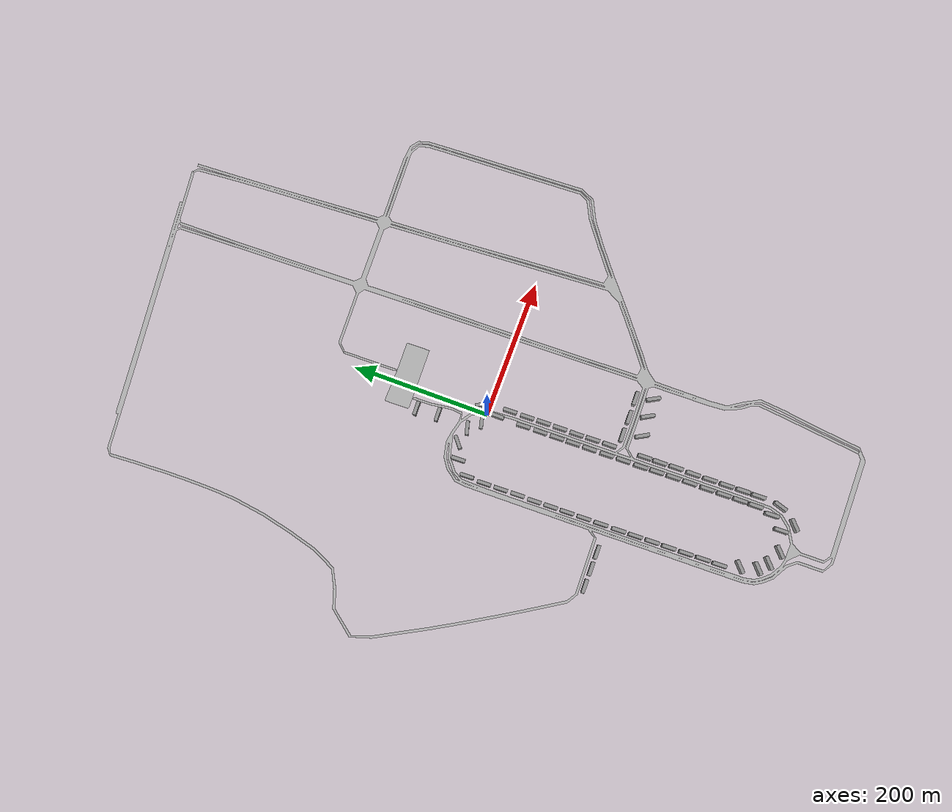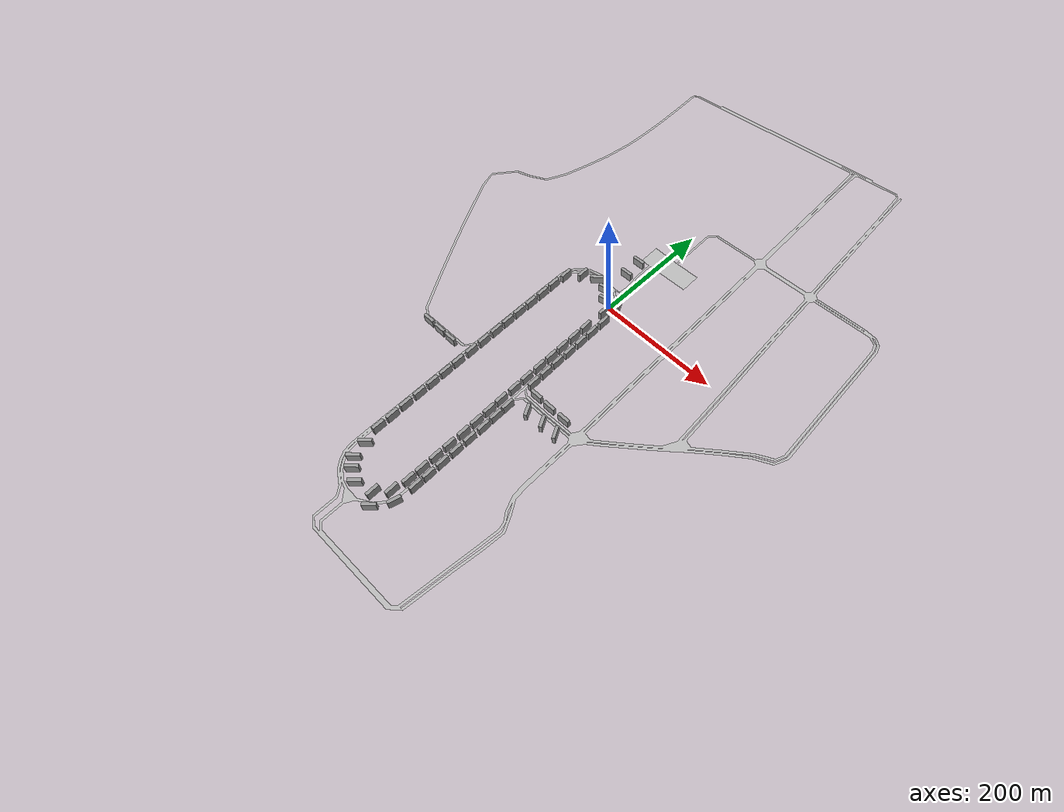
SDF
<sdf version='1.6'>
  <!-- This world file imports darpa.rndf file file sample into a world with some mock buildings made of static boxes. -->
  <world name='darpa_boxes'>
    <model name='road'>
      <pose frame=''>0.0 0.0 0.0 0 -0 0</pose>
      <link name='road_link'>
        <inertial>
          <mass>1</mass>
          <inertia>
            <ixx>0.166667</ixx>
            <ixy>0</ixy>
            <ixz>0</ixz>
            <iyy>0.166667</iyy>
            <iyz>0</iyz>
            <izz>0.166667</izz>
          </inertia>
        </inertial>
        <visual name='road_visual'>
          <geometry>
            <mesh>
              <uri>meshes/darpa.obj</uri>
            </mesh>
          </geometry>
        </visual>
        <self_collide>0</self_collide>
        <kinematic>0</kinematic>
      </link>
    </model>
    <model name='box_71'>
      <link name='link'>
        <inertial>
          <mass>1</mass>
          <inertia>
            <ixx>0.166667</ixx>
            <ixy>0</ixy>
            <ixz>0</ixz>
            <iyy>0.166667</iyy>
            <iyz>0</iyz>
            <izz>0.166667</izz>
          </inertia>
          <pose frame=''>0 0 7.5 0 -0 0</pose>
        </inertial>
        <self_collide>0</self_collide>
        <enable_wind>0</enable_wind>
        <kinematic>0</kinematic>
        <pose frame=''>0 0 0 0 -0 0</pose>
        <gravity>1</gravity>
        <visual name='visual'>
          <geometry>
            <box>
              <size>5 20 15</size>
            </box>
          </geometry>
          <material>
            <script>
              <name>Gazebo/Grey</name>
              <uri>file://media/materials/scripts/gazebo.material</uri>
            </script>
            <shader type='vertex'>
              <normal_map>_default_</normal_map>
            </shader>
            <ambient>0.3 0.3 0.3 1</ambient>
            <diffuse>0.7 0.7 0.7 1</diffuse>
            <specular>0.01 0.01 0.01 1</specular>
            <emissive>0 0 0 1</emissive>
          </material>
          <pose frame=''>0 0 7.5 0 -0 0</pose>
          <transparency>0</transparency>
          <cast_shadows>1</cast_shadows>
        </visual>
        <collision name='collision'>
          <laser_retro>0</laser_retro>
          <max_contacts>10</max_contacts>
          <pose frame=''>0 0 7.5 0 -0 0</pose>
          <geometry>
            <box>
              <size>5 20 15</size>
            </box>
          </geometry>
          <surface>
            <friction>
              <ode>
                <mu>1</mu>
                <mu2>1</mu2>
                <fdir1>0 0 0</fdir1>
                <slip1>0</slip1>
                <slip2>0</slip2>
              </ode>
              <torsional>
                <coefficient>1</coefficient>
                <patch_radius>0</patch_radius>
                <surface_radius>0</surface_radius>
                <use_patch_radius>1</use_patch_radius>
                <ode>
                  <slip>0</slip>
                </ode>
              </torsional>
            </friction>
            <bounce>
              <restitution_coefficient>0</restitution_coefficient>
              <threshold>1e+06</threshold>
            </bounce>
            <contact>
              <collide_without_contact>0</collide_without_contact>
              <collide_without_contact_bitmask>1</collide_without_contact_bitmask>
              <collide_bitmask>1</collide_bitmask>
              <ode>
                <soft_cfm>0</soft_cfm>
                <soft_erp>0.2</soft_erp>
                <kp>1e+13</kp>
                <kd>1</kd>
                <max_vel>0.01</max_vel>
                <min_depth>0</min_depth>
              </ode>
              <bullet>
                <split_impulse>1</split_impulse>
                <split_impulse_penetration_threshold>-0.01</split_impulse_penetration_threshold>
                <soft_cfm>0</soft_cfm>
                <soft_erp>0.2</soft_erp>
                <kp>1e+13</kp>
                <kd>1</kd>
              </bullet>
            </contact>
          </surface>
        </collision>
      </link>
      <static>1</static>
      <allow_auto_disable>1</allow_auto_disable>
      <pose frame=''>2.62805 -13.5402 0.5 0 -0 0</pose>
    </model>
    <model name='box_70'>
      <link name='link'>
        <inertial>
          <mass>1</mass>
          <inertia>
            <ixx>0.166667</ixx>
            <ixy>0</ixy>
            <ixz>0</ixz>
            <iyy>0.166667</iyy>
            <iyz>0</iyz>
            <izz>0.166667</izz>
          </inertia>
          <pose frame=''>0 0 7.5 0 -0 0</pose>
        </inertial>
        <self_collide>0</self_collide>
        <enable_wind>0</enable_wind>
        <kinematic>0</kinematic>
        <pose frame=''>0 0 0 0 -0 0</pose>
        <gravity>1</gravity>
        <visual name='visual'>
          <geometry>
            <box>
              <size>5 20 15</size>
            </box>
          </geometry>
          <material>
            <script>
              <name>Gazebo/Grey</name>
              <uri>file://media/materials/scripts/gazebo.material</uri>
            </script>
            <shader type='vertex'>
              <normal_map>_default_</normal_map>
            </shader>
            <ambient>0.3 0.3 0.3 1</ambient>
            <diffuse>0.7 0.7 0.7 1</diffuse>
            <specular>0.01 0.01 0.01 1</specular>
            <emissive>0 0 0 1</emissive>
          </material>
          <pose frame=''>0 0 7.5 0 -0 0</pose>
          <transparency>0</transparency>
          <cast_shadows>1</cast_shadows>
        </visual>
        <collision name='collision'>
          <laser_retro>0</laser_retro>
          <max_contacts>10</max_contacts>
          <pose frame=''>0 0 7.5 0 -0 0</pose>
          <geometry>
            <box>
              <size>5 20 15</size>
            </box>
          </geometry>
          <surface>
            <friction>
              <ode>
                <mu>1</mu>
                <mu2>1</mu2>
                <fdir1>0 0 0</fdir1>
                <slip1>0</slip1>
                <slip2>0</slip2>
              </ode>
              <torsional>
                <coefficient>1</coefficient>
                <patch_radius>0</patch_radius>
                <surface_radius>0</surface_radius>
                <use_patch_radius>1</use_patch_radius>
                <ode>
                  <slip>0</slip>
                </ode>
              </torsional>
            </friction>
            <bounce>
              <restitution_coefficient>0</restitution_coefficient>
              <threshold>1e+06</threshold>
            </bounce>
            <contact>
              <collide_without_contact>0</collide_without_contact>
              <collide_without_contact_bitmask>1</collide_without_contact_bitmask>
              <collide_bitmask>1</collide_bitmask>
              <ode>
                <soft_cfm>0</soft_cfm>
                <soft_erp>0.2</soft_erp>
                <kp>1e+13</kp>
                <kd>1</kd>
                <max_vel>0.01</max_vel>
                <min_depth>0</min_depth>
              </ode>
              <bullet>
                <split_impulse>1</split_impulse>
                <split_impulse_penetration_threshold>-0.01</split_impulse_penetration_threshold>
                <soft_cfm>0</soft_cfm>
                <soft_erp>0.2</soft_erp>
                <kp>1e+13</kp>
                <kd>1</kd>
              </bullet>
            </contact>
          </surface>
        </collision>
      </link>
      <static>1</static>
      <allow_auto_disable>1</allow_auto_disable>
      <pose frame=''>2.2166 -52.9463 -0.049551 0.005043 -0.00022 0.043493</pose>
    </model>
    <model name='box_69'>
      <link name='link'>
        <inertial>
          <mass>1</mass>
          <inertia>
            <ixx>0.166667</ixx>
            <ixy>0</ixy>
            <ixz>0</ixz>
            <iyy>0.166667</iyy>
            <iyz>0</iyz>
            <izz>0.166667</izz>
          </inertia>
          <pose frame=''>0 0 7.5 0 -0 0</pose>
        </inertial>
        <self_collide>0</self_collide>
        <enable_wind>0</enable_wind>
        <kinematic>0</kinematic>
        <pose frame=''>0 0 0 0 -0 0</pose>
        <gravity>1</gravity>
        <visual name='visual'>
          <geometry>
            <box>
              <size>5 20 15</size>
            </box>
          </geometry>
          <material>
            <script>
              <name>Gazebo/Grey</name>
              <uri>file://media/materials/scripts/gazebo.material</uri>
            </script>
            <shader type='vertex'>
              <normal_map>_default_</normal_map>
            </shader>
            <ambient>0.3 0.3 0.3 1</ambient>
            <diffuse>0.7 0.7 0.7 1</diffuse>
            <specular>0.01 0.01 0.01 1</specular>
            <emissive>0 0 0 1</emissive>
          </material>
          <pose frame=''>0 0 7.5 0 -0 0</pose>
          <transparency>0</transparency>
          <cast_shadows>1</cast_shadows>
        </visual>
        <collision name='collision'>
          <laser_retro>0</laser_retro>
          <max_contacts>10</max_contacts>
          <pose frame=''>0 0 7.5 0 -0 0</pose>
          <geometry>
            <box>
              <size>5 20 15</size>
            </box>
          </geometry>
          <surface>
            <friction>
              <ode>
                <mu>1</mu>
                <mu2>1</mu2>
                <fdir1>0 0 0</fdir1>
                <slip1>0</slip1>
                <slip2>0</slip2>
              </ode>
              <torsional>
                <coefficient>1</coefficient>
                <patch_radius>0</patch_radius>
                <surface_radius>0</surface_radius>
                <use_patch_radius>1</use_patch_radius>
                <ode>
                  <slip>0</slip>
                </ode>
              </torsional>
            </friction>
            <bounce>
              <restitution_coefficient>0</restitution_coefficient>
              <threshold>1e+06</threshold>
            </bounce>
            <contact>
              <collide_without_contact>0</collide_without_contact>
              <collide_without_contact_bitmask>1</collide_without_contact_bitmask>
              <collide_bitmask>1</collide_bitmask>
              <ode>
                <soft_cfm>0</soft_cfm>
                <soft_erp>0.2</soft_erp>
                <kp>1e+13</kp>
                <kd>1</kd>
                <max_vel>0.01</max_vel>
                <min_depth>0</min_depth>
              </ode>
              <bullet>
                <split_impulse>1</split_impulse>
                <split_impulse_penetration_threshold>-0.01</split_impulse_penetration_threshold>
                <soft_cfm>0</soft_cfm>
                <soft_erp>0.2</soft_erp>
                <kp>1e+13</kp>
                <kd>1</kd>
              </bullet>
            </contact>
          </surface>
        </collision>
      </link>
      <static>1</static>
      <allow_auto_disable>1</allow_auto_disable>
      <pose frame=''>2.59574 -78.262 -0.049551 0.005047 -0.000114 0.022472</pose>
    </model>
    <model name='box_68'>
      <link name='link'>
        <inertial>
          <mass>1</mass>
          <inertia>
            <ixx>0.166667</ixx>
            <ixy>0</ixy>
            <ixz>0</ixz>
            <iyy>0.166667</iyy>
            <iyz>0</iyz>
            <izz>0.166667</izz>
          </inertia>
          <pose frame=''>0 0 7.5 0 -0 0</pose>
        </inertial>
        <self_collide>0</self_collide>
        <enable_wind>0</enable_wind>
        <kinematic>0</kinematic>
        <pose frame=''>0 0 0 0 -0 0</pose>
        <gravity>1</gravity>
        <visual name='visual'>
          <geometry>
            <box>
              <size>5 20 15</size>
            </box>
          </geometry>
          <material>
            <script>
              <name>Gazebo/Grey</name>
              <uri>file://media/materials/scripts/gazebo.material</uri>
            </script>
            <shader type='vertex'>
              <normal_map>_default_</normal_map>
            </shader>
            <ambient>0.3 0.3 0.3 1</ambient>
            <diffuse>0.7 0.7 0.7 1</diffuse>
            <specular>0.01 0.01 0.01 1</specular>
            <emissive>0 0 0 1</emissive>
          </material>
          <pose frame=''>0 0 7.5 0 -0 0</pose>
          <transparency>0</transparency>
          <cast_shadows>1</cast_shadows>
        </visual>
        <collision name='collision'>
          <laser_retro>0</laser_retro>
          <max_contacts>10</max_contacts>
          <pose frame=''>0 0 7.5 0 -0 0</pose>
          <geometry>
            <box>
              <size>5 20 15</size>
            </box>
          </geometry>
          <surface>
            <friction>
              <ode>
                <mu>1</mu>
                <mu2>1</mu2>
                <fdir1>0 0 0</fdir1>
                <slip1>0</slip1>
                <slip2>0</slip2>
              </ode>
              <torsional>
                <coefficient>1</coefficient>
                <patch_radius>0</patch_radius>
                <surface_radius>0</surface_radius>
                <use_patch_radius>1</use_patch_radius>
                <ode>
                  <slip>0</slip>
                </ode>
              </torsional>
            </friction>
            <bounce>
              <restitution_coefficient>0</restitution_coefficient>
              <threshold>1e+06</threshold>
            </bounce>
            <contact>
              <collide_without_contact>0</collide_without_contact>
              <collide_without_contact_bitmask>1</collide_without_contact_bitmask>
              <collide_bitmask>1</collide_bitmask>
              <ode>
                <soft_cfm>0</soft_cfm>
                <soft_erp>0.2</soft_erp>
                <kp>1e+13</kp>
                <kd>1</kd>
                <max_vel>0.01</max_vel>
                <min_depth>0</min_depth>
              </ode>
              <bullet>
                <split_impulse>1</split_impulse>
                <split_impulse_penetration_threshold>-0.01</split_impulse_penetration_threshold>
                <soft_cfm>0</soft_cfm>
                <soft_erp>0.2</soft_erp>
                <kp>1e+13</kp>
                <kd>1</kd>
              </bullet>
            </contact>
          </surface>
        </collision>
      </link>
      <static>1</static>
      <allow_auto_disable>1</allow_auto_disable>
      <pose frame=''>2.95301 -102.999 -0.049551 0.005047 -0.000114 0.022472</pose>
    </model>
    <model name='box_1'>
      <link name='link'>
        <inertial>
          <mass>1</mass>
          <inertia>
            <ixx>0.166667</ixx>
            <ixy>0</ixy>
            <ixz>0</ixz>
            <iyy>0.166667</iyy>
            <iyz>0</iyz>
            <izz>0.166667</izz>
          </inertia>
          <pose frame=''>0 0 7.5 0 -0 0</pose>
        </inertial>
        <self_collide>0</self_collide>
        <enable_wind>0</enable_wind>
        <kinematic>0</kinematic>
        <pose frame=''>0 0 0 0 -0 0</pose>
        <gravity>1</gravity>
        <visual name='visual'>
          <geometry>
            <box>
              <size>5 20 15</size>
            </box>
          </geometry>
          <material>
            <script>
              <name>Gazebo/Grey</name>
              <uri>file://media/materials/scripts/gazebo.material</uri>
            </script>
            <shader type='vertex'>
              <normal_map>_default_</normal_map>
            </shader>
            <ambient>0.3 0.3 0.3 1</ambient>
            <diffuse>0.7 0.7 0.7 1</diffuse>
            <specular>0.01 0.01 0.01 1</specular>
            <emissive>0 0 0 1</emissive>
          </material>
          <pose frame=''>0 0 7.5 0 -0 0</pose>
          <transparency>0</transparency>
          <cast_shadows>1</cast_shadows>
        </visual>
        <collision name='collision'>
          <laser_retro>0</laser_retro>
          <max_contacts>10</max_contacts>
          <pose frame=''>0 0 7.5 0 -0 0</pose>
          <geometry>
            <box>
              <size>5 20 15</size>
            </box>
          </geometry>
          <surface>
            <friction>
              <ode>
                <mu>1</mu>
                <mu2>1</mu2>
                <fdir1>0 0 0</fdir1>
                <slip1>0</slip1>
                <slip2>0</slip2>
              </ode>
              <torsional>
                <coefficient>1</coefficient>
                <patch_radius>0</patch_radius>
                <surface_radius>0</surface_radius>
                <use_patch_radius>1</use_patch_radius>
                <ode>
                  <slip>0</slip>
                </ode>
              </torsional>
            </friction>
            <bounce>
              <restitution_coefficient>0</restitution_coefficient>
              <threshold>1e+06</threshold>
            </bounce>
            <contact>
              <collide_without_contact>0</collide_without_contact>
              <collide_without_contact_bitmask>1</collide_without_contact_bitmask>
              <collide_bitmask>1</collide_bitmask>
              <ode>
                <soft_cfm>0</soft_cfm>
                <soft_erp>0.2</soft_erp>
                <kp>1e+13</kp>
                <kd>1</kd>
                <max_vel>0.01</max_vel>
                <min_depth>0</min_depth>
              </ode>
              <bullet>
                <split_impulse>1</split_impulse>
                <split_impulse_penetration_threshold>-0.01</split_impulse_penetration_threshold>
                <soft_cfm>0</soft_cfm>
                <soft_erp>0.2</soft_erp>
                <kp>1e+13</kp>
                <kd>1</kd>
              </bullet>
            </contact>
          </surface>
        </collision>
      </link>
      <static>1</static>
      <allow_auto_disable>1</allow_auto_disable>
      <pose frame=''>3.43621 -126.848 -0.049551 0.005047 -0.000114 0.022472</pose>
    </model>
    <model name='box_2'>
      <link name='link'>
        <inertial>
          <mass>1</mass>
          <inertia>
            <ixx>0.166667</ixx>
            <ixy>0</ixy>
            <ixz>0</ixz>
            <iyy>0.166667</iyy>
            <iyz>0</iyz>
            <izz>0.166667</izz>
          </inertia>
          <pose frame=''>0 0 7.5 0 -0 0</pose>
        </inertial>
        <self_collide>0</self_collide>
        <enable_wind>0</enable_wind>
        <kinematic>0</kinematic>
        <pose frame=''>0 0 0 0 -0 0</pose>
        <gravity>1</gravity>
        <visual name='visual'>
          <geometry>
            <box>
              <size>5 20 15</size>
            </box>
          </geometry>
          <material>
            <script>
              <name>Gazebo/Grey</name>
              <uri>file://media/materials/scripts/gazebo.material</uri>
            </script>
            <shader type='vertex'>
              <normal_map>_default_</normal_map>
            </shader>
            <ambient>0.3 0.3 0.3 1</ambient>
            <diffuse>0.7 0.7 0.7 1</diffuse>
            <specular>0.01 0.01 0.01 1</specular>
            <emissive>0 0 0 1</emissive>
          </material>
          <pose frame=''>0 0 7.5 0 -0 0</pose>
          <transparency>0</transparency>
          <cast_shadows>1</cast_shadows>
        </visual>
        <collision name='collision'>
          <laser_retro>0</laser_retro>
          <max_contacts>10</max_contacts>
          <pose frame=''>0 0 7.5 0 -0 0</pose>
          <geometry>
            <box>
              <size>5 20 15</size>
            </box>
          </geometry>
          <surface>
            <friction>
              <ode>
                <mu>1</mu>
                <mu2>1</mu2>
                <fdir1>0 0 0</fdir1>
                <slip1>0</slip1>
                <slip2>0</slip2>
              </ode>
              <torsional>
                <coefficient>1</coefficient>
                <patch_radius>0</patch_radius>
                <surface_radius>0</surface_radius>
                <use_patch_radius>1</use_patch_radius>
                <ode>
                  <slip>0</slip>
                </ode>
              </torsional>
            </friction>
            <bounce>
              <restitution_coefficient>0</restitution_coefficient>
              <threshold>1e+06</threshold>
            </bounce>
            <contact>
              <collide_without_contact>0</collide_without_contact>
              <collide_without_contact_bitmask>1</collide_without_contact_bitmask>
              <collide_bitmask>1</collide_bitmask>
              <ode>
                <soft_cfm>0</soft_cfm>
                <soft_erp>0.2</soft_erp>
                <kp>1e+13</kp>
                <kd>1</kd>
                <max_vel>0.01</max_vel>
                <min_depth>0</min_depth>
              </ode>
              <bullet>
                <split_impulse>1</split_impulse>
                <split_impulse_penetration_threshold>-0.01</split_impulse_penetration_threshold>
                <soft_cfm>0</soft_cfm>
                <soft_erp>0.2</soft_erp>
                <kp>1e+13</kp>
                <kd>1</kd>
              </bullet>
            </contact>
          </surface>
        </collision>
      </link>
      <static>1</static>
      <allow_auto_disable>1</allow_auto_disable>
      <pose frame=''>3.68929 -151.222 -0.049551 0.005047 -0.000114 0.022472</pose>
    </model>
    <model name='box_3'>
      <link name='link'>
        <inertial>
          <mass>1</mass>
          <inertia>
            <ixx>0.166667</ixx>
            <ixy>0</ixy>
            <ixz>0</ixz>
            <iyy>0.166667</iyy>
            <iyz>0</iyz>
            <izz>0.166667</izz>
          </inertia>
          <pose frame=''>0 0 7.5 0 -0 0</pose>
        </inertial>
        <self_collide>0</self_collide>
        <enable_wind>0</enable_wind>
        <kinematic>0</kinematic>
        <pose frame=''>0 0 0 0 -0 0</pose>
        <gravity>1</gravity>
        <visual name='visual'>
          <geometry>
            <box>
              <size>5 20 15</size>
            </box>
          </geometry>
          <material>
            <script>
              <name>Gazebo/Grey</name>
              <uri>file://media/materials/scripts/gazebo.material</uri>
            </script>
            <shader type='vertex'>
              <normal_map>_default_</normal_map>
            </shader>
            <ambient>0.3 0.3 0.3 1</ambient>
            <diffuse>0.7 0.7 0.7 1</diffuse>
            <specular>0.01 0.01 0.01 1</specular>
            <emissive>0 0 0 1</emissive>
          </material>
          <pose frame=''>0 0 7.5 0 -0 0</pose>
          <transparency>0</transparency>
          <cast_shadows>1</cast_shadows>
        </visual>
        <collision name='collision'>
          <laser_retro>0</laser_retro>
          <max_contacts>10</max_contacts>
          <pose frame=''>0 0 7.5 0 -0 0</pose>
          <geometry>
            <box>
              <size>5 20 15</size>
            </box>
          </geometry>
          <surface>
            <friction>
              <ode>
                <mu>1</mu>
                <mu2>1</mu2>
                <fdir1>0 0 0</fdir1>
                <slip1>0</slip1>
                <slip2>0</slip2>
              </ode>
              <torsional>
                <coefficient>1</coefficient>
                <patch_radius>0</patch_radius>
                <surface_radius>0</surface_radius>
                <use_patch_radius>1</use_patch_radius>
                <ode>
                  <slip>0</slip>
                </ode>
              </torsional>
            </friction>
            <bounce>
              <restitution_coefficient>0</restitution_coefficient>
              <threshold>1e+06</threshold>
            </bounce>
            <contact>
              <collide_without_contact>0</collide_without_contact>
              <collide_without_contact_bitmask>1</collide_without_contact_bitmask>
              <collide_bitmask>1</collide_bitmask>
              <ode>
                <soft_cfm>0</soft_cfm>
                <soft_erp>0.2</soft_erp>
                <kp>1e+13</kp>
                <kd>1</kd>
                <max_vel>0.01</max_vel>
                <min_depth>0</min_depth>
              </ode>
              <bullet>
                <split_impulse>1</split_impulse>
                <split_impulse_penetration_threshold>-0.01</split_impulse_penetration_threshold>
                <soft_cfm>0</soft_cfm>
                <soft_erp>0.2</soft_erp>
                <kp>1e+13</kp>
                <kd>1</kd>
              </bullet>
            </contact>
          </surface>
        </collision>
      </link>
      <static>1</static>
      <allow_auto_disable>1</allow_auto_disable>
      <pose frame=''>4.1621 -176.965 -0.049551 0.005047 -0.000114 0.022472</pose>
    </model>
    <model name='box_4'>
      <link name='link'>
        <inertial>
          <mass>1</mass>
          <inertia>
            <ixx>0.166667</ixx>
            <ixy>0</ixy>
            <ixz>0</ixz>
            <iyy>0.166667</iyy>
            <iyz>0</iyz>
            <izz>0.166667</izz>
          </inertia>
          <pose frame=''>0 0 7.5 0 -0 0</pose>
        </inertial>
        <self_collide>0</self_collide>
        <enable_wind>0</enable_wind>
        <kinematic>0</kinematic>
        <pose frame=''>0 0 0 0 -0 0</pose>
        <gravity>1</gravity>
        <visual name='visual'>
          <geometry>
            <box>
              <size>5 20 15</size>
            </box>
          </geometry>
          <material>
            <script>
              <name>Gazebo/Grey</name>
              <uri>file://media/materials/scripts/gazebo.material</uri>
            </script>
            <shader type='vertex'>
              <normal_map>_default_</normal_map>
            </shader>
            <ambient>0.3 0.3 0.3 1</ambient>
            <diffuse>0.7 0.7 0.7 1</diffuse>
            <specular>0.01 0.01 0.01 1</specular>
            <emissive>0 0 0 1</emissive>
          </material>
          <pose frame=''>0 0 7.5 0 -0 0</pose>
          <transparency>0</transparency>
          <cast_shadows>1</cast_shadows>
        </visual>
        <collision name='collision'>
          <laser_retro>0</laser_retro>
          <max_contacts>10</max_contacts>
          <pose frame=''>0 0 7.5 0 -0 0</pose>
          <geometry>
            <box>
              <size>5 20 15</size>
            </box>
          </geometry>
          <surface>
            <friction>
              <ode>
                <mu>1</mu>
                <mu2>1</mu2>
                <fdir1>0 0 0</fdir1>
                <slip1>0</slip1>
                <slip2>0</slip2>
              </ode>
              <torsional>
                <coefficient>1</coefficient>
                <patch_radius>0</patch_radius>
                <surface_radius>0</surface_radius>
                <use_patch_radius>1</use_patch_radius>
                <ode>
                  <slip>0</slip>
                </ode>
              </torsional>
            </friction>
            <bounce>
              <restitution_coefficient>0</restitution_coefficient>
              <threshold>1e+06</threshold>
            </bounce>
            <contact>
              <collide_without_contact>0</collide_without_contact>
              <collide_without_contact_bitmask>1</collide_without_contact_bitmask>
              <collide_bitmask>1</collide_bitmask>
              <ode>
                <soft_cfm>0</soft_cfm>
                <soft_erp>0.2</soft_erp>
                <kp>1e+13</kp>
                <kd>1</kd>
                <max_vel>0.01</max_vel>
                <min_depth>0</min_depth>
              </ode>
              <bullet>
                <split_impulse>1</split_impulse>
                <split_impulse_penetration_threshold>-0.01</split_impulse_penetration_threshold>
                <soft_cfm>0</soft_cfm>
                <soft_erp>0.2</soft_erp>
                <kp>1e+13</kp>
                <kd>1</kd>
              </bullet>
            </contact>
          </surface>
        </collision>
      </link>
      <static>1</static>
      <allow_auto_disable>1</allow_auto_disable>
      <pose frame=''>4.69386 -201.317 -0.049551 0.005047 -0.000114 0.022472</pose>
    </model>
    <model name='box_5'>
      <link name='link'>
        <inertial>
          <mass>1</mass>
          <inertia>
            <ixx>0.166667</ixx>
            <ixy>0</ixy>
            <ixz>0</ixz>
            <iyy>0.166667</iyy>
            <iyz>0</iyz>
            <izz>0.166667</izz>
          </inertia>
          <pose frame=''>0 0 7.5 0 -0 0</pose>
        </inertial>
        <self_collide>0</self_collide>
        <enable_wind>0</enable_wind>
        <kinematic>0</kinematic>
        <pose frame=''>0 0 0 0 -0 0</pose>
        <gravity>1</gravity>
        <visual name='visual'>
          <geometry>
            <box>
              <size>5 20 15</size>
            </box>
          </geometry>
          <material>
            <script>
              <name>Gazebo/Grey</name>
              <uri>file://media/materials/scripts/gazebo.material</uri>
            </script>
            <shader type='vertex'>
              <normal_map>_default_</normal_map>
            </shader>
            <ambient>0.3 0.3 0.3 1</ambient>
            <diffuse>0.7 0.7 0.7 1</diffuse>
            <specular>0.01 0.01 0.01 1</specular>
            <emissive>0 0 0 1</emissive>
          </material>
          <pose frame=''>0 0 7.5 0 -0 0</pose>
          <transparency>0</transparency>
          <cast_shadows>1</cast_shadows>
        </visual>
        <collision name='collision'>
          <laser_retro>0</laser_retro>
          <max_contacts>10</max_contacts>
          <pose frame=''>0 0 7.5 0 -0 0</pose>
          <geometry>
            <box>
              <size>5 20 15</size>
            </box>
          </geometry>
          <surface>
            <friction>
              <ode>
                <mu>1</mu>
                <mu2>1</mu2>
                <fdir1>0 0 0</fdir1>
                <slip1>0</slip1>
                <slip2>0</slip2>
              </ode>
              <torsional>
                <coefficient>1</coefficient>
                <patch_radius>0</patch_radius>
                <surface_radius>0</surface_radius>
                <use_patch_radius>1</use_patch_radius>
                <ode>
                  <slip>0</slip>
                </ode>
              </torsional>
            </friction>
            <bounce>
              <restitution_coefficient>0</restitution_coefficient>
              <threshold>1e+06</threshold>
            </bounce>
            <contact>
              <collide_without_contact>0</collide_without_contact>
              <collide_without_contact_bitmask>1</collide_without_contact_bitmask>
              <collide_bitmask>1</collide_bitmask>
              <ode>
                <soft_cfm>0</soft_cfm>
                <soft_erp>0.2</soft_erp>
                <kp>1e+13</kp>
                <kd>1</kd>
                <max_vel>0.01</max_vel>
                <min_depth>0</min_depth>
              </ode>
              <bullet>
                <split_impulse>1</split_impulse>
                <split_impulse_penetration_threshold>-0.01</split_impulse_penetration_threshold>
                <soft_cfm>0</soft_cfm>
                <soft_erp>0.2</soft_erp>
                <kp>1e+13</kp>
                <kd>1</kd>
              </bullet>
            </contact>
          </surface>
        </collision>
      </link>
      <static>1</static>
      <allow_auto_disable>1</allow_auto_disable>
      <pose frame=''>4.85871 -226.99 -0.049551 0.005047 -0.000114 0.022472</pose>
    </model>
    <model name='box_6'>
      <link name='link'>
        <inertial>
          <mass>1</mass>
          <inertia>
            <ixx>0.166667</ixx>
            <ixy>0</ixy>
            <ixz>0</ixz>
            <iyy>0.166667</iyy>
            <iyz>0</iyz>
            <izz>0.166667</izz>
          </inertia>
          <pose frame=''>0 0 7.5 0 -0 0</pose>
        </inertial>
        <self_collide>0</self_collide>
        <enable_wind>0</enable_wind>
        <kinematic>0</kinematic>
        <pose frame=''>0 0 0 0 -0 0</pose>
        <gravity>1</gravity>
        <visual name='visual'>
          <geometry>
            <box>
              <size>5 20 15</size>
            </box>
          </geometry>
          <material>
            <script>
              <name>Gazebo/Grey</name>
              <uri>file://media/materials/scripts/gazebo.material</uri>
            </script>
            <shader type='vertex'>
              <normal_map>_default_</normal_map>
            </shader>
            <ambient>0.3 0.3 0.3 1</ambient>
            <diffuse>0.7 0.7 0.7 1</diffuse>
            <specular>0.01 0.01 0.01 1</specular>
            <emissive>0 0 0 1</emissive>
          </material>
          <pose frame=''>0 0 7.5 0 -0 0</pose>
          <transparency>0</transparency>
          <cast_shadows>1</cast_shadows>
        </visual>
        <collision name='collision'>
          <laser_retro>0</laser_retro>
          <max_contacts>10</max_contacts>
          <pose frame=''>0 0 7.5 0 -0 0</pose>
          <geometry>
            <box>
              <size>5 20 15</size>
            </box>
          </geometry>
          <surface>
            <friction>
              <ode>
                <mu>1</mu>
                <mu2>1</mu2>
                <fdir1>0 0 0</fdir1>
                <slip1>0</slip1>
                <slip2>0</slip2>
              </ode>
              <torsional>
                <coefficient>1</coefficient>
                <patch_radius>0</patch_radius>
                <surface_radius>0</surface_radius>
                <use_patch_radius>1</use_patch_radius>
                <ode>
                  <slip>0</slip>
                </ode>
              </torsional>
            </friction>
            <bounce>
              <restitution_coefficient>0</restitution_coefficient>
              <threshold>1e+06</threshold>
            </bounce>
            <contact>
              <collide_without_contact>0</collide_without_contact>
              <collide_without_contact_bitmask>1</collide_without_contact_bitmask>
              <collide_bitmask>1</collide_bitmask>
              <ode>
                <soft_cfm>0</soft_cfm>
                <soft_erp>0.2</soft_erp>
                <kp>1e+13</kp>
                <kd>1</kd>
                <max_vel>0.01</max_vel>
                <min_depth>0</min_depth>
              </ode>
              <bullet>
                <split_impulse>1</split_impulse>
                <split_impulse_penetration_threshold>-0.01</split_impulse_penetration_threshold>
                <soft_cfm>0</soft_cfm>
                <soft_erp>0.2</soft_erp>
                <kp>1e+13</kp>
                <kd>1</kd>
              </bullet>
            </contact>
          </surface>
        </collision>
      </link>
      <static>1</static>
      <allow_auto_disable>1</allow_auto_disable>
      <pose frame=''>5.67981 -250.633 -0.049551 0.005047 -0.000114 0.022472</pose>
    </model>
    <model name='box_7'>
      <link name='link'>
        <inertial>
          <mass>1</mass>
          <inertia>
            <ixx>0.166667</ixx>
            <ixy>0</ixy>
            <ixz>0</ixz>
            <iyy>0.166667</iyy>
            <iyz>0</iyz>
            <izz>0.166667</izz>
          </inertia>
          <pose frame=''>0 0 7.5 0 -0 0</pose>
        </inertial>
        <self_collide>0</self_collide>
        <enable_wind>0</enable_wind>
        <kinematic>0</kinematic>
        <pose frame=''>0 0 0 0 -0 0</pose>
        <gravity>1</gravity>
        <visual name='visual'>
          <geometry>
            <box>
              <size>5 20 15</size>
            </box>
          </geometry>
          <material>
            <script>
              <name>Gazebo/Grey</name>
              <uri>file://media/materials/scripts/gazebo.material</uri>
            </script>
            <shader type='vertex'>
              <normal_map>_default_</normal_map>
            </shader>
            <ambient>0.3 0.3 0.3 1</ambient>
            <diffuse>0.7 0.7 0.7 1</diffuse>
            <specular>0.01 0.01 0.01 1</specular>
            <emissive>0 0 0 1</emissive>
          </material>
          <pose frame=''>0 0 7.5 0 -0 0</pose>
          <transparency>0</transparency>
          <cast_shadows>1</cast_shadows>
        </visual>
        <collision name='collision'>
          <laser_retro>0</laser_retro>
          <max_contacts>10</max_contacts>
          <pose frame=''>0 0 7.5 0 -0 0</pose>
          <geometry>
            <box>
              <size>5 20 15</size>
            </box>
          </geometry>
          <surface>
            <friction>
              <ode>
                <mu>1</mu>
                <mu2>1</mu2>
                <fdir1>0 0 0</fdir1>
                <slip1>0</slip1>
                <slip2>0</slip2>
              </ode>
              <torsional>
                <coefficient>1</coefficient>
                <patch_radius>0</patch_radius>
                <surface_radius>0</surface_radius>
                <use_patch_radius>1</use_patch_radius>
                <ode>
                  <slip>0</slip>
                </ode>
              </torsional>
            </friction>
            <bounce>
              <restitution_coefficient>0</restitution_coefficient>
              <threshold>1e+06</threshold>
            </bounce>
            <contact>
              <collide_without_contact>0</collide_without_contact>
              <collide_without_contact_bitmask>1</collide_without_contact_bitmask>
              <collide_bitmask>1</collide_bitmask>
              <ode>
                <soft_cfm>0</soft_cfm>
                <soft_erp>0.2</soft_erp>
                <kp>1e+13</kp>
                <kd>1</kd>
                <max_vel>0.01</max_vel>
                <min_depth>0</min_depth>
              </ode>
              <bullet>
                <split_impulse>1</split_impulse>
                <split_impulse_penetration_threshold>-0.01</split_impulse_penetration_threshold>
                <soft_cfm>0</soft_cfm>
                <soft_erp>0.2</soft_erp>
                <kp>1e+13</kp>
                <kd>1</kd>
              </bullet>
            </contact>
          </surface>
        </collision>
      </link>
      <static>1</static>
      <allow_auto_disable>1</allow_auto_disable>
      <pose frame=''>6.45947 -274.93 -0.049551 0.005047 -0.000114 0.022472</pose>
    </model>
    <model name='box_8'>
      <link name='link'>
        <inertial>
          <mass>1</mass>
          <inertia>
            <ixx>0.166667</ixx>
            <ixy>0</ixy>
            <ixz>0</ixz>
            <iyy>0.166667</iyy>
            <iyz>0</iyz>
            <izz>0.166667</izz>
          </inertia>
          <pose frame=''>0 0 7.5 0 -0 0</pose>
        </inertial>
        <self_collide>0</self_collide>
        <enable_wind>0</enable_wind>
        <kinematic>0</kinematic>
        <pose frame=''>0 0 0 0 -0 0</pose>
        <gravity>1</gravity>
        <visual name='visual'>
          <geometry>
            <box>
              <size>5 20 15</size>
            </box>
          </geometry>
          <material>
            <script>
              <name>Gazebo/Grey</name>
              <uri>file://media/materials/scripts/gazebo.material</uri>
            </script>
            <shader type='vertex'>
              <normal_map>_default_</normal_map>
            </shader>
            <ambient>0.3 0.3 0.3 1</ambient>
            <diffuse>0.7 0.7 0.7 1</diffuse>
            <specular>0.01 0.01 0.01 1</specular>
            <emissive>0 0 0 1</emissive>
          </material>
          <pose frame=''>0 0 7.5 0 -0 0</pose>
          <transparency>0</transparency>
          <cast_shadows>1</cast_shadows>
        </visual>
        <collision name='collision'>
          <laser_retro>0</laser_retro>
          <max_contacts>10</max_contacts>
          <pose frame=''>0 0 7.5 0 -0 0</pose>
          <geometry>
            <box>
              <size>5 20 15</size>
            </box>
          </geometry>
          <surface>
            <friction>
              <ode>
                <mu>1</mu>
                <mu2>1</mu2>
                <fdir1>0 0 0</fdir1>
                <slip1>0</slip1>
                <slip2>0</slip2>
              </ode>
              <torsional>
                <coefficient>1</coefficient>
                <patch_radius>0</patch_radius>
                <surface_radius>0</surface_radius>
                <use_patch_radius>1</use_patch_radius>
                <ode>
                  <slip>0</slip>
                </ode>
              </torsional>
            </friction>
            <bounce>
              <restitution_coefficient>0</restitution_coefficient>
              <threshold>1e+06</threshold>
            </bounce>
            <contact>
              <collide_without_contact>0</collide_without_contact>
              <collide_without_contact_bitmask>1</collide_without_contact_bitmask>
              <collide_bitmask>1</collide_bitmask>
              <ode>
                <soft_cfm>0</soft_cfm>
                <soft_erp>0.2</soft_erp>
                <kp>1e+13</kp>
                <kd>1</kd>
                <max_vel>0.01</max_vel>
                <min_depth>0</min_depth>
              </ode>
              <bullet>
                <split_impulse>1</split_impulse>
                <split_impulse_penetration_threshold>-0.01</split_impulse_penetration_threshold>
                <soft_cfm>0</soft_cfm>
                <soft_erp>0.2</soft_erp>
                <kp>1e+13</kp>
                <kd>1</kd>
              </bullet>
            </contact>
          </surface>
        </collision>
      </link>
      <static>1</static>
      <allow_auto_disable>1</allow_auto_disable>
      <pose frame=''>6.96106 -299.323 -0.049551 0.005047 -0.000114 0.022472</pose>
    </model>
    <model name='box_9'>
      <link name='link'>
        <inertial>
          <mass>1</mass>
          <inertia>
            <ixx>0.166667</ixx>
            <ixy>0</ixy>
            <ixz>0</ixz>
            <iyy>0.166667</iyy>
            <iyz>0</iyz>
            <izz>0.166667</izz>
          </inertia>
          <pose frame=''>0 0 7.5 0 -0 0</pose>
        </inertial>
        <self_collide>0</self_collide>
        <enable_wind>0</enable_wind>
        <kinematic>0</kinematic>
        <pose frame=''>0 0 0 0 -0 0</pose>
        <gravity>1</gravity>
        <visual name='visual'>
          <geometry>
            <box>
              <size>5 20 15</size>
            </box>
          </geometry>
          <material>
            <script>
              <name>Gazebo/Grey</name>
              <uri>file://media/materials/scripts/gazebo.material</uri>
            </script>
            <shader type='vertex'>
              <normal_map>_default_</normal_map>
            </shader>
            <ambient>0.3 0.3 0.3 1</ambient>
            <diffuse>0.7 0.7 0.7 1</diffuse>
            <specular>0.01 0.01 0.01 1</specular>
            <emissive>0 0 0 1</emissive>
          </material>
          <pose frame=''>0 0 7.5 0 -0 0</pose>
          <transparency>0</transparency>
          <cast_shadows>1</cast_shadows>
        </visual>
        <collision name='collision'>
          <laser_retro>0</laser_retro>
          <max_contacts>10</max_contacts>
          <pose frame=''>0 0 7.5 0 -0 0</pose>
          <geometry>
            <box>
              <size>5 20 15</size>
            </box>
          </geometry>
          <surface>
            <friction>
              <ode>
                <mu>1</mu>
                <mu2>1</mu2>
                <fdir1>0 0 0</fdir1>
                <slip1>0</slip1>
                <slip2>0</slip2>
              </ode>
              <torsional>
                <coefficient>1</coefficient>
                <patch_radius>0</patch_radius>
                <surface_radius>0</surface_radius>
                <use_patch_radius>1</use_patch_radius>
                <ode>
                  <slip>0</slip>
                </ode>
              </torsional>
            </friction>
            <bounce>
              <restitution_coefficient>0</restitution_coefficient>
              <threshold>1e+06</threshold>
            </bounce>
            <contact>
              <collide_without_contact>0</collide_without_contact>
              <collide_without_contact_bitmask>1</collide_without_contact_bitmask>
              <collide_bitmask>1</collide_bitmask>
              <ode>
                <soft_cfm>0</soft_cfm>
                <soft_erp>0.2</soft_erp>
                <kp>1e+13</kp>
                <kd>1</kd>
                <max_vel>0.01</max_vel>
                <min_depth>0</min_depth>
              </ode>
              <bullet>
                <split_impulse>1</split_impulse>
                <split_impulse_penetration_threshold>-0.01</split_impulse_penetration_threshold>
                <soft_cfm>0</soft_cfm>
                <soft_erp>0.2</soft_erp>
                <kp>1e+13</kp>
                <kd>1</kd>
              </bullet>
            </contact>
          </surface>
        </collision>
      </link>
      <static>1</static>
      <allow_auto_disable>1</allow_auto_disable>
      <pose frame=''>7.18976 -324.823 -0.049551 0.005047 -0.000114 0.022472</pose>
    </model>
    <model name='box_10'>
      <link name='link'>
        <inertial>
          <mass>1</mass>
          <inertia>
            <ixx>0.166667</ixx>
            <ixy>0</ixy>
            <ixz>0</ixz>
            <iyy>0.166667</iyy>
            <iyz>0</iyz>
            <izz>0.166667</izz>
          </inertia>
          <pose frame=''>0 0 7.5 0 -0 0</pose>
        </inertial>
        <self_collide>0</self_collide>
        <enable_wind>0</enable_wind>
        <kinematic>0</kinematic>
        <pose frame=''>0 0 0 0 -0 0</pose>
        <gravity>1</gravity>
        <visual name='visual'>
          <geometry>
            <box>
              <size>5 20 15</size>
            </box>
          </geometry>
          <material>
            <script>
              <name>Gazebo/Grey</name>
              <uri>file://media/materials/scripts/gazebo.material</uri>
            </script>
            <shader type='vertex'>
              <normal_map>_default_</normal_map>
            </shader>
            <ambient>0.3 0.3 0.3 1</ambient>
            <diffuse>0.7 0.7 0.7 1</diffuse>
            <specular>0.01 0.01 0.01 1</specular>
            <emissive>0 0 0 1</emissive>
          </material>
          <pose frame=''>0 0 7.5 0 -0 0</pose>
          <transparency>0</transparency>
          <cast_shadows>1</cast_shadows>
        </visual>
        <collision name='collision'>
          <laser_retro>0</laser_retro>
          <max_contacts>10</max_contacts>
          <pose frame=''>0 0 7.5 0 -0 0</pose>
          <geometry>
            <box>
              <size>5 20 15</size>
            </box>
          </geometry>
          <surface>
            <friction>
              <ode>
                <mu>1</mu>
                <mu2>1</mu2>
                <fdir1>0 0 0</fdir1>
                <slip1>0</slip1>
                <slip2>0</slip2>
              </ode>
              <torsional>
                <coefficient>1</coefficient>
                <patch_radius>0</patch_radius>
                <surface_radius>0</surface_radius>
                <use_patch_radius>1</use_patch_radius>
                <ode>
                  <slip>0</slip>
                </ode>
              </torsional>
            </friction>
            <bounce>
              <restitution_coefficient>0</restitution_coefficient>
              <threshold>1e+06</threshold>
            </bounce>
            <contact>
              <collide_without_contact>0</collide_without_contact>
              <collide_without_contact_bitmask>1</collide_without_contact_bitmask>
              <collide_bitmask>1</collide_bitmask>
              <ode>
                <soft_cfm>0</soft_cfm>
                <soft_erp>0.2</soft_erp>
                <kp>1e+13</kp>
                <kd>1</kd>
                <max_vel>0.01</max_vel>
                <min_depth>0</min_depth>
              </ode>
              <bullet>
                <split_impulse>1</split_impulse>
                <split_impulse_penetration_threshold>-0.01</split_impulse_penetration_threshold>
                <soft_cfm>0</soft_cfm>
                <soft_erp>0.2</soft_erp>
                <kp>1e+13</kp>
                <kd>1</kd>
              </bullet>
            </contact>
          </surface>
        </collision>
      </link>
      <static>1</static>
      <allow_auto_disable>1</allow_auto_disable>
      <pose frame=''>7.48707 -349.113 -0.049551 0.005047 -0.000114 0.022472</pose>
    </model>
    <model name='box_11'>
      <link name='link'>
        <inertial>
          <mass>1</mass>
          <inertia>
            <ixx>0.166667</ixx>
            <ixy>0</ixy>
            <ixz>0</ixz>
            <iyy>0.166667</iyy>
            <iyz>0</iyz>
            <izz>0.166667</izz>
          </inertia>
          <pose frame=''>0 0 7.5 0 -0 0</pose>
        </inertial>
        <self_collide>0</self_collide>
        <enable_wind>0</enable_wind>
        <kinematic>0</kinematic>
        <pose frame=''>0 0 0 0 -0 0</pose>
        <gravity>1</gravity>
        <visual name='visual'>
          <geometry>
            <box>
              <size>5 20 15</size>
            </box>
          </geometry>
          <material>
            <script>
              <name>Gazebo/Grey</name>
              <uri>file://media/materials/scripts/gazebo.material</uri>
            </script>
            <shader type='vertex'>
              <normal_map>_default_</normal_map>
            </shader>
            <ambient>0.3 0.3 0.3 1</ambient>
            <diffuse>0.7 0.7 0.7 1</diffuse>
            <specular>0.01 0.01 0.01 1</specular>
            <emissive>0 0 0 1</emissive>
          </material>
          <pose frame=''>0 0 7.5 0 -0 0</pose>
          <transparency>0</transparency>
          <cast_shadows>1</cast_shadows>
        </visual>
        <collision name='collision'>
          <laser_retro>0</laser_retro>
          <max_contacts>10</max_contacts>
          <pose frame=''>0 0 7.5 0 -0 0</pose>
          <geometry>
            <box>
              <size>5 20 15</size>
            </box>
          </geometry>
          <surface>
            <friction>
              <ode>
                <mu>1</mu>
                <mu2>1</mu2>
                <fdir1>0 0 0</fdir1>
                <slip1>0</slip1>
                <slip2>0</slip2>
              </ode>
              <torsional>
                <coefficient>1</coefficient>
                <patch_radius>0</patch_radius>
                <surface_radius>0</surface_radius>
                <use_patch_radius>1</use_patch_radius>
                <ode>
                  <slip>0</slip>
                </ode>
              </torsional>
            </friction>
            <bounce>
              <restitution_coefficient>0</restitution_coefficient>
              <threshold>1e+06</threshold>
            </bounce>
            <contact>
              <collide_without_contact>0</collide_without_contact>
              <collide_without_contact_bitmask>1</collide_without_contact_bitmask>
              <collide_bitmask>1</collide_bitmask>
              <ode>
                <soft_cfm>0</soft_cfm>
                <soft_erp>0.2</soft_erp>
                <kp>1e+13</kp>
                <kd>1</kd>
                <max_vel>0.01</max_vel>
                <min_depth>0</min_depth>
              </ode>
              <bullet>
                <split_impulse>1</split_impulse>
                <split_impulse_penetration_threshold>-0.01</split_impulse_penetration_threshold>
                <soft_cfm>0</soft_cfm>
                <soft_erp>0.2</soft_erp>
                <kp>1e+13</kp>
                <kd>1</kd>
              </bullet>
            </contact>
          </surface>
        </collision>
      </link>
      <static>1</static>
      <allow_auto_disable>1</allow_auto_disable>
      <pose frame=''>7.93072 -373.289 -0.049551 0.005047 -0.000114 0.022472</pose>
    </model>
    <model name='box_12'>
      <link name='link'>
        <inertial>
          <mass>1</mass>
          <inertia>
            <ixx>0.166667</ixx>
            <ixy>0</ixy>
            <ixz>0</ixz>
            <iyy>0.166667</iyy>
            <iyz>0</iyz>
            <izz>0.166667</izz>
          </inertia>
          <pose frame=''>0 0 7.5 0 -0 0</pose>
        </inertial>
        <self_collide>0</self_collide>
        <enable_wind>0</enable_wind>
        <kinematic>0</kinematic>
        <pose frame=''>0 0 0 0 -0 0</pose>
        <gravity>1</gravity>
        <visual name='visual'>
          <geometry>
            <box>
              <size>5 20 15</size>
            </box>
          </geometry>
          <material>
            <script>
              <name>Gazebo/Grey</name>
              <uri>file://media/materials/scripts/gazebo.material</uri>
            </script>
            <shader type='vertex'>
              <normal_map>_default_</normal_map>
            </shader>
            <ambient>0.3 0.3 0.3 1</ambient>
            <diffuse>0.7 0.7 0.7 1</diffuse>
            <specular>0.01 0.01 0.01 1</specular>
            <emissive>0 0 0 1</emissive>
          </material>
          <pose frame=''>0 0 7.5 0 -0 0</pose>
          <transparency>0</transparency>
          <cast_shadows>1</cast_shadows>
        </visual>
        <collision name='collision'>
          <laser_retro>0</laser_retro>
          <max_contacts>10</max_contacts>
          <pose frame=''>0 0 7.5 0 -0 0</pose>
          <geometry>
            <box>
              <size>5 20 15</size>
            </box>
          </geometry>
          <surface>
            <friction>
              <ode>
                <mu>1</mu>
                <mu2>1</mu2>
                <fdir1>0 0 0</fdir1>
                <slip1>0</slip1>
                <slip2>0</slip2>
              </ode>
              <torsional>
                <coefficient>1</coefficient>
                <patch_radius>0</patch_radius>
                <surface_radius>0</surface_radius>
                <use_patch_radius>1</use_patch_radius>
                <ode>
                  <slip>0</slip>
                </ode>
              </torsional>
            </friction>
            <bounce>
              <restitution_coefficient>0</restitution_coefficient>
              <threshold>1e+06</threshold>
            </bounce>
            <contact>
              <collide_without_contact>0</collide_without_contact>
              <collide_without_contact_bitmask>1</collide_without_contact_bitmask>
              <collide_bitmask>1</collide_bitmask>
              <ode>
                <soft_cfm>0</soft_cfm>
                <soft_erp>0.2</soft_erp>
                <kp>1e+13</kp>
                <kd>1</kd>
                <max_vel>0.01</max_vel>
                <min_depth>0</min_depth>
              </ode>
              <bullet>
                <split_impulse>1</split_impulse>
                <split_impulse_penetration_threshold>-0.01</split_impulse_penetration_threshold>
                <soft_cfm>0</soft_cfm>
                <soft_erp>0.2</soft_erp>
                <kp>1e+13</kp>
                <kd>1</kd>
              </bullet>
            </contact>
          </surface>
        </collision>
      </link>
      <static>1</static>
      <allow_auto_disable>1</allow_auto_disable>
      <pose frame=''>8.01915 -396.284 -0.049551 0.005047 -0.000114 0.022472</pose>
    </model>
    <model name='box_13'>
      <link name='link'>
        <inertial>
          <mass>1</mass>
          <inertia>
            <ixx>0.166667</ixx>
            <ixy>0</ixy>
            <ixz>0</ixz>
            <iyy>0.166667</iyy>
            <iyz>0</iyz>
            <izz>0.166667</izz>
          </inertia>
          <pose frame=''>0 0 7.5 0 -0 0</pose>
        </inertial>
        <self_collide>0</self_collide>
        <enable_wind>0</enable_wind>
        <kinematic>0</kinematic>
        <pose frame=''>0 0 0 0 -0 0</pose>
        <gravity>1</gravity>
        <visual name='visual'>
          <geometry>
            <box>
              <size>5 20 15</size>
            </box>
          </geometry>
          <material>
            <script>
              <name>Gazebo/Grey</name>
              <uri>file://media/materials/scripts/gazebo.material</uri>
            </script>
            <shader type='vertex'>
              <normal_map>_default_</normal_map>
            </shader>
            <ambient>0.3 0.3 0.3 1</ambient>
            <diffuse>0.7 0.7 0.7 1</diffuse>
            <specular>0.01 0.01 0.01 1</specular>
            <emissive>0 0 0 1</emissive>
          </material>
          <pose frame=''>0 0 7.5 0 -0 0</pose>
          <transparency>0</transparency>
          <cast_shadows>1</cast_shadows>
        </visual>
        <collision name='collision'>
          <laser_retro>0</laser_retro>
          <max_contacts>10</max_contacts>
          <pose frame=''>0 0 7.5 0 -0 0</pose>
          <geometry>
            <box>
              <size>5 20 15</size>
            </box>
          </geometry>
          <surface>
            <friction>
              <ode>
                <mu>1</mu>
                <mu2>1</mu2>
                <fdir1>0 0 0</fdir1>
                <slip1>0</slip1>
                <slip2>0</slip2>
              </ode>
              <torsional>
                <coefficient>1</coefficient>
                <patch_radius>0</patch_radius>
                <surface_radius>0</surface_radius>
                <use_patch_radius>1</use_patch_radius>
                <ode>
                  <slip>0</slip>
                </ode>
              </torsional>
            </friction>
            <bounce>
              <restitution_coefficient>0</restitution_coefficient>
              <threshold>1e+06</threshold>
            </bounce>
            <contact>
              <collide_without_contact>0</collide_without_contact>
              <collide_without_contact_bitmask>1</collide_without_contact_bitmask>
              <collide_bitmask>1</collide_bitmask>
              <ode>
                <soft_cfm>0</soft_cfm>
                <soft_erp>0.2</soft_erp>
                <kp>1e+13</kp>
                <kd>1</kd>
                <max_vel>0.01</max_vel>
                <min_depth>0</min_depth>
              </ode>
              <bullet>
                <split_impulse>1</split_impulse>
                <split_impulse_penetration_threshold>-0.01</split_impulse_penetration_threshold>
                <soft_cfm>0</soft_cfm>
                <soft_erp>0.2</soft_erp>
                <kp>1e+13</kp>
                <kd>1</kd>
              </bullet>
            </contact>
          </surface>
        </collision>
      </link>
      <static>1</static>
      <allow_auto_disable>1</allow_auto_disable>
      <pose frame=''>22.0679 -395.71 -0.049551 0.005047 -0.000114 0.022472</pose>
    </model>
    <model name='box_14'>
      <link name='link'>
        <inertial>
          <mass>1</mass>
          <inertia>
            <ixx>0.166667</ixx>
            <ixy>0</ixy>
            <ixz>0</ixz>
            <iyy>0.166667</iyy>
            <iyz>0</iyz>
            <izz>0.166667</izz>
          </inertia>
          <pose frame=''>0 0 7.5 0 -0 0</pose>
        </inertial>
        <self_collide>0</self_collide>
        <enable_wind>0</enable_wind>
        <kinematic>0</kinematic>
        <pose frame=''>0 0 0 0 -0 0</pose>
        <gravity>1</gravity>
        <visual name='visual'>
          <geometry>
            <box>
              <size>5 20 15</size>
            </box>
          </geometry>
          <material>
            <script>
              <name>Gazebo/Grey</name>
              <uri>file://media/materials/scripts/gazebo.material</uri>
            </script>
            <shader type='vertex'>
              <normal_map>_default_</normal_map>
            </shader>
            <ambient>0.3 0.3 0.3 1</ambient>
            <diffuse>0.7 0.7 0.7 1</diffuse>
            <specular>0.01 0.01 0.01 1</specular>
            <emissive>0 0 0 1</emissive>
          </material>
          <pose frame=''>0 0 7.5 0 -0 0</pose>
          <transparency>0</transparency>
          <cast_shadows>1</cast_shadows>
        </visual>
        <collision name='collision'>
          <laser_retro>0</laser_retro>
          <max_contacts>10</max_contacts>
          <pose frame=''>0 0 7.5 0 -0 0</pose>
          <geometry>
            <box>
              <size>5 20 15</size>
            </box>
          </geometry>
          <surface>
            <friction>
              <ode>
                <mu>1</mu>
                <mu2>1</mu2>
                <fdir1>0 0 0</fdir1>
                <slip1>0</slip1>
                <slip2>0</slip2>
              </ode>
              <torsional>
                <coefficient>1</coefficient>
                <patch_radius>0</patch_radius>
                <surface_radius>0</surface_radius>
                <use_patch_radius>1</use_patch_radius>
                <ode>
                  <slip>0</slip>
                </ode>
              </torsional>
            </friction>
            <bounce>
              <restitution_coefficient>0</restitution_coefficient>
              <threshold>1e+06</threshold>
            </bounce>
            <contact>
              <collide_without_contact>0</collide_without_contact>
              <collide_without_contact_bitmask>1</collide_without_contact_bitmask>
              <collide_bitmask>1</collide_bitmask>
              <ode>
                <soft_cfm>0</soft_cfm>
                <soft_erp>0.2</soft_erp>
                <kp>1e+13</kp>
                <kd>1</kd>
                <max_vel>0.01</max_vel>
                <min_depth>0</min_depth>
              </ode>
              <bullet>
                <split_impulse>1</split_impulse>
                <split_impulse_penetration_threshold>-0.01</split_impulse_penetration_threshold>
                <soft_cfm>0</soft_cfm>
                <soft_erp>0.2</soft_erp>
                <kp>1e+13</kp>
                <kd>1</kd>
              </bullet>
            </contact>
          </surface>
        </collision>
      </link>
      <static>1</static>
      <allow_auto_disable>1</allow_auto_disable>
      <pose frame=''>22.0165 -373.029 -0.049551 0.005047 -0.000114 0.022472</pose>
    </model>
    <model name='box_15'>
      <link name='link'>
        <inertial>
          <mass>1</mass>
          <inertia>
            <ixx>0.166667</ixx>
            <ixy>0</ixy>
            <ixz>0</ixz>
            <iyy>0.166667</iyy>
            <iyz>0</iyz>
            <izz>0.166667</izz>
          </inertia>
          <pose frame=''>0 0 7.5 0 -0 0</pose>
        </inertial>
        <self_collide>0</self_collide>
        <enable_wind>0</enable_wind>
        <kinematic>0</kinematic>
        <pose frame=''>0 0 0 0 -0 0</pose>
        <gravity>1</gravity>
        <visual name='visual'>
          <geometry>
            <box>
              <size>5 20 15</size>
            </box>
          </geometry>
          <material>
            <script>
              <name>Gazebo/Grey</name>
              <uri>file://media/materials/scripts/gazebo.material</uri>
            </script>
            <shader type='vertex'>
              <normal_map>_default_</normal_map>
            </shader>
            <ambient>0.3 0.3 0.3 1</ambient>
            <diffuse>0.7 0.7 0.7 1</diffuse>
            <specular>0.01 0.01 0.01 1</specular>
            <emissive>0 0 0 1</emissive>
          </material>
          <pose frame=''>0 0 7.5 0 -0 0</pose>
          <transparency>0</transparency>
          <cast_shadows>1</cast_shadows>
        </visual>
        <collision name='collision'>
          <laser_retro>0</laser_retro>
          <max_contacts>10</max_contacts>
          <pose frame=''>0 0 7.5 0 -0 0</pose>
          <geometry>
            <box>
              <size>5 20 15</size>
            </box>
          </geometry>
          <surface>
            <friction>
              <ode>
                <mu>1</mu>
                <mu2>1</mu2>
                <fdir1>0 0 0</fdir1>
                <slip1>0</slip1>
                <slip2>0</slip2>
              </ode>
              <torsional>
                <coefficient>1</coefficient>
                <patch_radius>0</patch_radius>
                <surface_radius>0</surface_radius>
                <use_patch_radius>1</use_patch_radius>
                <ode>
                  <slip>0</slip>
                </ode>
              </torsional>
            </friction>
            <bounce>
              <restitution_coefficient>0</restitution_coefficient>
              <threshold>1e+06</threshold>
            </bounce>
            <contact>
              <collide_without_contact>0</collide_without_contact>
              <collide_without_contact_bitmask>1</collide_without_contact_bitmask>
              <collide_bitmask>1</collide_bitmask>
              <ode>
                <soft_cfm>0</soft_cfm>
                <soft_erp>0.2</soft_erp>
                <kp>1e+13</kp>
                <kd>1</kd>
                <max_vel>0.01</max_vel>
                <min_depth>0</min_depth>
              </ode>
              <bullet>
                <split_impulse>1</split_impulse>
                <split_impulse_penetration_threshold>-0.01</split_impulse_penetration_threshold>
                <soft_cfm>0</soft_cfm>
                <soft_erp>0.2</soft_erp>
                <kp>1e+13</kp>
                <kd>1</kd>
              </bullet>
            </contact>
          </surface>
        </collision>
      </link>
      <static>1</static>
      <allow_auto_disable>1</allow_auto_disable>
      <pose frame=''>21.2901 -348.884 -0.049551 0.005047 -0.000114 0.022472</pose>
    </model>
    <model name='box_16'>
      <link name='link'>
        <inertial>
          <mass>1</mass>
          <inertia>
            <ixx>0.166667</ixx>
            <ixy>0</ixy>
            <ixz>0</ixz>
            <iyy>0.166667</iyy>
            <iyz>0</iyz>
            <izz>0.166667</izz>
          </inertia>
          <pose frame=''>0 0 7.5 0 -0 0</pose>
        </inertial>
        <self_collide>0</self_collide>
        <enable_wind>0</enable_wind>
        <kinematic>0</kinematic>
        <pose frame=''>0 0 0 0 -0 0</pose>
        <gravity>1</gravity>
        <visual name='visual'>
          <geometry>
            <box>
              <size>5 20 15</size>
            </box>
          </geometry>
          <material>
            <script>
              <name>Gazebo/Grey</name>
              <uri>file://media/materials/scripts/gazebo.material</uri>
            </script>
            <shader type='vertex'>
              <normal_map>_default_</normal_map>
            </shader>
            <ambient>0.3 0.3 0.3 1</ambient>
            <diffuse>0.7 0.7 0.7 1</diffuse>
            <specular>0.01 0.01 0.01 1</specular>
            <emissive>0 0 0 1</emissive>
          </material>
          <pose frame=''>0 0 7.5 0 -0 0</pose>
          <transparency>0</transparency>
          <cast_shadows>1</cast_shadows>
        </visual>
        <collision name='collision'>
          <laser_retro>0</laser_retro>
          <max_contacts>10</max_contacts>
          <pose frame=''>0 0 7.5 0 -0 0</pose>
          <geometry>
            <box>
              <size>5 20 15</size>
            </box>
          </geometry>
          <surface>
            <friction>
              <ode>
                <mu>1</mu>
                <mu2>1</mu2>
                <fdir1>0 0 0</fdir1>
                <slip1>0</slip1>
                <slip2>0</slip2>
              </ode>
              <torsional>
                <coefficient>1</coefficient>
                <patch_radius>0</patch_radius>
                <surface_radius>0</surface_radius>
                <use_patch_radius>1</use_patch_radius>
                <ode>
                  <slip>0</slip>
                </ode>
              </torsional>
            </friction>
            <bounce>
              <restitution_coefficient>0</restitution_coefficient>
              <threshold>1e+06</threshold>
            </bounce>
            <contact>
              <collide_without_contact>0</collide_without_contact>
              <collide_without_contact_bitmask>1</collide_without_contact_bitmask>
              <collide_bitmask>1</collide_bitmask>
              <ode>
                <soft_cfm>0</soft_cfm>
                <soft_erp>0.2</soft_erp>
                <kp>1e+13</kp>
                <kd>1</kd>
                <max_vel>0.01</max_vel>
                <min_depth>0</min_depth>
              </ode>
              <bullet>
                <split_impulse>1</split_impulse>
                <split_impulse_penetration_threshold>-0.01</split_impulse_penetration_threshold>
                <soft_cfm>0</soft_cfm>
                <soft_erp>0.2</soft_erp>
                <kp>1e+13</kp>
                <kd>1</kd>
              </bullet>
            </contact>
          </surface>
        </collision>
      </link>
      <static>1</static>
      <allow_auto_disable>1</allow_auto_disable>
      <pose frame=''>20.8426 -324.277 -0.049551 0.005047 -0.000114 0.022472</pose>
    </model>
    <model name='box_17'>
      <link name='link'>
        <inertial>
          <mass>1</mass>
          <inertia>
            <ixx>0.166667</ixx>
            <ixy>0</ixy>
            <ixz>0</ixz>
            <iyy>0.166667</iyy>
            <iyz>0</iyz>
            <izz>0.166667</izz>
          </inertia>
          <pose frame=''>0 0 7.5 0 -0 0</pose>
        </inertial>
        <self_collide>0</self_collide>
        <enable_wind>0</enable_wind>
        <kinematic>0</kinematic>
        <pose frame=''>0 0 0 0 -0 0</pose>
        <gravity>1</gravity>
        <visual name='visual'>
          <geometry>
            <box>
              <size>5 20 15</size>
            </box>
          </geometry>
          <material>
            <script>
              <name>Gazebo/Grey</name>
              <uri>file://media/materials/scripts/gazebo.material</uri>
            </script>
            <shader type='vertex'>
              <normal_map>_default_</normal_map>
            </shader>
            <ambient>0.3 0.3 0.3 1</ambient>
            <diffuse>0.7 0.7 0.7 1</diffuse>
            <specular>0.01 0.01 0.01 1</specular>
            <emissive>0 0 0 1</emissive>
          </material>
          <pose frame=''>0 0 7.5 0 -0 0</pose>
          <transparency>0</transparency>
          <cast_shadows>1</cast_shadows>
        </visual>
        <collision name='collision'>
          <laser_retro>0</laser_retro>
          <max_contacts>10</max_contacts>
          <pose frame=''>0 0 7.5 0 -0 0</pose>
          <geometry>
            <box>
              <size>5 20 15</size>
            </box>
          </geometry>
          <surface>
            <friction>
              <ode>
                <mu>1</mu>
                <mu2>1</mu2>
                <fdir1>0 0 0</fdir1>
                <slip1>0</slip1>
                <slip2>0</slip2>
              </ode>
              <torsional>
                <coefficient>1</coefficient>
                <patch_radius>0</patch_radius>
                <surface_radius>0</surface_radius>
                <use_patch_radius>1</use_patch_radius>
                <ode>
                  <slip>0</slip>
                </ode>
              </torsional>
            </friction>
            <bounce>
              <restitution_coefficient>0</restitution_coefficient>
              <threshold>1e+06</threshold>
            </bounce>
            <contact>
              <collide_without_contact>0</collide_without_contact>
              <collide_without_contact_bitmask>1</collide_without_contact_bitmask>
              <collide_bitmask>1</collide_bitmask>
              <ode>
                <soft_cfm>0</soft_cfm>
                <soft_erp>0.2</soft_erp>
                <kp>1e+13</kp>
                <kd>1</kd>
                <max_vel>0.01</max_vel>
                <min_depth>0</min_depth>
              </ode>
              <bullet>
                <split_impulse>1</split_impulse>
                <split_impulse_penetration_threshold>-0.01</split_impulse_penetration_threshold>
                <soft_cfm>0</soft_cfm>
                <soft_erp>0.2</soft_erp>
                <kp>1e+13</kp>
                <kd>1</kd>
              </bullet>
            </contact>
          </surface>
        </collision>
      </link>
      <static>1</static>
      <allow_auto_disable>1</allow_auto_disable>
      <pose frame=''>20.3309 -299.386 -0.049551 0.005047 -0.000114 0.022472</pose>
    </model>
    <model name='box_18'>
      <link name='link'>
        <inertial>
          <mass>1</mass>
          <inertia>
            <ixx>0.166667</ixx>
            <ixy>0</ixy>
            <ixz>0</ixz>
            <iyy>0.166667</iyy>
            <iyz>0</iyz>
            <izz>0.166667</izz>
          </inertia>
          <pose frame=''>0 0 7.5 0 -0 0</pose>
        </inertial>
        <self_collide>0</self_collide>
        <enable_wind>0</enable_wind>
        <kinematic>0</kinematic>
        <pose frame=''>0 0 0 0 -0 0</pose>
        <gravity>1</gravity>
        <visual name='visual'>
          <geometry>
            <box>
              <size>5 20 15</size>
            </box>
          </geometry>
          <material>
            <script>
              <name>Gazebo/Grey</name>
              <uri>file://media/materials/scripts/gazebo.material</uri>
            </script>
            <shader type='vertex'>
              <normal_map>_default_</normal_map>
            </shader>
            <ambient>0.3 0.3 0.3 1</ambient>
            <diffuse>0.7 0.7 0.7 1</diffuse>
            <specular>0.01 0.01 0.01 1</specular>
            <emissive>0 0 0 1</emissive>
          </material>
          <pose frame=''>0 0 7.5 0 -0 0</pose>
          <transparency>0</transparency>
          <cast_shadows>1</cast_shadows>
        </visual>
        <collision name='collision'>
          <laser_retro>0</laser_retro>
          <max_contacts>10</max_contacts>
          <pose frame=''>0 0 7.5 0 -0 0</pose>
          <geometry>
            <box>
              <size>5 20 15</size>
            </box>
          </geometry>
          <surface>
            <friction>
              <ode>
                <mu>1</mu>
                <mu2>1</mu2>
                <fdir1>0 0 0</fdir1>
                <slip1>0</slip1>
                <slip2>0</slip2>
              </ode>
              <torsional>
                <coefficient>1</coefficient>
                <patch_radius>0</patch_radius>
                <surface_radius>0</surface_radius>
                <use_patch_radius>1</use_patch_radius>
                <ode>
                  <slip>0</slip>
                </ode>
              </torsional>
            </friction>
            <bounce>
              <restitution_coefficient>0</restitution_coefficient>
              <threshold>1e+06</threshold>
            </bounce>
            <contact>
              <collide_without_contact>0</collide_without_contact>
              <collide_without_contact_bitmask>1</collide_without_contact_bitmask>
              <collide_bitmask>1</collide_bitmask>
              <ode>
                <soft_cfm>0</soft_cfm>
                <soft_erp>0.2</soft_erp>
                <kp>1e+13</kp>
                <kd>1</kd>
                <max_vel>0.01</max_vel>
                <min_depth>0</min_depth>
              </ode>
              <bullet>
                <split_impulse>1</split_impulse>
                <split_impulse_penetration_threshold>-0.01</split_impulse_penetration_threshold>
                <soft_cfm>0</soft_cfm>
                <soft_erp>0.2</soft_erp>
                <kp>1e+13</kp>
                <kd>1</kd>
              </bullet>
            </contact>
          </surface>
        </collision>
      </link>
      <static>1</static>
      <allow_auto_disable>1</allow_auto_disable>
      <pose frame=''>20.4301 -274.151 -0.049551 0.005047 -0.000114 0.022472</pose>
    </model>
    <model name='box_19'>
      <link name='link'>
        <inertial>
          <mass>1</mass>
          <inertia>
            <ixx>0.166667</ixx>
            <ixy>0</ixy>
            <ixz>0</ixz>
            <iyy>0.166667</iyy>
            <iyz>0</iyz>
            <izz>0.166667</izz>
          </inertia>
          <pose frame=''>0 0 7.5 0 -0 0</pose>
        </inertial>
        <self_collide>0</self_collide>
        <enable_wind>0</enable_wind>
        <kinematic>0</kinematic>
        <pose frame=''>0 0 0 0 -0 0</pose>
        <gravity>1</gravity>
        <visual name='visual'>
          <geometry>
            <box>
              <size>5 20 15</size>
            </box>
          </geometry>
          <material>
            <script>
              <name>Gazebo/Grey</name>
              <uri>file://media/materials/scripts/gazebo.material</uri>
            </script>
            <shader type='vertex'>
              <normal_map>_default_</normal_map>
            </shader>
            <ambient>0.3 0.3 0.3 1</ambient>
            <diffuse>0.7 0.7 0.7 1</diffuse>
            <specular>0.01 0.01 0.01 1</specular>
            <emissive>0 0 0 1</emissive>
          </material>
          <pose frame=''>0 0 7.5 0 -0 0</pose>
          <transparency>0</transparency>
          <cast_shadows>1</cast_shadows>
        </visual>
        <collision name='collision'>
          <laser_retro>0</laser_retro>
          <max_contacts>10</max_contacts>
          <pose frame=''>0 0 7.5 0 -0 0</pose>
          <geometry>
            <box>
              <size>5 20 15</size>
            </box>
          </geometry>
          <surface>
            <friction>
              <ode>
                <mu>1</mu>
                <mu2>1</mu2>
                <fdir1>0 0 0</fdir1>
                <slip1>0</slip1>
                <slip2>0</slip2>
              </ode>
              <torsional>
                <coefficient>1</coefficient>
                <patch_radius>0</patch_radius>
                <surface_radius>0</surface_radius>
                <use_patch_radius>1</use_patch_radius>
                <ode>
                  <slip>0</slip>
                </ode>
              </torsional>
            </friction>
            <bounce>
              <restitution_coefficient>0</restitution_coefficient>
              <threshold>1e+06</threshold>
            </bounce>
            <contact>
              <collide_without_contact>0</collide_without_contact>
              <collide_without_contact_bitmask>1</collide_without_contact_bitmask>
              <collide_bitmask>1</collide_bitmask>
              <ode>
                <soft_cfm>0</soft_cfm>
                <soft_erp>0.2</soft_erp>
                <kp>1e+13</kp>
                <kd>1</kd>
                <max_vel>0.01</max_vel>
                <min_depth>0</min_depth>
              </ode>
              <bullet>
                <split_impulse>1</split_impulse>
                <split_impulse_penetration_threshold>-0.01</split_impulse_penetration_threshold>
                <soft_cfm>0</soft_cfm>
                <soft_erp>0.2</soft_erp>
                <kp>1e+13</kp>
                <kd>1</kd>
              </bullet>
            </contact>
          </surface>
        </collision>
      </link>
      <static>1</static>
      <allow_auto_disable>1</allow_auto_disable>
      <pose frame=''>19.6822 -250.445 -0.049551 0.005047 -0.000114 0.022472</pose>
    </model>
    <model name='box_20'>
      <link name='link'>
        <inertial>
          <mass>1</mass>
          <inertia>
            <ixx>0.166667</ixx>
            <ixy>0</ixy>
            <ixz>0</ixz>
            <iyy>0.166667</iyy>
            <iyz>0</iyz>
            <izz>0.166667</izz>
          </inertia>
          <pose frame=''>0 0 7.5 0 -0 0</pose>
        </inertial>
        <self_collide>0</self_collide>
        <enable_wind>0</enable_wind>
        <kinematic>0</kinematic>
        <pose frame=''>0 0 0 0 -0 0</pose>
        <gravity>1</gravity>
        <visual name='visual'>
          <geometry>
            <box>
              <size>5 20 15</size>
            </box>
          </geometry>
          <material>
            <script>
              <name>Gazebo/Grey</name>
              <uri>file://media/materials/scripts/gazebo.material</uri>
            </script>
            <shader type='vertex'>
              <normal_map>_default_</normal_map>
            </shader>
            <ambient>0.3 0.3 0.3 1</ambient>
            <diffuse>0.7 0.7 0.7 1</diffuse>
            <specular>0.01 0.01 0.01 1</specular>
            <emissive>0 0 0 1</emissive>
          </material>
          <pose frame=''>0 0 7.5 0 -0 0</pose>
          <transparency>0</transparency>
          <cast_shadows>1</cast_shadows>
        </visual>
        <collision name='collision'>
          <laser_retro>0</laser_retro>
          <max_contacts>10</max_contacts>
          <pose frame=''>0 0 7.5 0 -0 0</pose>
          <geometry>
            <box>
              <size>5 20 15</size>
            </box>
          </geometry>
          <surface>
            <friction>
              <ode>
                <mu>1</mu>
                <mu2>1</mu2>
                <fdir1>0 0 0</fdir1>
                <slip1>0</slip1>
                <slip2>0</slip2>
              </ode>
              <torsional>
                <coefficient>1</coefficient>
                <patch_radius>0</patch_radius>
                <surface_radius>0</surface_radius>
                <use_patch_radius>1</use_patch_radius>
                <ode>
                  <slip>0</slip>
                </ode>
              </torsional>
            </friction>
            <bounce>
              <restitution_coefficient>0</restitution_coefficient>
              <threshold>1e+06</threshold>
            </bounce>
            <contact>
              <collide_without_contact>0</collide_without_contact>
              <collide_without_contact_bitmask>1</collide_without_contact_bitmask>
              <collide_bitmask>1</collide_bitmask>
              <ode>
                <soft_cfm>0</soft_cfm>
                <soft_erp>0.2</soft_erp>
                <kp>1e+13</kp>
                <kd>1</kd>
                <max_vel>0.01</max_vel>
                <min_depth>0</min_depth>
              </ode>
              <bullet>
                <split_impulse>1</split_impulse>
                <split_impulse_penetration_threshold>-0.01</split_impulse_penetration_threshold>
                <soft_cfm>0</soft_cfm>
                <soft_erp>0.2</soft_erp>
                <kp>1e+13</kp>
                <kd>1</kd>
              </bullet>
            </contact>
          </surface>
        </collision>
      </link>
      <static>1</static>
      <allow_auto_disable>1</allow_auto_disable>
      <pose frame=''>19.2326 -227.915 -0.049551 0.005047 -0.000114 0.022472</pose>
    </model>
    <model name='box_21'>
      <link name='link'>
        <inertial>
          <mass>1</mass>
          <inertia>
            <ixx>0.166667</ixx>
            <ixy>0</ixy>
            <ixz>0</ixz>
            <iyy>0.166667</iyy>
            <iyz>0</iyz>
            <izz>0.166667</izz>
          </inertia>
          <pose frame=''>0 0 7.5 0 -0 0</pose>
        </inertial>
        <self_collide>0</self_collide>
        <enable_wind>0</enable_wind>
        <kinematic>0</kinematic>
        <pose frame=''>0 0 0 0 -0 0</pose>
        <gravity>1</gravity>
        <visual name='visual'>
          <geometry>
            <box>
              <size>5 20 15</size>
            </box>
          </geometry>
          <material>
            <script>
              <name>Gazebo/Grey</name>
              <uri>file://media/materials/scripts/gazebo.material</uri>
            </script>
            <shader type='vertex'>
              <normal_map>_default_</normal_map>
            </shader>
            <ambient>0.3 0.3 0.3 1</ambient>
            <diffuse>0.7 0.7 0.7 1</diffuse>
            <specular>0.01 0.01 0.01 1</specular>
            <emissive>0 0 0 1</emissive>
          </material>
          <pose frame=''>0 0 7.5 0 -0 0</pose>
          <transparency>0</transparency>
          <cast_shadows>1</cast_shadows>
        </visual>
        <collision name='collision'>
          <laser_retro>0</laser_retro>
          <max_contacts>10</max_contacts>
          <pose frame=''>0 0 7.5 0 -0 0</pose>
          <geometry>
            <box>
              <size>5 20 15</size>
            </box>
          </geometry>
          <surface>
            <friction>
              <ode>
                <mu>1</mu>
                <mu2>1</mu2>
                <fdir1>0 0 0</fdir1>
                <slip1>0</slip1>
                <slip2>0</slip2>
              </ode>
              <torsional>
                <coefficient>1</coefficient>
                <patch_radius>0</patch_radius>
                <surface_radius>0</surface_radius>
                <use_patch_radius>1</use_patch_radius>
                <ode>
                  <slip>0</slip>
                </ode>
              </torsional>
            </friction>
            <bounce>
              <restitution_coefficient>0</restitution_coefficient>
              <threshold>1e+06</threshold>
            </bounce>
            <contact>
              <collide_without_contact>0</collide_without_contact>
              <collide_without_contact_bitmask>1</collide_without_contact_bitmask>
              <collide_bitmask>1</collide_bitmask>
              <ode>
                <soft_cfm>0</soft_cfm>
                <soft_erp>0.2</soft_erp>
                <kp>1e+13</kp>
                <kd>1</kd>
                <max_vel>0.01</max_vel>
                <min_depth>0</min_depth>
              </ode>
              <bullet>
                <split_impulse>1</split_impulse>
                <split_impulse_penetration_threshold>-0.01</split_impulse_penetration_threshold>
                <soft_cfm>0</soft_cfm>
                <soft_erp>0.2</soft_erp>
                <kp>1e+13</kp>
                <kd>1</kd>
              </bullet>
            </contact>
          </surface>
        </collision>
      </link>
      <static>1</static>
      <allow_auto_disable>1</allow_auto_disable>
      <pose frame=''>18.4209 -175.838 -0.049551 0.005047 -0.000114 0.022472</pose>
    </model>
    <model name='box_22'>
      <link name='link'>
        <inertial>
          <mass>1</mass>
          <inertia>
            <ixx>0.166667</ixx>
            <ixy>0</ixy>
            <ixz>0</ixz>
            <iyy>0.166667</iyy>
            <iyz>0</iyz>
            <izz>0.166667</izz>
          </inertia>
          <pose frame=''>0 0 7.5 0 -0 0</pose>
        </inertial>
        <self_collide>0</self_collide>
        <enable_wind>0</enable_wind>
        <kinematic>0</kinematic>
        <pose frame=''>0 0 0 0 -0 0</pose>
        <gravity>1</gravity>
        <visual name='visual'>
          <geometry>
            <box>
              <size>5 20 15</size>
            </box>
          </geometry>
          <material>
            <script>
              <name>Gazebo/Grey</name>
              <uri>file://media/materials/scripts/gazebo.material</uri>
            </script>
            <shader type='vertex'>
              <normal_map>_default_</normal_map>
            </shader>
            <ambient>0.3 0.3 0.3 1</ambient>
            <diffuse>0.7 0.7 0.7 1</diffuse>
            <specular>0.01 0.01 0.01 1</specular>
            <emissive>0 0 0 1</emissive>
          </material>
          <pose frame=''>0 0 7.5 0 -0 0</pose>
          <transparency>0</transparency>
          <cast_shadows>1</cast_shadows>
        </visual>
        <collision name='collision'>
          <laser_retro>0</laser_retro>
          <max_contacts>10</max_contacts>
          <pose frame=''>0 0 7.5 0 -0 0</pose>
          <geometry>
            <box>
              <size>5 20 15</size>
            </box>
          </geometry>
          <surface>
            <friction>
              <ode>
                <mu>1</mu>
                <mu2>1</mu2>
                <fdir1>0 0 0</fdir1>
                <slip1>0</slip1>
                <slip2>0</slip2>
              </ode>
              <torsional>
                <coefficient>1</coefficient>
                <patch_radius>0</patch_radius>
                <surface_radius>0</surface_radius>
                <use_patch_radius>1</use_patch_radius>
                <ode>
                  <slip>0</slip>
                </ode>
              </torsional>
            </friction>
            <bounce>
              <restitution_coefficient>0</restitution_coefficient>
              <threshold>1e+06</threshold>
            </bounce>
            <contact>
              <collide_without_contact>0</collide_without_contact>
              <collide_without_contact_bitmask>1</collide_without_contact_bitmask>
              <collide_bitmask>1</collide_bitmask>
              <ode>
                <soft_cfm>0</soft_cfm>
                <soft_erp>0.2</soft_erp>
                <kp>1e+13</kp>
                <kd>1</kd>
                <max_vel>0.01</max_vel>
                <min_depth>0</min_depth>
              </ode>
              <bullet>
                <split_impulse>1</split_impulse>
                <split_impulse_penetration_threshold>-0.01</split_impulse_penetration_threshold>
                <soft_cfm>0</soft_cfm>
                <soft_erp>0.2</soft_erp>
                <kp>1e+13</kp>
                <kd>1</kd>
              </bullet>
            </contact>
          </surface>
        </collision>
      </link>
      <static>1</static>
      <allow_auto_disable>1</allow_auto_disable>
      <pose frame=''>17.8317 -151.144 -0.049551 0.005047 -0.000114 0.022472</pose>
    </model>
    <model name='box_23'>
      <link name='link'>
        <inertial>
          <mass>1</mass>
          <inertia>
            <ixx>0.166667</ixx>
            <ixy>0</ixy>
            <ixz>0</ixz>
            <iyy>0.166667</iyy>
            <iyz>0</iyz>
            <izz>0.166667</izz>
          </inertia>
          <pose frame=''>0 0 7.5 0 -0 0</pose>
        </inertial>
        <self_collide>0</self_collide>
        <enable_wind>0</enable_wind>
        <kinematic>0</kinematic>
        <pose frame=''>0 0 0 0 -0 0</pose>
        <gravity>1</gravity>
        <visual name='visual'>
          <geometry>
            <box>
              <size>5 20 15</size>
            </box>
          </geometry>
          <material>
            <script>
              <name>Gazebo/Grey</name>
              <uri>file://media/materials/scripts/gazebo.material</uri>
            </script>
            <shader type='vertex'>
              <normal_map>_default_</normal_map>
            </shader>
            <ambient>0.3 0.3 0.3 1</ambient>
            <diffuse>0.7 0.7 0.7 1</diffuse>
            <specular>0.01 0.01 0.01 1</specular>
            <emissive>0 0 0 1</emissive>
          </material>
          <pose frame=''>0 0 7.5 0 -0 0</pose>
          <transparency>0</transparency>
          <cast_shadows>1</cast_shadows>
        </visual>
        <collision name='collision'>
          <laser_retro>0</laser_retro>
          <max_contacts>10</max_contacts>
          <pose frame=''>0 0 7.5 0 -0 0</pose>
          <geometry>
            <box>
              <size>5 20 15</size>
            </box>
          </geometry>
          <surface>
            <friction>
              <ode>
                <mu>1</mu>
                <mu2>1</mu2>
                <fdir1>0 0 0</fdir1>
                <slip1>0</slip1>
                <slip2>0</slip2>
              </ode>
              <torsional>
                <coefficient>1</coefficient>
                <patch_radius>0</patch_radius>
                <surface_radius>0</surface_radius>
                <use_patch_radius>1</use_patch_radius>
                <ode>
                  <slip>0</slip>
                </ode>
              </torsional>
            </friction>
            <bounce>
              <restitution_coefficient>0</restitution_coefficient>
              <threshold>1e+06</threshold>
            </bounce>
            <contact>
              <collide_without_contact>0</collide_without_contact>
              <collide_without_contact_bitmask>1</collide_without_contact_bitmask>
              <collide_bitmask>1</collide_bitmask>
              <ode>
                <soft_cfm>0</soft_cfm>
                <soft_erp>0.2</soft_erp>
                <kp>1e+13</kp>
                <kd>1</kd>
                <max_vel>0.01</max_vel>
                <min_depth>0</min_depth>
              </ode>
              <bullet>
                <split_impulse>1</split_impulse>
                <split_impulse_penetration_threshold>-0.01</split_impulse_penetration_threshold>
                <soft_cfm>0</soft_cfm>
                <soft_erp>0.2</soft_erp>
                <kp>1e+13</kp>
                <kd>1</kd>
              </bullet>
            </contact>
          </surface>
        </collision>
      </link>
      <static>1</static>
      <allow_auto_disable>1</allow_auto_disable>
      <pose frame=''>17.0274 -127.223 -0.049551 0.005047 -0.000114 0.022472</pose>
    </model>
    <model name='box_24'>
      <link name='link'>
        <inertial>
          <mass>1</mass>
          <inertia>
            <ixx>0.166667</ixx>
            <ixy>0</ixy>
            <ixz>0</ixz>
            <iyy>0.166667</iyy>
            <iyz>0</iyz>
            <izz>0.166667</izz>
          </inertia>
          <pose frame=''>0 0 7.5 0 -0 0</pose>
        </inertial>
        <self_collide>0</self_collide>
        <enable_wind>0</enable_wind>
        <kinematic>0</kinematic>
        <pose frame=''>0 0 0 0 -0 0</pose>
        <gravity>1</gravity>
        <visual name='visual'>
          <geometry>
            <box>
              <size>5 20 15</size>
            </box>
          </geometry>
          <material>
            <script>
              <name>Gazebo/Grey</name>
              <uri>file://media/materials/scripts/gazebo.material</uri>
            </script>
            <shader type='vertex'>
              <normal_map>_default_</normal_map>
            </shader>
            <ambient>0.3 0.3 0.3 1</ambient>
            <diffuse>0.7 0.7 0.7 1</diffuse>
            <specular>0.01 0.01 0.01 1</specular>
            <emissive>0 0 0 1</emissive>
          </material>
          <pose frame=''>0 0 7.5 0 -0 0</pose>
          <transparency>0</transparency>
          <cast_shadows>1</cast_shadows>
        </visual>
        <collision name='collision'>
          <laser_retro>0</laser_retro>
          <max_contacts>10</max_contacts>
          <pose frame=''>0 0 7.5 0 -0 0</pose>
          <geometry>
            <box>
              <size>5 20 15</size>
            </box>
          </geometry>
          <surface>
            <friction>
              <ode>
                <mu>1</mu>
                <mu2>1</mu2>
                <fdir1>0 0 0</fdir1>
                <slip1>0</slip1>
                <slip2>0</slip2>
              </ode>
              <torsional>
                <coefficient>1</coefficient>
                <patch_radius>0</patch_radius>
                <surface_radius>0</surface_radius>
                <use_patch_radius>1</use_patch_radius>
                <ode>
                  <slip>0</slip>
                </ode>
              </torsional>
            </friction>
            <bounce>
              <restitution_coefficient>0</restitution_coefficient>
              <threshold>1e+06</threshold>
            </bounce>
            <contact>
              <collide_without_contact>0</collide_without_contact>
              <collide_without_contact_bitmask>1</collide_without_contact_bitmask>
              <collide_bitmask>1</collide_bitmask>
              <ode>
                <soft_cfm>0</soft_cfm>
                <soft_erp>0.2</soft_erp>
                <kp>1e+13</kp>
                <kd>1</kd>
                <max_vel>0.01</max_vel>
                <min_depth>0</min_depth>
              </ode>
              <bullet>
                <split_impulse>1</split_impulse>
                <split_impulse_penetration_threshold>-0.01</split_impulse_penetration_threshold>
                <soft_cfm>0</soft_cfm>
                <soft_erp>0.2</soft_erp>
                <kp>1e+13</kp>
                <kd>1</kd>
              </bullet>
            </contact>
          </surface>
        </collision>
      </link>
      <static>1</static>
      <allow_auto_disable>1</allow_auto_disable>
      <pose frame=''>16.8933 -102.381 -0.049551 0.005047 -0.000114 0.022472</pose>
    </model>
    <model name='box_25'>
      <link name='link'>
        <inertial>
          <mass>1</mass>
          <inertia>
            <ixx>0.166667</ixx>
            <ixy>0</ixy>
            <ixz>0</ixz>
            <iyy>0.166667</iyy>
            <iyz>0</iyz>
            <izz>0.166667</izz>
          </inertia>
          <pose frame=''>0 0 7.5 0 -0 0</pose>
        </inertial>
        <self_collide>0</self_collide>
        <enable_wind>0</enable_wind>
        <kinematic>0</kinematic>
        <pose frame=''>0 0 0 0 -0 0</pose>
        <gravity>1</gravity>
        <visual name='visual'>
          <geometry>
            <box>
              <size>5 20 15</size>
            </box>
          </geometry>
          <material>
            <script>
              <name>Gazebo/Grey</name>
              <uri>file://media/materials/scripts/gazebo.material</uri>
            </script>
            <shader type='vertex'>
              <normal_map>_default_</normal_map>
            </shader>
            <ambient>0.3 0.3 0.3 1</ambient>
            <diffuse>0.7 0.7 0.7 1</diffuse>
            <specular>0.01 0.01 0.01 1</specular>
            <emissive>0 0 0 1</emissive>
          </material>
          <pose frame=''>0 0 7.5 0 -0 0</pose>
          <transparency>0</transparency>
          <cast_shadows>1</cast_shadows>
        </visual>
        <collision name='collision'>
          <laser_retro>0</laser_retro>
          <max_contacts>10</max_contacts>
          <pose frame=''>0 0 7.5 0 -0 0</pose>
          <geometry>
            <box>
              <size>5 20 15</size>
            </box>
          </geometry>
          <surface>
            <friction>
              <ode>
                <mu>1</mu>
                <mu2>1</mu2>
                <fdir1>0 0 0</fdir1>
                <slip1>0</slip1>
                <slip2>0</slip2>
              </ode>
              <torsional>
                <coefficient>1</coefficient>
                <patch_radius>0</patch_radius>
                <surface_radius>0</surface_radius>
                <use_patch_radius>1</use_patch_radius>
                <ode>
                  <slip>0</slip>
                </ode>
              </torsional>
            </friction>
            <bounce>
              <restitution_coefficient>0</restitution_coefficient>
              <threshold>1e+06</threshold>
            </bounce>
            <contact>
              <collide_without_contact>0</collide_without_contact>
              <collide_without_contact_bitmask>1</collide_without_contact_bitmask>
              <collide_bitmask>1</collide_bitmask>
              <ode>
                <soft_cfm>0</soft_cfm>
                <soft_erp>0.2</soft_erp>
                <kp>1e+13</kp>
                <kd>1</kd>
                <max_vel>0.01</max_vel>
                <min_depth>0</min_depth>
              </ode>
              <bullet>
                <split_impulse>1</split_impulse>
                <split_impulse_penetration_threshold>-0.01</split_impulse_penetration_threshold>
                <soft_cfm>0</soft_cfm>
                <soft_erp>0.2</soft_erp>
                <kp>1e+13</kp>
                <kd>1</kd>
              </bullet>
            </contact>
          </surface>
        </collision>
      </link>
      <static>1</static>
      <allow_auto_disable>1</allow_auto_disable>
      <pose frame=''>16.538 -77.9247 -0.049551 0.005047 -0.000114 0.022472</pose>
    </model>
    <model name='box_26'>
      <link name='link'>
        <inertial>
          <mass>1</mass>
          <inertia>
            <ixx>0.166667</ixx>
            <ixy>0</ixy>
            <ixz>0</ixz>
            <iyy>0.166667</iyy>
            <iyz>0</iyz>
            <izz>0.166667</izz>
          </inertia>
          <pose frame=''>0 0 7.5 0 -0 0</pose>
        </inertial>
        <self_collide>0</self_collide>
        <enable_wind>0</enable_wind>
        <kinematic>0</kinematic>
        <pose frame=''>0 0 0 0 -0 0</pose>
        <gravity>1</gravity>
        <visual name='visual'>
          <geometry>
            <box>
              <size>5 20 15</size>
            </box>
          </geometry>
          <material>
            <script>
              <name>Gazebo/Grey</name>
              <uri>file://media/materials/scripts/gazebo.material</uri>
            </script>
            <shader type='vertex'>
              <normal_map>_default_</normal_map>
            </shader>
            <ambient>0.3 0.3 0.3 1</ambient>
            <diffuse>0.7 0.7 0.7 1</diffuse>
            <specular>0.01 0.01 0.01 1</specular>
            <emissive>0 0 0 1</emissive>
          </material>
          <pose frame=''>0 0 7.5 0 -0 0</pose>
          <transparency>0</transparency>
          <cast_shadows>1</cast_shadows>
        </visual>
        <collision name='collision'>
          <laser_retro>0</laser_retro>
          <max_contacts>10</max_contacts>
          <pose frame=''>0 0 7.5 0 -0 0</pose>
          <geometry>
            <box>
              <size>5 20 15</size>
            </box>
          </geometry>
          <surface>
            <friction>
              <ode>
                <mu>1</mu>
                <mu2>1</mu2>
                <fdir1>0 0 0</fdir1>
                <slip1>0</slip1>
                <slip2>0</slip2>
              </ode>
              <torsional>
                <coefficient>1</coefficient>
                <patch_radius>0</patch_radius>
                <surface_radius>0</surface_radius>
                <use_patch_radius>1</use_patch_radius>
                <ode>
                  <slip>0</slip>
                </ode>
              </torsional>
            </friction>
            <bounce>
              <restitution_coefficient>0</restitution_coefficient>
              <threshold>1e+06</threshold>
            </bounce>
            <contact>
              <collide_without_contact>0</collide_without_contact>
              <collide_without_contact_bitmask>1</collide_without_contact_bitmask>
              <collide_bitmask>1</collide_bitmask>
              <ode>
                <soft_cfm>0</soft_cfm>
                <soft_erp>0.2</soft_erp>
                <kp>1e+13</kp>
                <kd>1</kd>
                <max_vel>0.01</max_vel>
                <min_depth>0</min_depth>
              </ode>
              <bullet>
                <split_impulse>1</split_impulse>
                <split_impulse_penetration_threshold>-0.01</split_impulse_penetration_threshold>
                <soft_cfm>0</soft_cfm>
                <soft_erp>0.2</soft_erp>
                <kp>1e+13</kp>
                <kd>1</kd>
              </bullet>
            </contact>
          </surface>
        </collision>
      </link>
      <static>1</static>
      <allow_auto_disable>1</allow_auto_disable>
      <pose frame=''>16.0227 -53.7626 -0.049551 0.005047 -0.000114 0.022472</pose>
    </model>
    <model name='box_27'>
      <link name='link'>
        <inertial>
          <mass>1</mass>
          <inertia>
            <ixx>0.166667</ixx>
            <ixy>0</ixy>
            <ixz>0</ixz>
            <iyy>0.166667</iyy>
            <iyz>0</iyz>
            <izz>0.166667</izz>
          </inertia>
          <pose frame=''>0 0 7.5 0 -0 0</pose>
        </inertial>
        <self_collide>0</self_collide>
        <enable_wind>0</enable_wind>
        <kinematic>0</kinematic>
        <pose frame=''>0 0 0 0 -0 0</pose>
        <gravity>1</gravity>
        <visual name='visual'>
          <geometry>
            <box>
              <size>5 20 15</size>
            </box>
          </geometry>
          <material>
            <script>
              <name>Gazebo/Grey</name>
              <uri>file://media/materials/scripts/gazebo.material</uri>
            </script>
            <shader type='vertex'>
              <normal_map>_default_</normal_map>
            </shader>
            <ambient>0.3 0.3 0.3 1</ambient>
            <diffuse>0.7 0.7 0.7 1</diffuse>
            <specular>0.01 0.01 0.01 1</specular>
            <emissive>0 0 0 1</emissive>
          </material>
          <pose frame=''>0 0 7.5 0 -0 0</pose>
          <transparency>0</transparency>
          <cast_shadows>1</cast_shadows>
        </visual>
        <collision name='collision'>
          <laser_retro>0</laser_retro>
          <max_contacts>10</max_contacts>
          <pose frame=''>0 0 7.5 0 -0 0</pose>
          <geometry>
            <box>
              <size>5 20 15</size>
            </box>
          </geometry>
          <surface>
            <friction>
              <ode>
                <mu>1</mu>
                <mu2>1</mu2>
                <fdir1>0 0 0</fdir1>
                <slip1>0</slip1>
                <slip2>0</slip2>
              </ode>
              <torsional>
                <coefficient>1</coefficient>
                <patch_radius>0</patch_radius>
                <surface_radius>0</surface_radius>
                <use_patch_radius>1</use_patch_radius>
                <ode>
                  <slip>0</slip>
                </ode>
              </torsional>
            </friction>
            <bounce>
              <restitution_coefficient>0</restitution_coefficient>
              <threshold>1e+06</threshold>
            </bounce>
            <contact>
              <collide_without_contact>0</collide_without_contact>
              <collide_without_contact_bitmask>1</collide_without_contact_bitmask>
              <collide_bitmask>1</collide_bitmask>
              <ode>
                <soft_cfm>0</soft_cfm>
                <soft_erp>0.2</soft_erp>
                <kp>1e+13</kp>
                <kd>1</kd>
                <max_vel>0.01</max_vel>
                <min_depth>0</min_depth>
              </ode>
              <bullet>
                <split_impulse>1</split_impulse>
                <split_impulse_penetration_threshold>-0.01</split_impulse_penetration_threshold>
                <soft_cfm>0</soft_cfm>
                <soft_erp>0.2</soft_erp>
                <kp>1e+13</kp>
                <kd>1</kd>
              </bullet>
            </contact>
          </surface>
        </collision>
      </link>
      <static>1</static>
      <allow_auto_disable>1</allow_auto_disable>
      <pose frame=''>15.5474 -28.1082 -0.049551 0.005047 -0.000114 0.022472</pose>
    </model>
    <model name='box_28'>
      <link name='link'>
        <inertial>
          <mass>1</mass>
          <inertia>
            <ixx>0.166667</ixx>
            <ixy>0</ixy>
            <ixz>0</ixz>
            <iyy>0.166667</iyy>
            <iyz>0</iyz>
            <izz>0.166667</izz>
          </inertia>
          <pose frame=''>0 0 7.5 0 -0 0</pose>
        </inertial>
        <self_collide>0</self_collide>
        <enable_wind>0</enable_wind>
        <kinematic>0</kinematic>
        <pose frame=''>0 0 0 0 -0 0</pose>
        <gravity>1</gravity>
        <visual name='visual'>
          <geometry>
            <box>
              <size>5 20 15</size>
            </box>
          </geometry>
          <material>
            <script>
              <name>Gazebo/Grey</name>
              <uri>file://media/materials/scripts/gazebo.material</uri>
            </script>
            <shader type='vertex'>
              <normal_map>_default_</normal_map>
            </shader>
            <ambient>0.3 0.3 0.3 1</ambient>
            <diffuse>0.7 0.7 0.7 1</diffuse>
            <specular>0.01 0.01 0.01 1</specular>
            <emissive>0 0 0 1</emissive>
          </material>
          <pose frame=''>0 0 7.5 0 -0 0</pose>
          <transparency>0</transparency>
          <cast_shadows>1</cast_shadows>
        </visual>
        <collision name='collision'>
          <laser_retro>0</laser_retro>
          <max_contacts>10</max_contacts>
          <pose frame=''>0 0 7.5 0 -0 0</pose>
          <geometry>
            <box>
              <size>5 20 15</size>
            </box>
          </geometry>
          <surface>
            <friction>
              <ode>
                <mu>1</mu>
                <mu2>1</mu2>
                <fdir1>0 0 0</fdir1>
                <slip1>0</slip1>
                <slip2>0</slip2>
              </ode>
              <torsional>
                <coefficient>1</coefficient>
                <patch_radius>0</patch_radius>
                <surface_radius>0</surface_radius>
                <use_patch_radius>1</use_patch_radius>
                <ode>
                  <slip>0</slip>
                </ode>
              </torsional>
            </friction>
            <bounce>
              <restitution_coefficient>0</restitution_coefficient>
              <threshold>1e+06</threshold>
            </bounce>
            <contact>
              <collide_without_contact>0</collide_without_contact>
              <collide_without_contact_bitmask>1</collide_without_contact_bitmask>
              <collide_bitmask>1</collide_bitmask>
              <ode>
                <soft_cfm>0</soft_cfm>
                <soft_erp>0.2</soft_erp>
                <kp>1e+13</kp>
                <kd>1</kd>
                <max_vel>0.01</max_vel>
                <min_depth>0</min_depth>
              </ode>
              <bullet>
                <split_impulse>1</split_impulse>
                <split_impulse_penetration_threshold>-0.01</split_impulse_penetration_threshold>
                <soft_cfm>0</soft_cfm>
                <soft_erp>0.2</soft_erp>
                <kp>1e+13</kp>
                <kd>1</kd>
              </bullet>
            </contact>
          </surface>
        </collision>
      </link>
      <static>1</static>
      <allow_auto_disable>1</allow_auto_disable>
      <pose frame=''>3.82121 -421.368 -0.049551 0.005047 -0.000114 0.022472</pose>
    </model>
    <model name='box_29'>
      <link name='link'>
        <inertial>
          <mass>1</mass>
          <inertia>
            <ixx>0.166667</ixx>
            <ixy>0</ixy>
            <ixz>0</ixz>
            <iyy>0.166667</iyy>
            <iyz>0</iyz>
            <izz>0.166667</izz>
          </inertia>
          <pose frame=''>0 0 7.5 0 -0 0</pose>
        </inertial>
        <self_collide>0</self_collide>
        <enable_wind>0</enable_wind>
        <kinematic>0</kinematic>
        <pose frame=''>0 0 0 0 -0 0</pose>
        <gravity>1</gravity>
        <visual name='visual'>
          <geometry>
            <box>
              <size>5 20 15</size>
            </box>
          </geometry>
          <material>
            <script>
              <name>Gazebo/Grey</name>
              <uri>file://media/materials/scripts/gazebo.material</uri>
            </script>
            <shader type='vertex'>
              <normal_map>_default_</normal_map>
            </shader>
            <ambient>0.3 0.3 0.3 1</ambient>
            <diffuse>0.7 0.7 0.7 1</diffuse>
            <specular>0.01 0.01 0.01 1</specular>
            <emissive>0 0 0 1</emissive>
          </material>
          <pose frame=''>0 0 7.5 0 -0 0</pose>
          <transparency>0</transparency>
          <cast_shadows>1</cast_shadows>
        </visual>
        <collision name='collision'>
          <laser_retro>0</laser_retro>
          <max_contacts>10</max_contacts>
          <pose frame=''>0 0 7.5 0 -0 0</pose>
          <geometry>
            <box>
              <size>5 20 15</size>
            </box>
          </geometry>
          <surface>
            <friction>
              <ode>
                <mu>1</mu>
                <mu2>1</mu2>
                <fdir1>0 0 0</fdir1>
                <slip1>0</slip1>
                <slip2>0</slip2>
              </ode>
              <torsional>
                <coefficient>1</coefficient>
                <patch_radius>0</patch_radius>
                <surface_radius>0</surface_radius>
                <use_patch_radius>1</use_patch_radius>
                <ode>
                  <slip>0</slip>
                </ode>
              </torsional>
            </friction>
            <bounce>
              <restitution_coefficient>0</restitution_coefficient>
              <threshold>1e+06</threshold>
            </bounce>
            <contact>
              <collide_without_contact>0</collide_without_contact>
              <collide_without_contact_bitmask>1</collide_without_contact_bitmask>
              <collide_bitmask>1</collide_bitmask>
              <ode>
                <soft_cfm>0</soft_cfm>
                <soft_erp>0.2</soft_erp>
                <kp>1e+13</kp>
                <kd>1</kd>
                <max_vel>0.01</max_vel>
                <min_depth>0</min_depth>
              </ode>
              <bullet>
                <split_impulse>1</split_impulse>
                <split_impulse_penetration_threshold>-0.01</split_impulse_penetration_threshold>
                <soft_cfm>0</soft_cfm>
                <soft_erp>0.2</soft_erp>
                <kp>1e+13</kp>
                <kd>1</kd>
              </bullet>
            </contact>
          </surface>
        </collision>
      </link>
      <static>1</static>
      <allow_auto_disable>1</allow_auto_disable>
      <pose frame=''>-12.4365 -440.481 -0.049551 0.005047 -0.000114 0.022472</pose>
    </model>
    <model name='box_30'>
      <link name='link'>
        <inertial>
          <mass>1</mass>
          <inertia>
            <ixx>0.166667</ixx>
            <ixy>0</ixy>
            <ixz>0</ixz>
            <iyy>0.166667</iyy>
            <iyz>0</iyz>
            <izz>0.166667</izz>
          </inertia>
          <pose frame=''>0 0 7.5 0 -0 0</pose>
        </inertial>
        <self_collide>0</self_collide>
        <enable_wind>0</enable_wind>
        <kinematic>0</kinematic>
        <pose frame=''>0 0 0 0 -0 0</pose>
        <gravity>1</gravity>
        <visual name='visual'>
          <geometry>
            <box>
              <size>5 20 15</size>
            </box>
          </geometry>
          <material>
            <script>
              <name>Gazebo/Grey</name>
              <uri>file://media/materials/scripts/gazebo.material</uri>
            </script>
            <shader type='vertex'>
              <normal_map>_default_</normal_map>
            </shader>
            <ambient>0.3 0.3 0.3 1</ambient>
            <diffuse>0.7 0.7 0.7 1</diffuse>
            <specular>0.01 0.01 0.01 1</specular>
            <emissive>0 0 0 1</emissive>
          </material>
          <pose frame=''>0 0 7.5 0 -0 0</pose>
          <transparency>0</transparency>
          <cast_shadows>1</cast_shadows>
        </visual>
        <collision name='collision'>
          <laser_retro>0</laser_retro>
          <max_contacts>10</max_contacts>
          <pose frame=''>0 0 7.5 0 -0 0</pose>
          <geometry>
            <box>
              <size>5 20 15</size>
            </box>
          </geometry>
          <surface>
            <friction>
              <ode>
                <mu>1</mu>
                <mu2>1</mu2>
                <fdir1>0 0 0</fdir1>
                <slip1>0</slip1>
                <slip2>0</slip2>
              </ode>
              <torsional>
                <coefficient>1</coefficient>
                <patch_radius>0</patch_radius>
                <surface_radius>0</surface_radius>
                <use_patch_radius>1</use_patch_radius>
                <ode>
                  <slip>0</slip>
                </ode>
              </torsional>
            </friction>
            <bounce>
              <restitution_coefficient>0</restitution_coefficient>
              <threshold>1e+06</threshold>
            </bounce>
            <contact>
              <collide_without_contact>0</collide_without_contact>
              <collide_without_contact_bitmask>1</collide_without_contact_bitmask>
              <collide_bitmask>1</collide_bitmask>
              <ode>
                <soft_cfm>0</soft_cfm>
                <soft_erp>0.2</soft_erp>
                <kp>1e+13</kp>
                <kd>1</kd>
                <max_vel>0.01</max_vel>
                <min_depth>0</min_depth>
              </ode>
              <bullet>
                <split_impulse>1</split_impulse>
                <split_impulse_penetration_threshold>-0.01</split_impulse_penetration_threshold>
                <soft_cfm>0</soft_cfm>
                <soft_erp>0.2</soft_erp>
                <kp>1e+13</kp>
                <kd>1</kd>
              </bullet>
            </contact>
          </surface>
        </collision>
      </link>
      <static>1</static>
      <allow_auto_disable>1</allow_auto_disable>
      <pose frame=''>19.3219 -428.984 -0.049551 0.004812 0.001527 -0.307324</pose>
    </model>
    <model name='box_31'>
      <link name='link'>
        <inertial>
          <mass>1</mass>
          <inertia>
            <ixx>0.166667</ixx>
            <ixy>0</ixy>
            <ixz>0</ixz>
            <iyy>0.166667</iyy>
            <iyz>0</iyz>
            <izz>0.166667</izz>
          </inertia>
          <pose frame=''>0 0 7.5 0 -0 0</pose>
        </inertial>
        <self_collide>0</self_collide>
        <enable_wind>0</enable_wind>
        <kinematic>0</kinematic>
        <pose frame=''>0 0 0 0 -0 0</pose>
        <gravity>1</gravity>
        <visual name='visual'>
          <geometry>
            <box>
              <size>5 20 15</size>
            </box>
          </geometry>
          <material>
            <script>
              <name>Gazebo/Grey</name>
              <uri>file://media/materials/scripts/gazebo.material</uri>
            </script>
            <shader type='vertex'>
              <normal_map>_default_</normal_map>
            </shader>
            <ambient>0.3 0.3 0.3 1</ambient>
            <diffuse>0.7 0.7 0.7 1</diffuse>
            <specular>0.01 0.01 0.01 1</specular>
            <emissive>0 0 0 1</emissive>
          </material>
          <pose frame=''>0 0 7.5 0 -0 0</pose>
          <transparency>0</transparency>
          <cast_shadows>1</cast_shadows>
        </visual>
        <collision name='collision'>
          <laser_retro>0</laser_retro>
          <max_contacts>10</max_contacts>
          <pose frame=''>0 0 7.5 0 -0 0</pose>
          <geometry>
            <box>
              <size>5 20 15</size>
            </box>
          </geometry>
          <surface>
            <friction>
              <ode>
                <mu>1</mu>
                <mu2>1</mu2>
                <fdir1>0 0 0</fdir1>
                <slip1>0</slip1>
                <slip2>0</slip2>
              </ode>
              <torsional>
                <coefficient>1</coefficient>
                <patch_radius>0</patch_radius>
                <surface_radius>0</surface_radius>
                <use_patch_radius>1</use_patch_radius>
                <ode>
                  <slip>0</slip>
                </ode>
              </torsional>
            </friction>
            <bounce>
              <restitution_coefficient>0</restitution_coefficient>
              <threshold>1e+06</threshold>
            </bounce>
            <contact>
              <collide_without_contact>0</collide_without_contact>
              <collide_without_contact_bitmask>1</collide_without_contact_bitmask>
              <collide_bitmask>1</collide_bitmask>
              <ode>
                <soft_cfm>0</soft_cfm>
                <soft_erp>0.2</soft_erp>
                <kp>1e+13</kp>
                <kd>1</kd>
                <max_vel>0.01</max_vel>
                <min_depth>0</min_depth>
              </ode>
              <bullet>
                <split_impulse>1</split_impulse>
                <split_impulse_penetration_threshold>-0.01</split_impulse_penetration_threshold>
                <soft_cfm>0</soft_cfm>
                <soft_erp>0.2</soft_erp>
                <kp>1e+13</kp>
                <kd>1</kd>
              </bullet>
            </contact>
          </surface>
        </collision>
      </link>
      <static>1</static>
      <allow_auto_disable>1</allow_auto_disable>
      <pose frame=''>0.847183 -455.911 -0.049551 0.003421 0.003712 -0.826352</pose>
    </model>
    <model name='box_32'>
      <link name='link'>
        <inertial>
          <mass>1</mass>
          <inertia>
            <ixx>0.166667</ixx>
            <ixy>0</ixy>
            <ixz>0</ixz>
            <iyy>0.166667</iyy>
            <iyz>0</iyz>
            <izz>0.166667</izz>
          </inertia>
          <pose frame=''>0 0 7.5 0 -0 0</pose>
        </inertial>
        <self_collide>0</self_collide>
        <enable_wind>0</enable_wind>
        <kinematic>0</kinematic>
        <pose frame=''>0 0 0 0 -0 0</pose>
        <gravity>1</gravity>
        <visual name='visual'>
          <geometry>
            <box>
              <size>5 20 15</size>
            </box>
          </geometry>
          <material>
            <script>
              <name>Gazebo/Grey</name>
              <uri>file://media/materials/scripts/gazebo.material</uri>
            </script>
            <shader type='vertex'>
              <normal_map>_default_</normal_map>
            </shader>
            <ambient>0.3 0.3 0.3 1</ambient>
            <diffuse>0.7 0.7 0.7 1</diffuse>
            <specular>0.01 0.01 0.01 1</specular>
            <emissive>0 0 0 1</emissive>
          </material>
          <pose frame=''>0 0 7.5 0 -0 0</pose>
          <transparency>0</transparency>
          <cast_shadows>1</cast_shadows>
        </visual>
        <collision name='collision'>
          <laser_retro>0</laser_retro>
          <max_contacts>10</max_contacts>
          <pose frame=''>0 0 7.5 0 -0 0</pose>
          <geometry>
            <box>
              <size>5 20 15</size>
            </box>
          </geometry>
          <surface>
            <friction>
              <ode>
                <mu>1</mu>
                <mu2>1</mu2>
                <fdir1>0 0 0</fdir1>
                <slip1>0</slip1>
                <slip2>0</slip2>
              </ode>
              <torsional>
                <coefficient>1</coefficient>
                <patch_radius>0</patch_radius>
                <surface_radius>0</surface_radius>
                <use_patch_radius>1</use_patch_radius>
                <ode>
                  <slip>0</slip>
                </ode>
              </torsional>
            </friction>
            <bounce>
              <restitution_coefficient>0</restitution_coefficient>
              <threshold>1e+06</threshold>
            </bounce>
            <contact>
              <collide_without_contact>0</collide_without_contact>
              <collide_without_contact_bitmask>1</collide_without_contact_bitmask>
              <collide_bitmask>1</collide_bitmask>
              <ode>
                <soft_cfm>0</soft_cfm>
                <soft_erp>0.2</soft_erp>
                <kp>1e+13</kp>
                <kd>1</kd>
                <max_vel>0.01</max_vel>
                <min_depth>0</min_depth>
              </ode>
              <bullet>
                <split_impulse>1</split_impulse>
                <split_impulse_penetration_threshold>-0.01</split_impulse_penetration_threshold>
                <soft_cfm>0</soft_cfm>
                <soft_erp>0.2</soft_erp>
                <kp>1e+13</kp>
                <kd>1</kd>
              </bullet>
            </contact>
          </surface>
        </collision>
      </link>
      <static>1</static>
      <allow_auto_disable>1</allow_auto_disable>
      <pose frame=''>-41.2116 -448.443 -0.049551 0.003421 0.003712 -0.826352</pose>
    </model>
    <model name='box_33'>
      <link name='link'>
        <inertial>
          <mass>1</mass>
          <inertia>
            <ixx>0.166667</ixx>
            <ixy>0</ixy>
            <ixz>0</ixz>
            <iyy>0.166667</iyy>
            <iyz>0</iyz>
            <izz>0.166667</izz>
          </inertia>
          <pose frame=''>0 0 7.5 0 -0 0</pose>
        </inertial>
        <self_collide>0</self_collide>
        <enable_wind>0</enable_wind>
        <kinematic>0</kinematic>
        <pose frame=''>0 0 0 0 -0 0</pose>
        <gravity>1</gravity>
        <visual name='visual'>
          <geometry>
            <box>
              <size>5 20 15</size>
            </box>
          </geometry>
          <material>
            <script>
              <name>Gazebo/Grey</name>
              <uri>file://media/materials/scripts/gazebo.material</uri>
            </script>
            <shader type='vertex'>
              <normal_map>_default_</normal_map>
            </shader>
            <ambient>0.3 0.3 0.3 1</ambient>
            <diffuse>0.7 0.7 0.7 1</diffuse>
            <specular>0.01 0.01 0.01 1</specular>
            <emissive>0 0 0 1</emissive>
          </material>
          <pose frame=''>0 0 7.5 0 -0 0</pose>
          <transparency>0</transparency>
          <cast_shadows>1</cast_shadows>
        </visual>
        <collision name='collision'>
          <laser_retro>0</laser_retro>
          <max_contacts>10</max_contacts>
          <pose frame=''>0 0 7.5 0 -0 0</pose>
          <geometry>
            <box>
              <size>5 20 15</size>
            </box>
          </geometry>
          <surface>
            <friction>
              <ode>
                <mu>1</mu>
                <mu2>1</mu2>
                <fdir1>0 0 0</fdir1>
                <slip1>0</slip1>
                <slip2>0</slip2>
              </ode>
              <torsional>
                <coefficient>1</coefficient>
                <patch_radius>0</patch_radius>
                <surface_radius>0</surface_radius>
                <use_patch_radius>1</use_patch_radius>
                <ode>
                  <slip>0</slip>
                </ode>
              </torsional>
            </friction>
            <bounce>
              <restitution_coefficient>0</restitution_coefficient>
              <threshold>1e+06</threshold>
            </bounce>
            <contact>
              <collide_without_contact>0</collide_without_contact>
              <collide_without_contact_bitmask>1</collide_without_contact_bitmask>
              <collide_bitmask>1</collide_bitmask>
              <ode>
                <soft_cfm>0</soft_cfm>
                <soft_erp>0.2</soft_erp>
                <kp>1e+13</kp>
                <kd>1</kd>
                <max_vel>0.01</max_vel>
                <min_depth>0</min_depth>
              </ode>
              <bullet>
                <split_impulse>1</split_impulse>
                <split_impulse_penetration_threshold>-0.01</split_impulse_penetration_threshold>
                <soft_cfm>0</soft_cfm>
                <soft_erp>0.2</soft_erp>
                <kp>1e+13</kp>
                <kd>1</kd>
              </bullet>
            </contact>
          </surface>
        </collision>
      </link>
      <static>1</static>
      <allow_auto_disable>1</allow_auto_disable>
      <pose frame=''>-61.1932 -438.844 -0.049551 0.003421 0.003712 -0.826352</pose>
    </model>
    <model name='box_67'>
      <link name='link'>
        <inertial>
          <mass>1</mass>
          <inertia>
            <ixx>0.166667</ixx>
            <ixy>0</ixy>
            <ixz>0</ixz>
            <iyy>0.166667</iyy>
            <iyz>0</iyz>
            <izz>0.166667</izz>
          </inertia>
          <pose frame=''>0 0 7.5 0 -0 0</pose>
        </inertial>
        <self_collide>0</self_collide>
        <enable_wind>0</enable_wind>
        <kinematic>0</kinematic>
        <pose frame=''>0 0 0 0 -0 0</pose>
        <gravity>1</gravity>
        <visual name='visual'>
          <geometry>
            <box>
              <size>5 20 15</size>
            </box>
          </geometry>
          <material>
            <script>
              <name>Gazebo/Grey</name>
              <uri>file://media/materials/scripts/gazebo.material</uri>
            </script>
            <shader type='vertex'>
              <normal_map>_default_</normal_map>
            </shader>
            <ambient>0.3 0.3 0.3 1</ambient>
            <diffuse>0.7 0.7 0.7 1</diffuse>
            <specular>0.01 0.01 0.01 1</specular>
            <emissive>0 0 0 1</emissive>
          </material>
          <pose frame=''>0 0 7.5 0 -0 0</pose>
          <transparency>0</transparency>
          <cast_shadows>1</cast_shadows>
        </visual>
        <collision name='collision'>
          <laser_retro>0</laser_retro>
          <max_contacts>10</max_contacts>
          <pose frame=''>0 0 7.5 0 -0 0</pose>
          <geometry>
            <box>
              <size>5 20 15</size>
            </box>
          </geometry>
          <surface>
            <friction>
              <ode>
                <mu>1</mu>
                <mu2>1</mu2>
                <fdir1>0 0 0</fdir1>
                <slip1>0</slip1>
                <slip2>0</slip2>
              </ode>
              <torsional>
                <coefficient>1</coefficient>
                <patch_radius>0</patch_radius>
                <surface_radius>0</surface_radius>
                <use_patch_radius>1</use_patch_radius>
                <ode>
                  <slip>0</slip>
                </ode>
              </torsional>
            </friction>
            <bounce>
              <restitution_coefficient>0</restitution_coefficient>
              <threshold>1e+06</threshold>
            </bounce>
            <contact>
              <collide_without_contact>0</collide_without_contact>
              <collide_without_contact_bitmask>1</collide_without_contact_bitmask>
              <collide_bitmask>1</collide_bitmask>
              <ode>
                <soft_cfm>0</soft_cfm>
                <soft_erp>0.2</soft_erp>
                <kp>1e+13</kp>
                <kd>1</kd>
                <max_vel>0.01</max_vel>
                <min_depth>0</min_depth>
              </ode>
              <bullet>
                <split_impulse>1</split_impulse>
                <split_impulse_penetration_threshold>-0.01</split_impulse_penetration_threshold>
                <soft_cfm>0</soft_cfm>
                <soft_erp>0.2</soft_erp>
                <kp>1e+13</kp>
                <kd>1</kd>
              </bullet>
            </contact>
          </surface>
        </collision>
      </link>
      <static>1</static>
      <allow_auto_disable>1</allow_auto_disable>
      <pose frame=''>-73.383 -427.245 -0.049551 0.003421 0.003712 -0.826352</pose>
    </model>
    <model name='box_34'>
      <link name='link'>
        <inertial>
          <mass>1</mass>
          <inertia>
            <ixx>0.166667</ixx>
            <ixy>0</ixy>
            <ixz>0</ixz>
            <iyy>0.166667</iyy>
            <iyz>0</iyz>
            <izz>0.166667</izz>
          </inertia>
          <pose frame=''>0 0 7.5 0 -0 0</pose>
        </inertial>
        <self_collide>0</self_collide>
        <enable_wind>0</enable_wind>
        <kinematic>0</kinematic>
        <pose frame=''>0 0 0 0 -0 0</pose>
        <gravity>1</gravity>
        <visual name='visual'>
          <geometry>
            <box>
              <size>5 20 15</size>
            </box>
          </geometry>
          <material>
            <script>
              <name>Gazebo/Grey</name>
              <uri>file://media/materials/scripts/gazebo.material</uri>
            </script>
            <shader type='vertex'>
              <normal_map>_default_</normal_map>
            </shader>
            <ambient>0.3 0.3 0.3 1</ambient>
            <diffuse>0.7 0.7 0.7 1</diffuse>
            <specular>0.01 0.01 0.01 1</specular>
            <emissive>0 0 0 1</emissive>
          </material>
          <pose frame=''>0 0 7.5 0 -0 0</pose>
          <transparency>0</transparency>
          <cast_shadows>1</cast_shadows>
        </visual>
        <collision name='collision'>
          <laser_retro>0</laser_retro>
          <max_contacts>10</max_contacts>
          <pose frame=''>0 0 7.5 0 -0 0</pose>
          <geometry>
            <box>
              <size>5 20 15</size>
            </box>
          </geometry>
          <surface>
            <friction>
              <ode>
                <mu>1</mu>
                <mu2>1</mu2>
                <fdir1>0 0 0</fdir1>
                <slip1>0</slip1>
                <slip2>0</slip2>
              </ode>
              <torsional>
                <coefficient>1</coefficient>
                <patch_radius>0</patch_radius>
                <surface_radius>0</surface_radius>
                <use_patch_radius>1</use_patch_radius>
                <ode>
                  <slip>0</slip>
                </ode>
              </torsional>
            </friction>
            <bounce>
              <restitution_coefficient>0</restitution_coefficient>
              <threshold>1e+06</threshold>
            </bounce>
            <contact>
              <collide_without_contact>0</collide_without_contact>
              <collide_without_contact_bitmask>1</collide_without_contact_bitmask>
              <collide_bitmask>1</collide_bitmask>
              <ode>
                <soft_cfm>0</soft_cfm>
                <soft_erp>0.2</soft_erp>
                <kp>1e+13</kp>
                <kd>1</kd>
                <max_vel>0.01</max_vel>
                <min_depth>0</min_depth>
              </ode>
              <bullet>
                <split_impulse>1</split_impulse>
                <split_impulse_penetration_threshold>-0.01</split_impulse_penetration_threshold>
                <soft_cfm>0</soft_cfm>
                <soft_erp>0.2</soft_erp>
                <kp>1e+13</kp>
                <kd>1</kd>
              </bullet>
            </contact>
          </surface>
        </collision>
      </link>
      <static>1</static>
      <allow_auto_disable>1</allow_auto_disable>
      <pose frame=''>-79.7195 -402.821 -0.049551 0.003421 0.003712 -0.826352</pose>
    </model>
    <model name='box_35'>
      <link name='link'>
        <inertial>
          <mass>1</mass>
          <inertia>
            <ixx>0.166667</ixx>
            <ixy>0</ixy>
            <ixz>0</ixz>
            <iyy>0.166667</iyy>
            <iyz>0</iyz>
            <izz>0.166667</izz>
          </inertia>
          <pose frame=''>0 0 7.5 0 -0 0</pose>
        </inertial>
        <self_collide>0</self_collide>
        <enable_wind>0</enable_wind>
        <kinematic>0</kinematic>
        <pose frame=''>0 0 0 0 -0 0</pose>
        <gravity>1</gravity>
        <visual name='visual'>
          <geometry>
            <box>
              <size>5 20 15</size>
            </box>
          </geometry>
          <material>
            <script>
              <name>Gazebo/Grey</name>
              <uri>file://media/materials/scripts/gazebo.material</uri>
            </script>
            <shader type='vertex'>
              <normal_map>_default_</normal_map>
            </shader>
            <ambient>0.3 0.3 0.3 1</ambient>
            <diffuse>0.7 0.7 0.7 1</diffuse>
            <specular>0.01 0.01 0.01 1</specular>
            <emissive>0 0 0 1</emissive>
          </material>
          <pose frame=''>0 0 7.5 0 -0 0</pose>
          <transparency>0</transparency>
          <cast_shadows>1</cast_shadows>
        </visual>
        <collision name='collision'>
          <laser_retro>0</laser_retro>
          <max_contacts>10</max_contacts>
          <pose frame=''>0 0 7.5 0 -0 0</pose>
          <geometry>
            <box>
              <size>5 20 15</size>
            </box>
          </geometry>
          <surface>
            <friction>
              <ode>
                <mu>1</mu>
                <mu2>1</mu2>
                <fdir1>0 0 0</fdir1>
                <slip1>0</slip1>
                <slip2>0</slip2>
              </ode>
              <torsional>
                <coefficient>1</coefficient>
                <patch_radius>0</patch_radius>
                <surface_radius>0</surface_radius>
                <use_patch_radius>1</use_patch_radius>
                <ode>
                  <slip>0</slip>
                </ode>
              </torsional>
            </friction>
            <bounce>
              <restitution_coefficient>0</restitution_coefficient>
              <threshold>1e+06</threshold>
            </bounce>
            <contact>
              <collide_without_contact>0</collide_without_contact>
              <collide_without_contact_bitmask>1</collide_without_contact_bitmask>
              <collide_bitmask>1</collide_bitmask>
              <ode>
                <soft_cfm>0</soft_cfm>
                <soft_erp>0.2</soft_erp>
                <kp>1e+13</kp>
                <kd>1</kd>
                <max_vel>0.01</max_vel>
                <min_depth>0</min_depth>
              </ode>
              <bullet>
                <split_impulse>1</split_impulse>
                <split_impulse_penetration_threshold>-0.01</split_impulse_penetration_threshold>
                <soft_cfm>0</soft_cfm>
                <soft_erp>0.2</soft_erp>
                <kp>1e+13</kp>
                <kd>1</kd>
              </bullet>
            </contact>
          </surface>
        </collision>
      </link>
      <static>1</static>
      <allow_auto_disable>1</allow_auto_disable>
      <pose frame=''>-86.7029 -375.076 -0.049551 0.005046 -0.000145 0.028592</pose>
    </model>
    <model name='box_36'>
      <link name='link'>
        <inertial>
          <mass>1</mass>
          <inertia>
            <ixx>0.166667</ixx>
            <ixy>0</ixy>
            <ixz>0</ixz>
            <iyy>0.166667</iyy>
            <iyz>0</iyz>
            <izz>0.166667</izz>
          </inertia>
          <pose frame=''>0 0 7.5 0 -0 0</pose>
        </inertial>
        <self_collide>0</self_collide>
        <enable_wind>0</enable_wind>
        <kinematic>0</kinematic>
        <pose frame=''>0 0 0 0 -0 0</pose>
        <gravity>1</gravity>
        <visual name='visual'>
          <geometry>
            <box>
              <size>5 20 15</size>
            </box>
          </geometry>
          <material>
            <script>
              <name>Gazebo/Grey</name>
              <uri>file://media/materials/scripts/gazebo.material</uri>
            </script>
            <shader type='vertex'>
              <normal_map>_default_</normal_map>
            </shader>
            <ambient>0.3 0.3 0.3 1</ambient>
            <diffuse>0.7 0.7 0.7 1</diffuse>
            <specular>0.01 0.01 0.01 1</specular>
            <emissive>0 0 0 1</emissive>
          </material>
          <pose frame=''>0 0 7.5 0 -0 0</pose>
          <transparency>0</transparency>
          <cast_shadows>1</cast_shadows>
        </visual>
        <collision name='collision'>
          <laser_retro>0</laser_retro>
          <max_contacts>10</max_contacts>
          <pose frame=''>0 0 7.5 0 -0 0</pose>
          <geometry>
            <box>
              <size>5 20 15</size>
            </box>
          </geometry>
          <surface>
            <friction>
              <ode>
                <mu>1</mu>
                <mu2>1</mu2>
                <fdir1>0 0 0</fdir1>
                <slip1>0</slip1>
                <slip2>0</slip2>
              </ode>
              <torsional>
                <coefficient>1</coefficient>
                <patch_radius>0</patch_radius>
                <surface_radius>0</surface_radius>
                <use_patch_radius>1</use_patch_radius>
                <ode>
                  <slip>0</slip>
                </ode>
              </torsional>
            </friction>
            <bounce>
              <restitution_coefficient>0</restitution_coefficient>
              <threshold>1e+06</threshold>
            </bounce>
            <contact>
              <collide_without_contact>0</collide_without_contact>
              <collide_without_contact_bitmask>1</collide_without_contact_bitmask>
              <collide_bitmask>1</collide_bitmask>
              <ode>
                <soft_cfm>0</soft_cfm>
                <soft_erp>0.2</soft_erp>
                <kp>1e+13</kp>
                <kd>1</kd>
                <max_vel>0.01</max_vel>
                <min_depth>0</min_depth>
              </ode>
              <bullet>
                <split_impulse>1</split_impulse>
                <split_impulse_penetration_threshold>-0.01</split_impulse_penetration_threshold>
                <soft_cfm>0</soft_cfm>
                <soft_erp>0.2</soft_erp>
                <kp>1e+13</kp>
                <kd>1</kd>
              </bullet>
            </contact>
          </surface>
        </collision>
      </link>
      <static>1</static>
      <allow_auto_disable>1</allow_auto_disable>
      <pose frame=''>-86.9494 -350.761 -0.049551 0.005046 -0.000145 0.028592</pose>
    </model>
    <model name='box_37'>
      <link name='link'>
        <inertial>
          <mass>1</mass>
          <inertia>
            <ixx>0.166667</ixx>
            <ixy>0</ixy>
            <ixz>0</ixz>
            <iyy>0.166667</iyy>
            <iyz>0</iyz>
            <izz>0.166667</izz>
          </inertia>
          <pose frame=''>0 0 7.5 0 -0 0</pose>
        </inertial>
        <self_collide>0</self_collide>
        <enable_wind>0</enable_wind>
        <kinematic>0</kinematic>
        <pose frame=''>0 0 0 0 -0 0</pose>
        <gravity>1</gravity>
        <visual name='visual'>
          <geometry>
            <box>
              <size>5 20 15</size>
            </box>
          </geometry>
          <material>
            <script>
              <name>Gazebo/Grey</name>
              <uri>file://media/materials/scripts/gazebo.material</uri>
            </script>
            <shader type='vertex'>
              <normal_map>_default_</normal_map>
            </shader>
            <ambient>0.3 0.3 0.3 1</ambient>
            <diffuse>0.7 0.7 0.7 1</diffuse>
            <specular>0.01 0.01 0.01 1</specular>
            <emissive>0 0 0 1</emissive>
          </material>
          <pose frame=''>0 0 7.5 0 -0 0</pose>
          <transparency>0</transparency>
          <cast_shadows>1</cast_shadows>
        </visual>
        <collision name='collision'>
          <laser_retro>0</laser_retro>
          <max_contacts>10</max_contacts>
          <pose frame=''>0 0 7.5 0 -0 0</pose>
          <geometry>
            <box>
              <size>5 20 15</size>
            </box>
          </geometry>
          <surface>
            <friction>
              <ode>
                <mu>1</mu>
                <mu2>1</mu2>
                <fdir1>0 0 0</fdir1>
                <slip1>0</slip1>
                <slip2>0</slip2>
              </ode>
              <torsional>
                <coefficient>1</coefficient>
                <patch_radius>0</patch_radius>
                <surface_radius>0</surface_radius>
                <use_patch_radius>1</use_patch_radius>
                <ode>
                  <slip>0</slip>
                </ode>
              </torsional>
            </friction>
            <bounce>
              <restitution_coefficient>0</restitution_coefficient>
              <threshold>1e+06</threshold>
            </bounce>
            <contact>
              <collide_without_contact>0</collide_without_contact>
              <collide_without_contact_bitmask>1</collide_without_contact_bitmask>
              <collide_bitmask>1</collide_bitmask>
              <ode>
                <soft_cfm>0</soft_cfm>
                <soft_erp>0.2</soft_erp>
                <kp>1e+13</kp>
                <kd>1</kd>
                <max_vel>0.01</max_vel>
                <min_depth>0</min_depth>
              </ode>
              <bullet>
                <split_impulse>1</split_impulse>
                <split_impulse_penetration_threshold>-0.01</split_impulse_penetration_threshold>
                <soft_cfm>0</soft_cfm>
                <soft_erp>0.2</soft_erp>
                <kp>1e+13</kp>
                <kd>1</kd>
              </bullet>
            </contact>
          </surface>
        </collision>
      </link>
      <static>1</static>
      <allow_auto_disable>1</allow_auto_disable>
      <pose frame=''>-87.7148 -326.153 -0.049551 0.005046 -0.000145 0.028592</pose>
    </model>
    <model name='box_38'>
      <link name='link'>
        <inertial>
          <mass>1</mass>
          <inertia>
            <ixx>0.166667</ixx>
            <ixy>0</ixy>
            <ixz>0</ixz>
            <iyy>0.166667</iyy>
            <iyz>0</iyz>
            <izz>0.166667</izz>
          </inertia>
          <pose frame=''>0 0 7.5 0 -0 0</pose>
        </inertial>
        <self_collide>0</self_collide>
        <enable_wind>0</enable_wind>
        <kinematic>0</kinematic>
        <pose frame=''>0 0 0 0 -0 0</pose>
        <gravity>1</gravity>
        <visual name='visual'>
          <geometry>
            <box>
              <size>5 20 15</size>
            </box>
          </geometry>
          <material>
            <script>
              <name>Gazebo/Grey</name>
              <uri>file://media/materials/scripts/gazebo.material</uri>
            </script>
            <shader type='vertex'>
              <normal_map>_default_</normal_map>
            </shader>
            <ambient>0.3 0.3 0.3 1</ambient>
            <diffuse>0.7 0.7 0.7 1</diffuse>
            <specular>0.01 0.01 0.01 1</specular>
            <emissive>0 0 0 1</emissive>
          </material>
          <pose frame=''>0 0 7.5 0 -0 0</pose>
          <transparency>0</transparency>
          <cast_shadows>1</cast_shadows>
        </visual>
        <collision name='collision'>
          <laser_retro>0</laser_retro>
          <max_contacts>10</max_contacts>
          <pose frame=''>0 0 7.5 0 -0 0</pose>
          <geometry>
            <box>
              <size>5 20 15</size>
            </box>
          </geometry>
          <surface>
            <friction>
              <ode>
                <mu>1</mu>
                <mu2>1</mu2>
                <fdir1>0 0 0</fdir1>
                <slip1>0</slip1>
                <slip2>0</slip2>
              </ode>
              <torsional>
                <coefficient>1</coefficient>
                <patch_radius>0</patch_radius>
                <surface_radius>0</surface_radius>
                <use_patch_radius>1</use_patch_radius>
                <ode>
                  <slip>0</slip>
                </ode>
              </torsional>
            </friction>
            <bounce>
              <restitution_coefficient>0</restitution_coefficient>
              <threshold>1e+06</threshold>
            </bounce>
            <contact>
              <collide_without_contact>0</collide_without_contact>
              <collide_without_contact_bitmask>1</collide_without_contact_bitmask>
              <collide_bitmask>1</collide_bitmask>
              <ode>
                <soft_cfm>0</soft_cfm>
                <soft_erp>0.2</soft_erp>
                <kp>1e+13</kp>
                <kd>1</kd>
                <max_vel>0.01</max_vel>
                <min_depth>0</min_depth>
              </ode>
              <bullet>
                <split_impulse>1</split_impulse>
                <split_impulse_penetration_threshold>-0.01</split_impulse_penetration_threshold>
                <soft_cfm>0</soft_cfm>
                <soft_erp>0.2</soft_erp>
                <kp>1e+13</kp>
                <kd>1</kd>
              </bullet>
            </contact>
          </surface>
        </collision>
      </link>
      <static>1</static>
      <allow_auto_disable>1</allow_auto_disable>
      <pose frame=''>-88.2973 -301.075 -0.049551 0.005046 -0.000145 0.028592</pose>
    </model>
    <model name='box_39'>
      <link name='link'>
        <inertial>
          <mass>1</mass>
          <inertia>
            <ixx>0.166667</ixx>
            <ixy>0</ixy>
            <ixz>0</ixz>
            <iyy>0.166667</iyy>
            <iyz>0</iyz>
            <izz>0.166667</izz>
          </inertia>
          <pose frame=''>0 0 7.5 0 -0 0</pose>
        </inertial>
        <self_collide>0</self_collide>
        <enable_wind>0</enable_wind>
        <kinematic>0</kinematic>
        <pose frame=''>0 0 0 0 -0 0</pose>
        <gravity>1</gravity>
        <visual name='visual'>
          <geometry>
            <box>
              <size>5 20 15</size>
            </box>
          </geometry>
          <material>
            <script>
              <name>Gazebo/Grey</name>
              <uri>file://media/materials/scripts/gazebo.material</uri>
            </script>
            <shader type='vertex'>
              <normal_map>_default_</normal_map>
            </shader>
            <ambient>0.3 0.3 0.3 1</ambient>
            <diffuse>0.7 0.7 0.7 1</diffuse>
            <specular>0.01 0.01 0.01 1</specular>
            <emissive>0 0 0 1</emissive>
          </material>
          <pose frame=''>0 0 7.5 0 -0 0</pose>
          <transparency>0</transparency>
          <cast_shadows>1</cast_shadows>
        </visual>
        <collision name='collision'>
          <laser_retro>0</laser_retro>
          <max_contacts>10</max_contacts>
          <pose frame=''>0 0 7.5 0 -0 0</pose>
          <geometry>
            <box>
              <size>5 20 15</size>
            </box>
          </geometry>
          <surface>
            <friction>
              <ode>
                <mu>1</mu>
                <mu2>1</mu2>
                <fdir1>0 0 0</fdir1>
                <slip1>0</slip1>
                <slip2>0</slip2>
              </ode>
              <torsional>
                <coefficient>1</coefficient>
                <patch_radius>0</patch_radius>
                <surface_radius>0</surface_radius>
                <use_patch_radius>1</use_patch_radius>
                <ode>
                  <slip>0</slip>
                </ode>
              </torsional>
            </friction>
            <bounce>
              <restitution_coefficient>0</restitution_coefficient>
              <threshold>1e+06</threshold>
            </bounce>
            <contact>
              <collide_without_contact>0</collide_without_contact>
              <collide_without_contact_bitmask>1</collide_without_contact_bitmask>
              <collide_bitmask>1</collide_bitmask>
              <ode>
                <soft_cfm>0</soft_cfm>
                <soft_erp>0.2</soft_erp>
                <kp>1e+13</kp>
                <kd>1</kd>
                <max_vel>0.01</max_vel>
                <min_depth>0</min_depth>
              </ode>
              <bullet>
                <split_impulse>1</split_impulse>
                <split_impulse_penetration_threshold>-0.01</split_impulse_penetration_threshold>
                <soft_cfm>0</soft_cfm>
                <soft_erp>0.2</soft_erp>
                <kp>1e+13</kp>
                <kd>1</kd>
              </bullet>
            </contact>
          </surface>
        </collision>
      </link>
      <static>1</static>
      <allow_auto_disable>1</allow_auto_disable>
      <pose frame=''>-88.6464 -276.704 -0.049551 0.005046 -0.000145 0.028592</pose>
    </model>
    <model name='box_40'>
      <link name='link'>
        <inertial>
          <mass>1</mass>
          <inertia>
            <ixx>0.166667</ixx>
            <ixy>0</ixy>
            <ixz>0</ixz>
            <iyy>0.166667</iyy>
            <iyz>0</iyz>
            <izz>0.166667</izz>
          </inertia>
          <pose frame=''>0 0 7.5 0 -0 0</pose>
        </inertial>
        <self_collide>0</self_collide>
        <enable_wind>0</enable_wind>
        <kinematic>0</kinematic>
        <pose frame=''>0 0 0 0 -0 0</pose>
        <gravity>1</gravity>
        <visual name='visual'>
          <geometry>
            <box>
              <size>5 20 15</size>
            </box>
          </geometry>
          <material>
            <script>
              <name>Gazebo/Grey</name>
              <uri>file://media/materials/scripts/gazebo.material</uri>
            </script>
            <shader type='vertex'>
              <normal_map>_default_</normal_map>
            </shader>
            <ambient>0.3 0.3 0.3 1</ambient>
            <diffuse>0.7 0.7 0.7 1</diffuse>
            <specular>0.01 0.01 0.01 1</specular>
            <emissive>0 0 0 1</emissive>
          </material>
          <pose frame=''>0 0 7.5 0 -0 0</pose>
          <transparency>0</transparency>
          <cast_shadows>1</cast_shadows>
        </visual>
        <collision name='collision'>
          <laser_retro>0</laser_retro>
          <max_contacts>10</max_contacts>
          <pose frame=''>0 0 7.5 0 -0 0</pose>
          <geometry>
            <box>
              <size>5 20 15</size>
            </box>
          </geometry>
          <surface>
            <friction>
              <ode>
                <mu>1</mu>
                <mu2>1</mu2>
                <fdir1>0 0 0</fdir1>
                <slip1>0</slip1>
                <slip2>0</slip2>
              </ode>
              <torsional>
                <coefficient>1</coefficient>
                <patch_radius>0</patch_radius>
                <surface_radius>0</surface_radius>
                <use_patch_radius>1</use_patch_radius>
                <ode>
                  <slip>0</slip>
                </ode>
              </torsional>
            </friction>
            <bounce>
              <restitution_coefficient>0</restitution_coefficient>
              <threshold>1e+06</threshold>
            </bounce>
            <contact>
              <collide_without_contact>0</collide_without_contact>
              <collide_without_contact_bitmask>1</collide_without_contact_bitmask>
              <collide_bitmask>1</collide_bitmask>
              <ode>
                <soft_cfm>0</soft_cfm>
                <soft_erp>0.2</soft_erp>
                <kp>1e+13</kp>
                <kd>1</kd>
                <max_vel>0.01</max_vel>
                <min_depth>0</min_depth>
              </ode>
              <bullet>
                <split_impulse>1</split_impulse>
                <split_impulse_penetration_threshold>-0.01</split_impulse_penetration_threshold>
                <soft_cfm>0</soft_cfm>
                <soft_erp>0.2</soft_erp>
                <kp>1e+13</kp>
                <kd>1</kd>
              </bullet>
            </contact>
          </surface>
        </collision>
      </link>
      <static>1</static>
      <allow_auto_disable>1</allow_auto_disable>
      <pose frame=''>-89.2435 -252.007 -0.049551 0.005046 -0.000145 0.028592</pose>
    </model>
    <model name='box_41'>
      <link name='link'>
        <inertial>
          <mass>1</mass>
          <inertia>
            <ixx>0.166667</ixx>
            <ixy>0</ixy>
            <ixz>0</ixz>
            <iyy>0.166667</iyy>
            <iyz>0</iyz>
            <izz>0.166667</izz>
          </inertia>
          <pose frame=''>0 0 7.5 0 -0 0</pose>
        </inertial>
        <self_collide>0</self_collide>
        <enable_wind>0</enable_wind>
        <kinematic>0</kinematic>
        <pose frame=''>0 0 0 0 -0 0</pose>
        <gravity>1</gravity>
        <visual name='visual'>
          <geometry>
            <box>
              <size>5 20 15</size>
            </box>
          </geometry>
          <material>
            <script>
              <name>Gazebo/Grey</name>
              <uri>file://media/materials/scripts/gazebo.material</uri>
            </script>
            <shader type='vertex'>
              <normal_map>_default_</normal_map>
            </shader>
            <ambient>0.3 0.3 0.3 1</ambient>
            <diffuse>0.7 0.7 0.7 1</diffuse>
            <specular>0.01 0.01 0.01 1</specular>
            <emissive>0 0 0 1</emissive>
          </material>
          <pose frame=''>0 0 7.5 0 -0 0</pose>
          <transparency>0</transparency>
          <cast_shadows>1</cast_shadows>
        </visual>
        <collision name='collision'>
          <laser_retro>0</laser_retro>
          <max_contacts>10</max_contacts>
          <pose frame=''>0 0 7.5 0 -0 0</pose>
          <geometry>
            <box>
              <size>5 20 15</size>
            </box>
          </geometry>
          <surface>
            <friction>
              <ode>
                <mu>1</mu>
                <mu2>1</mu2>
                <fdir1>0 0 0</fdir1>
                <slip1>0</slip1>
                <slip2>0</slip2>
              </ode>
              <torsional>
                <coefficient>1</coefficient>
                <patch_radius>0</patch_radius>
                <surface_radius>0</surface_radius>
                <use_patch_radius>1</use_patch_radius>
                <ode>
                  <slip>0</slip>
                </ode>
              </torsional>
            </friction>
            <bounce>
              <restitution_coefficient>0</restitution_coefficient>
              <threshold>1e+06</threshold>
            </bounce>
            <contact>
              <collide_without_contact>0</collide_without_contact>
              <collide_without_contact_bitmask>1</collide_without_contact_bitmask>
              <collide_bitmask>1</collide_bitmask>
              <ode>
                <soft_cfm>0</soft_cfm>
                <soft_erp>0.2</soft_erp>
                <kp>1e+13</kp>
                <kd>1</kd>
                <max_vel>0.01</max_vel>
                <min_depth>0</min_depth>
              </ode>
              <bullet>
                <split_impulse>1</split_impulse>
                <split_impulse_penetration_threshold>-0.01</split_impulse_penetration_threshold>
                <soft_cfm>0</soft_cfm>
                <soft_erp>0.2</soft_erp>
                <kp>1e+13</kp>
                <kd>1</kd>
              </bullet>
            </contact>
          </surface>
        </collision>
      </link>
      <static>1</static>
      <allow_auto_disable>1</allow_auto_disable>
      <pose frame=''>-89.8164 -227.586 -0.049551 0.005046 -0.000145 0.028592</pose>
    </model>
    <model name='box_42'>
      <link name='link'>
        <inertial>
          <mass>1</mass>
          <inertia>
            <ixx>0.166667</ixx>
            <ixy>0</ixy>
            <ixz>0</ixz>
            <iyy>0.166667</iyy>
            <iyz>0</iyz>
            <izz>0.166667</izz>
          </inertia>
          <pose frame=''>0 0 7.5 0 -0 0</pose>
        </inertial>
        <self_collide>0</self_collide>
        <enable_wind>0</enable_wind>
        <kinematic>0</kinematic>
        <pose frame=''>0 0 0 0 -0 0</pose>
        <gravity>1</gravity>
        <visual name='visual'>
          <geometry>
            <box>
              <size>5 20 15</size>
            </box>
          </geometry>
          <material>
            <script>
              <name>Gazebo/Grey</name>
              <uri>file://media/materials/scripts/gazebo.material</uri>
            </script>
            <shader type='vertex'>
              <normal_map>_default_</normal_map>
            </shader>
            <ambient>0.3 0.3 0.3 1</ambient>
            <diffuse>0.7 0.7 0.7 1</diffuse>
            <specular>0.01 0.01 0.01 1</specular>
            <emissive>0 0 0 1</emissive>
          </material>
          <pose frame=''>0 0 7.5 0 -0 0</pose>
          <transparency>0</transparency>
          <cast_shadows>1</cast_shadows>
        </visual>
        <collision name='collision'>
          <laser_retro>0</laser_retro>
          <max_contacts>10</max_contacts>
          <pose frame=''>0 0 7.5 0 -0 0</pose>
          <geometry>
            <box>
              <size>5 20 15</size>
            </box>
          </geometry>
          <surface>
            <friction>
              <ode>
                <mu>1</mu>
                <mu2>1</mu2>
                <fdir1>0 0 0</fdir1>
                <slip1>0</slip1>
                <slip2>0</slip2>
              </ode>
              <torsional>
                <coefficient>1</coefficient>
                <patch_radius>0</patch_radius>
                <surface_radius>0</surface_radius>
                <use_patch_radius>1</use_patch_radius>
                <ode>
                  <slip>0</slip>
                </ode>
              </torsional>
            </friction>
            <bounce>
              <restitution_coefficient>0</restitution_coefficient>
              <threshold>1e+06</threshold>
            </bounce>
            <contact>
              <collide_without_contact>0</collide_without_contact>
              <collide_without_contact_bitmask>1</collide_without_contact_bitmask>
              <collide_bitmask>1</collide_bitmask>
              <ode>
                <soft_cfm>0</soft_cfm>
                <soft_erp>0.2</soft_erp>
                <kp>1e+13</kp>
                <kd>1</kd>
                <max_vel>0.01</max_vel>
                <min_depth>0</min_depth>
              </ode>
              <bullet>
                <split_impulse>1</split_impulse>
                <split_impulse_penetration_threshold>-0.01</split_impulse_penetration_threshold>
                <soft_cfm>0</soft_cfm>
                <soft_erp>0.2</soft_erp>
                <kp>1e+13</kp>
                <kd>1</kd>
              </bullet>
            </contact>
          </surface>
        </collision>
      </link>
      <static>1</static>
      <allow_auto_disable>1</allow_auto_disable>
      <pose frame=''>-90.0613 -201.445 -0.049551 0.005046 -0.000145 0.028592</pose>
    </model>
    <model name='box_43'>
      <link name='link'>
        <inertial>
          <mass>1</mass>
          <inertia>
            <ixx>0.166667</ixx>
            <ixy>0</ixy>
            <ixz>0</ixz>
            <iyy>0.166667</iyy>
            <iyz>0</iyz>
            <izz>0.166667</izz>
          </inertia>
          <pose frame=''>0 0 7.5 0 -0 0</pose>
        </inertial>
        <self_collide>0</self_collide>
        <enable_wind>0</enable_wind>
        <kinematic>0</kinematic>
        <pose frame=''>0 0 0 0 -0 0</pose>
        <gravity>1</gravity>
        <visual name='visual'>
          <geometry>
            <box>
              <size>5 20 15</size>
            </box>
          </geometry>
          <material>
            <script>
              <name>Gazebo/Grey</name>
              <uri>file://media/materials/scripts/gazebo.material</uri>
            </script>
            <shader type='vertex'>
              <normal_map>_default_</normal_map>
            </shader>
            <ambient>0.3 0.3 0.3 1</ambient>
            <diffuse>0.7 0.7 0.7 1</diffuse>
            <specular>0.01 0.01 0.01 1</specular>
            <emissive>0 0 0 1</emissive>
          </material>
          <pose frame=''>0 0 7.5 0 -0 0</pose>
          <transparency>0</transparency>
          <cast_shadows>1</cast_shadows>
        </visual>
        <collision name='collision'>
          <laser_retro>0</laser_retro>
          <max_contacts>10</max_contacts>
          <pose frame=''>0 0 7.5 0 -0 0</pose>
          <geometry>
            <box>
              <size>5 20 15</size>
            </box>
          </geometry>
          <surface>
            <friction>
              <ode>
                <mu>1</mu>
                <mu2>1</mu2>
                <fdir1>0 0 0</fdir1>
                <slip1>0</slip1>
                <slip2>0</slip2>
              </ode>
              <torsional>
                <coefficient>1</coefficient>
                <patch_radius>0</patch_radius>
                <surface_radius>0</surface_radius>
                <use_patch_radius>1</use_patch_radius>
                <ode>
                  <slip>0</slip>
                </ode>
              </torsional>
            </friction>
            <bounce>
              <restitution_coefficient>0</restitution_coefficient>
              <threshold>1e+06</threshold>
            </bounce>
            <contact>
              <collide_without_contact>0</collide_without_contact>
              <collide_without_contact_bitmask>1</collide_without_contact_bitmask>
              <collide_bitmask>1</collide_bitmask>
              <ode>
                <soft_cfm>0</soft_cfm>
                <soft_erp>0.2</soft_erp>
                <kp>1e+13</kp>
                <kd>1</kd>
                <max_vel>0.01</max_vel>
                <min_depth>0</min_depth>
              </ode>
              <bullet>
                <split_impulse>1</split_impulse>
                <split_impulse_penetration_threshold>-0.01</split_impulse_penetration_threshold>
                <soft_cfm>0</soft_cfm>
                <soft_erp>0.2</soft_erp>
                <kp>1e+13</kp>
                <kd>1</kd>
              </bullet>
            </contact>
          </surface>
        </collision>
      </link>
      <static>1</static>
      <allow_auto_disable>1</allow_auto_disable>
      <pose frame=''>-90.425 -176.407 -0.049551 0.005046 -0.000145 0.028592</pose>
    </model>
    <model name='box_44'>
      <link name='link'>
        <inertial>
          <mass>1</mass>
          <inertia>
            <ixx>0.166667</ixx>
            <ixy>0</ixy>
            <ixz>0</ixz>
            <iyy>0.166667</iyy>
            <iyz>0</iyz>
            <izz>0.166667</izz>
          </inertia>
          <pose frame=''>0 0 7.5 0 -0 0</pose>
        </inertial>
        <self_collide>0</self_collide>
        <enable_wind>0</enable_wind>
        <kinematic>0</kinematic>
        <pose frame=''>0 0 0 0 -0 0</pose>
        <gravity>1</gravity>
        <visual name='visual'>
          <geometry>
            <box>
              <size>5 20 15</size>
            </box>
          </geometry>
          <material>
            <script>
              <name>Gazebo/Grey</name>
              <uri>file://media/materials/scripts/gazebo.material</uri>
            </script>
            <shader type='vertex'>
              <normal_map>_default_</normal_map>
            </shader>
            <ambient>0.3 0.3 0.3 1</ambient>
            <diffuse>0.7 0.7 0.7 1</diffuse>
            <specular>0.01 0.01 0.01 1</specular>
            <emissive>0 0 0 1</emissive>
          </material>
          <pose frame=''>0 0 7.5 0 -0 0</pose>
          <transparency>0</transparency>
          <cast_shadows>1</cast_shadows>
        </visual>
        <collision name='collision'>
          <laser_retro>0</laser_retro>
          <max_contacts>10</max_contacts>
          <pose frame=''>0 0 7.5 0 -0 0</pose>
          <geometry>
            <box>
              <size>5 20 15</size>
            </box>
          </geometry>
          <surface>
            <friction>
              <ode>
                <mu>1</mu>
                <mu2>1</mu2>
                <fdir1>0 0 0</fdir1>
                <slip1>0</slip1>
                <slip2>0</slip2>
              </ode>
              <torsional>
                <coefficient>1</coefficient>
                <patch_radius>0</patch_radius>
                <surface_radius>0</surface_radius>
                <use_patch_radius>1</use_patch_radius>
                <ode>
                  <slip>0</slip>
                </ode>
              </torsional>
            </friction>
            <bounce>
              <restitution_coefficient>0</restitution_coefficient>
              <threshold>1e+06</threshold>
            </bounce>
            <contact>
              <collide_without_contact>0</collide_without_contact>
              <collide_without_contact_bitmask>1</collide_without_contact_bitmask>
              <collide_bitmask>1</collide_bitmask>
              <ode>
                <soft_cfm>0</soft_cfm>
                <soft_erp>0.2</soft_erp>
                <kp>1e+13</kp>
                <kd>1</kd>
                <max_vel>0.01</max_vel>
                <min_depth>0</min_depth>
              </ode>
              <bullet>
                <split_impulse>1</split_impulse>
                <split_impulse_penetration_threshold>-0.01</split_impulse_penetration_threshold>
                <soft_cfm>0</soft_cfm>
                <soft_erp>0.2</soft_erp>
                <kp>1e+13</kp>
                <kd>1</kd>
              </bullet>
            </contact>
          </surface>
        </collision>
      </link>
      <static>1</static>
      <allow_auto_disable>1</allow_auto_disable>
      <pose frame=''>-90.8552 -151.555 -0.049551 0.005046 -0.000145 0.028592</pose>
    </model>
    <model name='box_45'>
      <link name='link'>
        <inertial>
          <mass>1</mass>
          <inertia>
            <ixx>0.166667</ixx>
            <ixy>0</ixy>
            <ixz>0</ixz>
            <iyy>0.166667</iyy>
            <iyz>0</iyz>
            <izz>0.166667</izz>
          </inertia>
          <pose frame=''>0 0 7.5 0 -0 0</pose>
        </inertial>
        <self_collide>0</self_collide>
        <enable_wind>0</enable_wind>
        <kinematic>0</kinematic>
        <pose frame=''>0 0 0 0 -0 0</pose>
        <gravity>1</gravity>
        <visual name='visual'>
          <geometry>
            <box>
              <size>5 20 15</size>
            </box>
          </geometry>
          <material>
            <script>
              <name>Gazebo/Grey</name>
              <uri>file://media/materials/scripts/gazebo.material</uri>
            </script>
            <shader type='vertex'>
              <normal_map>_default_</normal_map>
            </shader>
            <ambient>0.3 0.3 0.3 1</ambient>
            <diffuse>0.7 0.7 0.7 1</diffuse>
            <specular>0.01 0.01 0.01 1</specular>
            <emissive>0 0 0 1</emissive>
          </material>
          <pose frame=''>0 0 7.5 0 -0 0</pose>
          <transparency>0</transparency>
          <cast_shadows>1</cast_shadows>
        </visual>
        <collision name='collision'>
          <laser_retro>0</laser_retro>
          <max_contacts>10</max_contacts>
          <pose frame=''>0 0 7.5 0 -0 0</pose>
          <geometry>
            <box>
              <size>5 20 15</size>
            </box>
          </geometry>
          <surface>
            <friction>
              <ode>
                <mu>1</mu>
                <mu2>1</mu2>
                <fdir1>0 0 0</fdir1>
                <slip1>0</slip1>
                <slip2>0</slip2>
              </ode>
              <torsional>
                <coefficient>1</coefficient>
                <patch_radius>0</patch_radius>
                <surface_radius>0</surface_radius>
                <use_patch_radius>1</use_patch_radius>
                <ode>
                  <slip>0</slip>
                </ode>
              </torsional>
            </friction>
            <bounce>
              <restitution_coefficient>0</restitution_coefficient>
              <threshold>1e+06</threshold>
            </bounce>
            <contact>
              <collide_without_contact>0</collide_without_contact>
              <collide_without_contact_bitmask>1</collide_without_contact_bitmask>
              <collide_bitmask>1</collide_bitmask>
              <ode>
                <soft_cfm>0</soft_cfm>
                <soft_erp>0.2</soft_erp>
                <kp>1e+13</kp>
                <kd>1</kd>
                <max_vel>0.01</max_vel>
                <min_depth>0</min_depth>
              </ode>
              <bullet>
                <split_impulse>1</split_impulse>
                <split_impulse_penetration_threshold>-0.01</split_impulse_penetration_threshold>
                <soft_cfm>0</soft_cfm>
                <soft_erp>0.2</soft_erp>
                <kp>1e+13</kp>
                <kd>1</kd>
              </bullet>
            </contact>
          </surface>
        </collision>
      </link>
      <static>1</static>
      <allow_auto_disable>1</allow_auto_disable>
      <pose frame=''>-91.455 -127.41 -0.049551 0.005046 -0.000145 0.028592</pose>
    </model>
    <model name='box_46'>
      <link name='link'>
        <inertial>
          <mass>1</mass>
          <inertia>
            <ixx>0.166667</ixx>
            <ixy>0</ixy>
            <ixz>0</ixz>
            <iyy>0.166667</iyy>
            <iyz>0</iyz>
            <izz>0.166667</izz>
          </inertia>
          <pose frame=''>0 0 7.5 0 -0 0</pose>
        </inertial>
        <self_collide>0</self_collide>
        <enable_wind>0</enable_wind>
        <kinematic>0</kinematic>
        <pose frame=''>0 0 0 0 -0 0</pose>
        <gravity>1</gravity>
        <visual name='visual'>
          <geometry>
            <box>
              <size>5 20 15</size>
            </box>
          </geometry>
          <material>
            <script>
              <name>Gazebo/Grey</name>
              <uri>file://media/materials/scripts/gazebo.material</uri>
            </script>
            <shader type='vertex'>
              <normal_map>_default_</normal_map>
            </shader>
            <ambient>0.3 0.3 0.3 1</ambient>
            <diffuse>0.7 0.7 0.7 1</diffuse>
            <specular>0.01 0.01 0.01 1</specular>
            <emissive>0 0 0 1</emissive>
          </material>
          <pose frame=''>0 0 7.5 0 -0 0</pose>
          <transparency>0</transparency>
          <cast_shadows>1</cast_shadows>
        </visual>
        <collision name='collision'>
          <laser_retro>0</laser_retro>
          <max_contacts>10</max_contacts>
          <pose frame=''>0 0 7.5 0 -0 0</pose>
          <geometry>
            <box>
              <size>5 20 15</size>
            </box>
          </geometry>
          <surface>
            <friction>
              <ode>
                <mu>1</mu>
                <mu2>1</mu2>
                <fdir1>0 0 0</fdir1>
                <slip1>0</slip1>
                <slip2>0</slip2>
              </ode>
              <torsional>
                <coefficient>1</coefficient>
                <patch_radius>0</patch_radius>
                <surface_radius>0</surface_radius>
                <use_patch_radius>1</use_patch_radius>
                <ode>
                  <slip>0</slip>
                </ode>
              </torsional>
            </friction>
            <bounce>
              <restitution_coefficient>0</restitution_coefficient>
              <threshold>1e+06</threshold>
            </bounce>
            <contact>
              <collide_without_contact>0</collide_without_contact>
              <collide_without_contact_bitmask>1</collide_without_contact_bitmask>
              <collide_bitmask>1</collide_bitmask>
              <ode>
                <soft_cfm>0</soft_cfm>
                <soft_erp>0.2</soft_erp>
                <kp>1e+13</kp>
                <kd>1</kd>
                <max_vel>0.01</max_vel>
                <min_depth>0</min_depth>
              </ode>
              <bullet>
                <split_impulse>1</split_impulse>
                <split_impulse_penetration_threshold>-0.01</split_impulse_penetration_threshold>
                <soft_cfm>0</soft_cfm>
                <soft_erp>0.2</soft_erp>
                <kp>1e+13</kp>
                <kd>1</kd>
              </bullet>
            </contact>
          </surface>
        </collision>
      </link>
      <static>1</static>
      <allow_auto_disable>1</allow_auto_disable>
      <pose frame=''>-92.0981 -103.287 -0.049551 0.005046 -0.000145 0.028592</pose>
    </model>
    <model name='box_47'>
      <link name='link'>
        <inertial>
          <mass>1</mass>
          <inertia>
            <ixx>0.166667</ixx>
            <ixy>0</ixy>
            <ixz>0</ixz>
            <iyy>0.166667</iyy>
            <iyz>0</iyz>
            <izz>0.166667</izz>
          </inertia>
          <pose frame=''>0 0 7.5 0 -0 0</pose>
        </inertial>
        <self_collide>0</self_collide>
        <enable_wind>0</enable_wind>
        <kinematic>0</kinematic>
        <pose frame=''>0 0 0 0 -0 0</pose>
        <gravity>1</gravity>
        <visual name='visual'>
          <geometry>
            <box>
              <size>5 20 15</size>
            </box>
          </geometry>
          <material>
            <script>
              <name>Gazebo/Grey</name>
              <uri>file://media/materials/scripts/gazebo.material</uri>
            </script>
            <shader type='vertex'>
              <normal_map>_default_</normal_map>
            </shader>
            <ambient>0.3 0.3 0.3 1</ambient>
            <diffuse>0.7 0.7 0.7 1</diffuse>
            <specular>0.01 0.01 0.01 1</specular>
            <emissive>0 0 0 1</emissive>
          </material>
          <pose frame=''>0 0 7.5 0 -0 0</pose>
          <transparency>0</transparency>
          <cast_shadows>1</cast_shadows>
        </visual>
        <collision name='collision'>
          <laser_retro>0</laser_retro>
          <max_contacts>10</max_contacts>
          <pose frame=''>0 0 7.5 0 -0 0</pose>
          <geometry>
            <box>
              <size>5 20 15</size>
            </box>
          </geometry>
          <surface>
            <friction>
              <ode>
                <mu>1</mu>
                <mu2>1</mu2>
                <fdir1>0 0 0</fdir1>
                <slip1>0</slip1>
                <slip2>0</slip2>
              </ode>
              <torsional>
                <coefficient>1</coefficient>
                <patch_radius>0</patch_radius>
                <surface_radius>0</surface_radius>
                <use_patch_radius>1</use_patch_radius>
                <ode>
                  <slip>0</slip>
                </ode>
              </torsional>
            </friction>
            <bounce>
              <restitution_coefficient>0</restitution_coefficient>
              <threshold>1e+06</threshold>
            </bounce>
            <contact>
              <collide_without_contact>0</collide_without_contact>
              <collide_without_contact_bitmask>1</collide_without_contact_bitmask>
              <collide_bitmask>1</collide_bitmask>
              <ode>
                <soft_cfm>0</soft_cfm>
                <soft_erp>0.2</soft_erp>
                <kp>1e+13</kp>
                <kd>1</kd>
                <max_vel>0.01</max_vel>
                <min_depth>0</min_depth>
              </ode>
              <bullet>
                <split_impulse>1</split_impulse>
                <split_impulse_penetration_threshold>-0.01</split_impulse_penetration_threshold>
                <soft_cfm>0</soft_cfm>
                <soft_erp>0.2</soft_erp>
                <kp>1e+13</kp>
                <kd>1</kd>
              </bullet>
            </contact>
          </surface>
        </collision>
      </link>
      <static>1</static>
      <allow_auto_disable>1</allow_auto_disable>
      <pose frame=''>-91.9292 -78.3869 -0.049551 0.005046 -0.000145 0.028592</pose>
    </model>
    <model name='box_48'>
      <link name='link'>
        <inertial>
          <mass>1</mass>
          <inertia>
            <ixx>0.166667</ixx>
            <ixy>0</ixy>
            <ixz>0</ixz>
            <iyy>0.166667</iyy>
            <iyz>0</iyz>
            <izz>0.166667</izz>
          </inertia>
          <pose frame=''>0 0 7.5 0 -0 0</pose>
        </inertial>
        <self_collide>0</self_collide>
        <enable_wind>0</enable_wind>
        <kinematic>0</kinematic>
        <pose frame=''>0 0 0 0 -0 0</pose>
        <gravity>1</gravity>
        <visual name='visual'>
          <geometry>
            <box>
              <size>5 20 15</size>
            </box>
          </geometry>
          <material>
            <script>
              <name>Gazebo/Grey</name>
              <uri>file://media/materials/scripts/gazebo.material</uri>
            </script>
            <shader type='vertex'>
              <normal_map>_default_</normal_map>
            </shader>
            <ambient>0.3 0.3 0.3 1</ambient>
            <diffuse>0.7 0.7 0.7 1</diffuse>
            <specular>0.01 0.01 0.01 1</specular>
            <emissive>0 0 0 1</emissive>
          </material>
          <pose frame=''>0 0 7.5 0 -0 0</pose>
          <transparency>0</transparency>
          <cast_shadows>1</cast_shadows>
        </visual>
        <collision name='collision'>
          <laser_retro>0</laser_retro>
          <max_contacts>10</max_contacts>
          <pose frame=''>0 0 7.5 0 -0 0</pose>
          <geometry>
            <box>
              <size>5 20 15</size>
            </box>
          </geometry>
          <surface>
            <friction>
              <ode>
                <mu>1</mu>
                <mu2>1</mu2>
                <fdir1>0 0 0</fdir1>
                <slip1>0</slip1>
                <slip2>0</slip2>
              </ode>
              <torsional>
                <coefficient>1</coefficient>
                <patch_radius>0</patch_radius>
                <surface_radius>0</surface_radius>
                <use_patch_radius>1</use_patch_radius>
                <ode>
                  <slip>0</slip>
                </ode>
              </torsional>
            </friction>
            <bounce>
              <restitution_coefficient>0</restitution_coefficient>
              <threshold>1e+06</threshold>
            </bounce>
            <contact>
              <collide_without_contact>0</collide_without_contact>
              <collide_without_contact_bitmask>1</collide_without_contact_bitmask>
              <collide_bitmask>1</collide_bitmask>
              <ode>
                <soft_cfm>0</soft_cfm>
                <soft_erp>0.2</soft_erp>
                <kp>1e+13</kp>
                <kd>1</kd>
                <max_vel>0.01</max_vel>
                <min_depth>0</min_depth>
              </ode>
              <bullet>
                <split_impulse>1</split_impulse>
                <split_impulse_penetration_threshold>-0.01</split_impulse_penetration_threshold>
                <soft_cfm>0</soft_cfm>
                <soft_erp>0.2</soft_erp>
                <kp>1e+13</kp>
                <kd>1</kd>
              </bullet>
            </contact>
          </surface>
        </collision>
      </link>
      <static>1</static>
      <allow_auto_disable>1</allow_auto_disable>
      <pose frame=''>-92.4086 -53.548 -0.049551 0.005046 -0.000145 0.028592</pose>
    </model>
    <model name='box_49'>
      <link name='link'>
        <inertial>
          <mass>1</mass>
          <inertia>
            <ixx>0.166667</ixx>
            <ixy>0</ixy>
            <ixz>0</ixz>
            <iyy>0.166667</iyy>
            <iyz>0</iyz>
            <izz>0.166667</izz>
          </inertia>
          <pose frame=''>0 0 7.5 0 -0 0</pose>
        </inertial>
        <self_collide>0</self_collide>
        <enable_wind>0</enable_wind>
        <kinematic>0</kinematic>
        <pose frame=''>0 0 0 0 -0 0</pose>
        <gravity>1</gravity>
        <visual name='visual'>
          <geometry>
            <box>
              <size>5 20 15</size>
            </box>
          </geometry>
          <material>
            <script>
              <name>Gazebo/Grey</name>
              <uri>file://media/materials/scripts/gazebo.material</uri>
            </script>
            <shader type='vertex'>
              <normal_map>_default_</normal_map>
            </shader>
            <ambient>0.3 0.3 0.3 1</ambient>
            <diffuse>0.7 0.7 0.7 1</diffuse>
            <specular>0.01 0.01 0.01 1</specular>
            <emissive>0 0 0 1</emissive>
          </material>
          <pose frame=''>0 0 7.5 0 -0 0</pose>
          <transparency>0</transparency>
          <cast_shadows>1</cast_shadows>
        </visual>
        <collision name='collision'>
          <laser_retro>0</laser_retro>
          <max_contacts>10</max_contacts>
          <pose frame=''>0 0 7.5 0 -0 0</pose>
          <geometry>
            <box>
              <size>5 20 15</size>
            </box>
          </geometry>
          <surface>
            <friction>
              <ode>
                <mu>1</mu>
                <mu2>1</mu2>
                <fdir1>0 0 0</fdir1>
                <slip1>0</slip1>
                <slip2>0</slip2>
              </ode>
              <torsional>
                <coefficient>1</coefficient>
                <patch_radius>0</patch_radius>
                <surface_radius>0</surface_radius>
                <use_patch_radius>1</use_patch_radius>
                <ode>
                  <slip>0</slip>
                </ode>
              </torsional>
            </friction>
            <bounce>
              <restitution_coefficient>0</restitution_coefficient>
              <threshold>1e+06</threshold>
            </bounce>
            <contact>
              <collide_without_contact>0</collide_without_contact>
              <collide_without_contact_bitmask>1</collide_without_contact_bitmask>
              <collide_bitmask>1</collide_bitmask>
              <ode>
                <soft_cfm>0</soft_cfm>
                <soft_erp>0.2</soft_erp>
                <kp>1e+13</kp>
                <kd>1</kd>
                <max_vel>0.01</max_vel>
                <min_depth>0</min_depth>
              </ode>
              <bullet>
                <split_impulse>1</split_impulse>
                <split_impulse_penetration_threshold>-0.01</split_impulse_penetration_threshold>
                <soft_cfm>0</soft_cfm>
                <soft_erp>0.2</soft_erp>
                <kp>1e+13</kp>
                <kd>1</kd>
              </bullet>
            </contact>
          </surface>
        </collision>
      </link>
      <static>1</static>
      <allow_auto_disable>1</allow_auto_disable>
      <pose frame=''>-92.8158 -28.7118 -0.049551 0.005046 -0.000145 0.028592</pose>
    </model>
    <model name='box_50'>
      <link name='link'>
        <inertial>
          <mass>1</mass>
          <inertia>
            <ixx>0.166667</ixx>
            <ixy>0</ixy>
            <ixz>0</ixz>
            <iyy>0.166667</iyy>
            <iyz>0</iyz>
            <izz>0.166667</izz>
          </inertia>
          <pose frame=''>0 0 7.5 0 -0 0</pose>
        </inertial>
        <self_collide>0</self_collide>
        <enable_wind>0</enable_wind>
        <kinematic>0</kinematic>
        <pose frame=''>0 0 0 0 -0 0</pose>
        <gravity>1</gravity>
        <visual name='visual'>
          <geometry>
            <box>
              <size>5 20 15</size>
            </box>
          </geometry>
          <material>
            <script>
              <name>Gazebo/Grey</name>
              <uri>file://media/materials/scripts/gazebo.material</uri>
            </script>
            <shader type='vertex'>
              <normal_map>_default_</normal_map>
            </shader>
            <ambient>0.3 0.3 0.3 1</ambient>
            <diffuse>0.7 0.7 0.7 1</diffuse>
            <specular>0.01 0.01 0.01 1</specular>
            <emissive>0 0 0 1</emissive>
          </material>
          <pose frame=''>0 0 7.5 0 -0 0</pose>
          <transparency>0</transparency>
          <cast_shadows>1</cast_shadows>
        </visual>
        <collision name='collision'>
          <laser_retro>0</laser_retro>
          <max_contacts>10</max_contacts>
          <pose frame=''>0 0 7.5 0 -0 0</pose>
          <geometry>
            <box>
              <size>5 20 15</size>
            </box>
          </geometry>
          <surface>
            <friction>
              <ode>
                <mu>1</mu>
                <mu2>1</mu2>
                <fdir1>0 0 0</fdir1>
                <slip1>0</slip1>
                <slip2>0</slip2>
              </ode>
              <torsional>
                <coefficient>1</coefficient>
                <patch_radius>0</patch_radius>
                <surface_radius>0</surface_radius>
                <use_patch_radius>1</use_patch_radius>
                <ode>
                  <slip>0</slip>
                </ode>
              </torsional>
            </friction>
            <bounce>
              <restitution_coefficient>0</restitution_coefficient>
              <threshold>1e+06</threshold>
            </bounce>
            <contact>
              <collide_without_contact>0</collide_without_contact>
              <collide_without_contact_bitmask>1</collide_without_contact_bitmask>
              <collide_bitmask>1</collide_bitmask>
              <ode>
                <soft_cfm>0</soft_cfm>
                <soft_erp>0.2</soft_erp>
                <kp>1e+13</kp>
                <kd>1</kd>
                <max_vel>0.01</max_vel>
                <min_depth>0</min_depth>
              </ode>
              <bullet>
                <split_impulse>1</split_impulse>
                <split_impulse_penetration_threshold>-0.01</split_impulse_penetration_threshold>
                <soft_cfm>0</soft_cfm>
                <soft_erp>0.2</soft_erp>
                <kp>1e+13</kp>
                <kd>1</kd>
              </bullet>
            </contact>
          </surface>
        </collision>
      </link>
      <static>1</static>
      <allow_auto_disable>1</allow_auto_disable>
      <pose frame=''>-91.7222 -2.66594 -0.049551 0.005046 -0.000145 0.028592</pose>
    </model>
    <model name='box_51'>
      <link name='link'>
        <inertial>
          <mass>1</mass>
          <inertia>
            <ixx>0.166667</ixx>
            <ixy>0</ixy>
            <ixz>0</ixz>
            <iyy>0.166667</iyy>
            <iyz>0</iyz>
            <izz>0.166667</izz>
          </inertia>
          <pose frame=''>0 0 7.5 0 -0 0</pose>
        </inertial>
        <self_collide>0</self_collide>
        <enable_wind>0</enable_wind>
        <kinematic>0</kinematic>
        <pose frame=''>0 0 0 0 -0 0</pose>
        <gravity>1</gravity>
        <visual name='visual'>
          <geometry>
            <box>
              <size>5 20 15</size>
            </box>
          </geometry>
          <material>
            <script>
              <name>Gazebo/Grey</name>
              <uri>file://media/materials/scripts/gazebo.material</uri>
            </script>
            <shader type='vertex'>
              <normal_map>_default_</normal_map>
            </shader>
            <ambient>0.3 0.3 0.3 1</ambient>
            <diffuse>0.7 0.7 0.7 1</diffuse>
            <specular>0.01 0.01 0.01 1</specular>
            <emissive>0 0 0 1</emissive>
          </material>
          <pose frame=''>0 0 7.5 0 -0 0</pose>
          <transparency>0</transparency>
          <cast_shadows>1</cast_shadows>
        </visual>
        <collision name='collision'>
          <laser_retro>0</laser_retro>
          <max_contacts>10</max_contacts>
          <pose frame=''>0 0 7.5 0 -0 0</pose>
          <geometry>
            <box>
              <size>5 20 15</size>
            </box>
          </geometry>
          <surface>
            <friction>
              <ode>
                <mu>1</mu>
                <mu2>1</mu2>
                <fdir1>0 0 0</fdir1>
                <slip1>0</slip1>
                <slip2>0</slip2>
              </ode>
              <torsional>
                <coefficient>1</coefficient>
                <patch_radius>0</patch_radius>
                <surface_radius>0</surface_radius>
                <use_patch_radius>1</use_patch_radius>
                <ode>
                  <slip>0</slip>
                </ode>
              </torsional>
            </friction>
            <bounce>
              <restitution_coefficient>0</restitution_coefficient>
              <threshold>1e+06</threshold>
            </bounce>
            <contact>
              <collide_without_contact>0</collide_without_contact>
              <collide_without_contact_bitmask>1</collide_without_contact_bitmask>
              <collide_bitmask>1</collide_bitmask>
              <ode>
                <soft_cfm>0</soft_cfm>
                <soft_erp>0.2</soft_erp>
                <kp>1e+13</kp>
                <kd>1</kd>
                <max_vel>0.01</max_vel>
                <min_depth>0</min_depth>
              </ode>
              <bullet>
                <split_impulse>1</split_impulse>
                <split_impulse_penetration_threshold>-0.01</split_impulse_penetration_threshold>
                <soft_cfm>0</soft_cfm>
                <soft_erp>0.2</soft_erp>
                <kp>1e+13</kp>
                <kd>1</kd>
              </bullet>
            </contact>
          </surface>
        </collision>
      </link>
      <static>1</static>
      <allow_auto_disable>1</allow_auto_disable>
      <pose frame=''>-73.5192 16.9039 -0.049551 0.005046 -0.000145 0.028592</pose>
    </model>
    <model name='box_52'>
      <link name='link'>
        <inertial>
          <mass>1</mass>
          <inertia>
            <ixx>0.166667</ixx>
            <ixy>0</ixy>
            <ixz>0</ixz>
            <iyy>0.166667</iyy>
            <iyz>0</iyz>
            <izz>0.166667</izz>
          </inertia>
          <pose frame=''>0 0 7.5 0 -0 0</pose>
        </inertial>
        <self_collide>0</self_collide>
        <enable_wind>0</enable_wind>
        <kinematic>0</kinematic>
        <pose frame=''>0 0 0 0 -0 0</pose>
        <gravity>1</gravity>
        <visual name='visual'>
          <geometry>
            <box>
              <size>5 20 15</size>
            </box>
          </geometry>
          <material>
            <script>
              <name>Gazebo/Grey</name>
              <uri>file://media/materials/scripts/gazebo.material</uri>
            </script>
            <shader type='vertex'>
              <normal_map>_default_</normal_map>
            </shader>
            <ambient>0.3 0.3 0.3 1</ambient>
            <diffuse>0.7 0.7 0.7 1</diffuse>
            <specular>0.01 0.01 0.01 1</specular>
            <emissive>0 0 0 1</emissive>
          </material>
          <pose frame=''>0 0 7.5 0 -0 0</pose>
          <transparency>0</transparency>
          <cast_shadows>1</cast_shadows>
        </visual>
        <collision name='collision'>
          <laser_retro>0</laser_retro>
          <max_contacts>10</max_contacts>
          <pose frame=''>0 0 7.5 0 -0 0</pose>
          <geometry>
            <box>
              <size>5 20 15</size>
            </box>
          </geometry>
          <surface>
            <friction>
              <ode>
                <mu>1</mu>
                <mu2>1</mu2>
                <fdir1>0 0 0</fdir1>
                <slip1>0</slip1>
                <slip2>0</slip2>
              </ode>
              <torsional>
                <coefficient>1</coefficient>
                <patch_radius>0</patch_radius>
                <surface_radius>0</surface_radius>
                <use_patch_radius>1</use_patch_radius>
                <ode>
                  <slip>0</slip>
                </ode>
              </torsional>
            </friction>
            <bounce>
              <restitution_coefficient>0</restitution_coefficient>
              <threshold>1e+06</threshold>
            </bounce>
            <contact>
              <collide_without_contact>0</collide_without_contact>
              <collide_without_contact_bitmask>1</collide_without_contact_bitmask>
              <collide_bitmask>1</collide_bitmask>
              <ode>
                <soft_cfm>0</soft_cfm>
                <soft_erp>0.2</soft_erp>
                <kp>1e+13</kp>
                <kd>1</kd>
                <max_vel>0.01</max_vel>
                <min_depth>0</min_depth>
              </ode>
              <bullet>
                <split_impulse>1</split_impulse>
                <split_impulse_penetration_threshold>-0.01</split_impulse_penetration_threshold>
                <soft_cfm>0</soft_cfm>
                <soft_erp>0.2</soft_erp>
                <kp>1e+13</kp>
                <kd>1</kd>
              </bullet>
            </contact>
          </surface>
        </collision>
      </link>
      <static>1</static>
      <allow_auto_disable>1</allow_auto_disable>
      <pose frame=''>-51.3617 25.8306 -0.049551 0.003235 0.003875 -0.875398</pose>
    </model>
    <model name='box_53'>
      <link name='link'>
        <inertial>
          <mass>1</mass>
          <inertia>
            <ixx>0.166667</ixx>
            <ixy>0</ixy>
            <ixz>0</ixz>
            <iyy>0.166667</iyy>
            <iyz>0</iyz>
            <izz>0.166667</izz>
          </inertia>
          <pose frame=''>0 0 7.5 0 -0 0</pose>
        </inertial>
        <self_collide>0</self_collide>
        <enable_wind>0</enable_wind>
        <kinematic>0</kinematic>
        <pose frame=''>0 0 0 0 -0 0</pose>
        <gravity>1</gravity>
        <visual name='visual'>
          <geometry>
            <box>
              <size>5 20 15</size>
            </box>
          </geometry>
          <material>
            <script>
              <name>Gazebo/Grey</name>
              <uri>file://media/materials/scripts/gazebo.material</uri>
            </script>
            <shader type='vertex'>
              <normal_map>_default_</normal_map>
            </shader>
            <ambient>0.3 0.3 0.3 1</ambient>
            <diffuse>0.7 0.7 0.7 1</diffuse>
            <specular>0.01 0.01 0.01 1</specular>
            <emissive>0 0 0 1</emissive>
          </material>
          <pose frame=''>0 0 7.5 0 -0 0</pose>
          <transparency>0</transparency>
          <cast_shadows>1</cast_shadows>
        </visual>
        <collision name='collision'>
          <laser_retro>0</laser_retro>
          <max_contacts>10</max_contacts>
          <pose frame=''>0 0 7.5 0 -0 0</pose>
          <geometry>
            <box>
              <size>5 20 15</size>
            </box>
          </geometry>
          <surface>
            <friction>
              <ode>
                <mu>1</mu>
                <mu2>1</mu2>
                <fdir1>0 0 0</fdir1>
                <slip1>0</slip1>
                <slip2>0</slip2>
              </ode>
              <torsional>
                <coefficient>1</coefficient>
                <patch_radius>0</patch_radius>
                <surface_radius>0</surface_radius>
                <use_patch_radius>1</use_patch_radius>
                <ode>
                  <slip>0</slip>
                </ode>
              </torsional>
            </friction>
            <bounce>
              <restitution_coefficient>0</restitution_coefficient>
              <threshold>1e+06</threshold>
            </bounce>
            <contact>
              <collide_without_contact>0</collide_without_contact>
              <collide_without_contact_bitmask>1</collide_without_contact_bitmask>
              <collide_bitmask>1</collide_bitmask>
              <ode>
                <soft_cfm>0</soft_cfm>
                <soft_erp>0.2</soft_erp>
                <kp>1e+13</kp>
                <kd>1</kd>
                <max_vel>0.01</max_vel>
                <min_depth>0</min_depth>
              </ode>
              <bullet>
                <split_impulse>1</split_impulse>
                <split_impulse_penetration_threshold>-0.01</split_impulse_penetration_threshold>
                <soft_cfm>0</soft_cfm>
                <soft_erp>0.2</soft_erp>
                <kp>1e+13</kp>
                <kd>1</kd>
              </bullet>
            </contact>
          </surface>
        </collision>
      </link>
      <static>1</static>
      <allow_auto_disable>1</allow_auto_disable>
      <pose frame=''>-27.7101 20.405 -0.049551 0.001197 0.004904 -1.33154</pose>
    </model>
    <model name='box_54'>
      <link name='link'>
        <inertial>
          <mass>1</mass>
          <inertia>
            <ixx>0.166667</ixx>
            <ixy>0</ixy>
            <ixz>0</ixz>
            <iyy>0.166667</iyy>
            <iyz>0</iyz>
            <izz>0.166667</izz>
          </inertia>
          <pose frame=''>0 0 7.5 0 -0 0</pose>
        </inertial>
        <self_collide>0</self_collide>
        <enable_wind>0</enable_wind>
        <kinematic>0</kinematic>
        <pose frame=''>0 0 0 0 -0 0</pose>
        <gravity>1</gravity>
        <visual name='visual'>
          <geometry>
            <box>
              <size>5 20 15</size>
            </box>
          </geometry>
          <material>
            <script>
              <name>Gazebo/Grey</name>
              <uri>file://media/materials/scripts/gazebo.material</uri>
            </script>
            <shader type='vertex'>
              <normal_map>_default_</normal_map>
            </shader>
            <ambient>0.3 0.3 0.3 1</ambient>
            <diffuse>0.7 0.7 0.7 1</diffuse>
            <specular>0.01 0.01 0.01 1</specular>
            <emissive>0 0 0 1</emissive>
          </material>
          <pose frame=''>0 0 7.5 0 -0 0</pose>
          <transparency>0</transparency>
          <cast_shadows>1</cast_shadows>
        </visual>
        <collision name='collision'>
          <laser_retro>0</laser_retro>
          <max_contacts>10</max_contacts>
          <pose frame=''>0 0 7.5 0 -0 0</pose>
          <geometry>
            <box>
              <size>5 20 15</size>
            </box>
          </geometry>
          <surface>
            <friction>
              <ode>
                <mu>1</mu>
                <mu2>1</mu2>
                <fdir1>0 0 0</fdir1>
                <slip1>0</slip1>
                <slip2>0</slip2>
              </ode>
              <torsional>
                <coefficient>1</coefficient>
                <patch_radius>0</patch_radius>
                <surface_radius>0</surface_radius>
                <use_patch_radius>1</use_patch_radius>
                <ode>
                  <slip>0</slip>
                </ode>
              </torsional>
            </friction>
            <bounce>
              <restitution_coefficient>0</restitution_coefficient>
              <threshold>1e+06</threshold>
            </bounce>
            <contact>
              <collide_without_contact>0</collide_without_contact>
              <collide_without_contact_bitmask>1</collide_without_contact_bitmask>
              <collide_bitmask>1</collide_bitmask>
              <ode>
                <soft_cfm>0</soft_cfm>
                <soft_erp>0.2</soft_erp>
                <kp>1e+13</kp>
                <kd>1</kd>
                <max_vel>0.01</max_vel>
                <min_depth>0</min_depth>
              </ode>
              <bullet>
                <split_impulse>1</split_impulse>
                <split_impulse_penetration_threshold>-0.01</split_impulse_penetration_threshold>
                <soft_cfm>0</soft_cfm>
                <soft_erp>0.2</soft_erp>
                <kp>1e+13</kp>
                <kd>1</kd>
              </bullet>
            </contact>
          </surface>
        </collision>
      </link>
      <static>1</static>
      <allow_auto_disable>1</allow_auto_disable>
      <pose frame=''>-12.2836 4.48431 -0.049551 0.001197 0.004904 -1.33154</pose>
    </model>
    <model name='box_55'>
      <link name='link'>
        <inertial>
          <mass>1</mass>
          <inertia>
            <ixx>0.166667</ixx>
            <ixy>0</ixy>
            <ixz>0</ixz>
            <iyy>0.166667</iyy>
            <iyz>0</iyz>
            <izz>0.166667</izz>
          </inertia>
          <pose frame=''>0 0 7.5 0 -0 0</pose>
        </inertial>
        <self_collide>0</self_collide>
        <enable_wind>0</enable_wind>
        <kinematic>0</kinematic>
        <pose frame=''>0 0 0 0 -0 0</pose>
        <gravity>1</gravity>
        <visual name='visual'>
          <geometry>
            <box>
              <size>5 20 15</size>
            </box>
          </geometry>
          <material>
            <script>
              <name>Gazebo/Grey</name>
              <uri>file://media/materials/scripts/gazebo.material</uri>
            </script>
            <shader type='vertex'>
              <normal_map>_default_</normal_map>
            </shader>
            <ambient>0.3 0.3 0.3 1</ambient>
            <diffuse>0.7 0.7 0.7 1</diffuse>
            <specular>0.01 0.01 0.01 1</specular>
            <emissive>0 0 0 1</emissive>
          </material>
          <pose frame=''>0 0 7.5 0 -0 0</pose>
          <transparency>0</transparency>
          <cast_shadows>1</cast_shadows>
        </visual>
        <collision name='collision'>
          <laser_retro>0</laser_retro>
          <max_contacts>10</max_contacts>
          <pose frame=''>0 0 7.5 0 -0 0</pose>
          <geometry>
            <box>
              <size>5 20 15</size>
            </box>
          </geometry>
          <surface>
            <friction>
              <ode>
                <mu>1</mu>
                <mu2>1</mu2>
                <fdir1>0 0 0</fdir1>
                <slip1>0</slip1>
                <slip2>0</slip2>
              </ode>
              <torsional>
                <coefficient>1</coefficient>
                <patch_radius>0</patch_radius>
                <surface_radius>0</surface_radius>
                <use_patch_radius>1</use_patch_radius>
                <ode>
                  <slip>0</slip>
                </ode>
              </torsional>
            </friction>
            <bounce>
              <restitution_coefficient>0</restitution_coefficient>
              <threshold>1e+06</threshold>
            </bounce>
            <contact>
              <collide_without_contact>0</collide_without_contact>
              <collide_without_contact_bitmask>1</collide_without_contact_bitmask>
              <collide_bitmask>1</collide_bitmask>
              <ode>
                <soft_cfm>0</soft_cfm>
                <soft_erp>0.2</soft_erp>
                <kp>1e+13</kp>
                <kd>1</kd>
                <max_vel>0.01</max_vel>
                <min_depth>0</min_depth>
              </ode>
              <bullet>
                <split_impulse>1</split_impulse>
                <split_impulse_penetration_threshold>-0.01</split_impulse_penetration_threshold>
                <soft_cfm>0</soft_cfm>
                <soft_erp>0.2</soft_erp>
                <kp>1e+13</kp>
                <kd>1</kd>
              </bullet>
            </contact>
          </surface>
        </collision>
      </link>
      <static>1</static>
      <allow_auto_disable>1</allow_auto_disable>
      <pose frame=''>10.7917 11.6253 -0.049551 -0.004407 0.002461 -2.6324</pose>
    </model>
    <model name='box_56'>
      <link name='link'>
        <inertial>
          <mass>1</mass>
          <inertia>
            <ixx>0.166667</ixx>
            <ixy>0</ixy>
            <ixz>0</ixz>
            <iyy>0.166667</iyy>
            <iyz>0</iyz>
            <izz>0.166667</izz>
          </inertia>
          <pose frame=''>0 0 7.5 0 -0 0</pose>
        </inertial>
        <self_collide>0</self_collide>
        <enable_wind>0</enable_wind>
        <kinematic>0</kinematic>
        <pose frame=''>0 0 0 0 -0 0</pose>
        <gravity>1</gravity>
        <visual name='visual'>
          <geometry>
            <box>
              <size>5 20 15</size>
            </box>
          </geometry>
          <material>
            <script>
              <name>Gazebo/Grey</name>
              <uri>file://media/materials/scripts/gazebo.material</uri>
            </script>
            <shader type='vertex'>
              <normal_map>_default_</normal_map>
            </shader>
            <ambient>0.3 0.3 0.3 1</ambient>
            <diffuse>0.7 0.7 0.7 1</diffuse>
            <specular>0.01 0.01 0.01 1</specular>
            <emissive>0 0 0 1</emissive>
          </material>
          <pose frame=''>0 0 7.5 0 -0 0</pose>
          <transparency>0</transparency>
          <cast_shadows>1</cast_shadows>
        </visual>
        <collision name='collision'>
          <laser_retro>0</laser_retro>
          <max_contacts>10</max_contacts>
          <pose frame=''>0 0 7.5 0 -0 0</pose>
          <geometry>
            <box>
              <size>5 20 15</size>
            </box>
          </geometry>
          <surface>
            <friction>
              <ode>
                <mu>1</mu>
                <mu2>1</mu2>
                <fdir1>0 0 0</fdir1>
                <slip1>0</slip1>
                <slip2>0</slip2>
              </ode>
              <torsional>
                <coefficient>1</coefficient>
                <patch_radius>0</patch_radius>
                <surface_radius>0</surface_radius>
                <use_patch_radius>1</use_patch_radius>
                <ode>
                  <slip>0</slip>
                </ode>
              </torsional>
            </friction>
            <bounce>
              <restitution_coefficient>0</restitution_coefficient>
              <threshold>1e+06</threshold>
            </bounce>
            <contact>
              <collide_without_contact>0</collide_without_contact>
              <collide_without_contact_bitmask>1</collide_without_contact_bitmask>
              <collide_bitmask>1</collide_bitmask>
              <ode>
                <soft_cfm>0</soft_cfm>
                <soft_erp>0.2</soft_erp>
                <kp>1e+13</kp>
                <kd>1</kd>
                <max_vel>0.01</max_vel>
                <min_depth>0</min_depth>
              </ode>
              <bullet>
                <split_impulse>1</split_impulse>
                <split_impulse_penetration_threshold>-0.01</split_impulse_penetration_threshold>
                <soft_cfm>0</soft_cfm>
                <soft_erp>0.2</soft_erp>
                <kp>1e+13</kp>
                <kd>1</kd>
              </bullet>
            </contact>
          </surface>
        </collision>
      </link>
      <static>1</static>
      <allow_auto_disable>1</allow_auto_disable>
      <pose frame=''>46.3387 -214.788 -0.049551 -0.004407 0.002461 -2.6324</pose>
    </model>
    <model name='box_57'>
      <link name='link'>
        <inertial>
          <mass>1</mass>
          <inertia>
            <ixx>0.166667</ixx>
            <ixy>0</ixy>
            <ixz>0</ixz>
            <iyy>0.166667</iyy>
            <iyz>0</iyz>
            <izz>0.166667</izz>
          </inertia>
          <pose frame=''>0 0 7.5 0 -0 0</pose>
        </inertial>
        <self_collide>0</self_collide>
        <enable_wind>0</enable_wind>
        <kinematic>0</kinematic>
        <pose frame=''>0 0 0 0 -0 0</pose>
        <gravity>1</gravity>
        <visual name='visual'>
          <geometry>
            <box>
              <size>5 20 15</size>
            </box>
          </geometry>
          <material>
            <script>
              <name>Gazebo/Grey</name>
              <uri>file://media/materials/scripts/gazebo.material</uri>
            </script>
            <shader type='vertex'>
              <normal_map>_default_</normal_map>
            </shader>
            <ambient>0.3 0.3 0.3 1</ambient>
            <diffuse>0.7 0.7 0.7 1</diffuse>
            <specular>0.01 0.01 0.01 1</specular>
            <emissive>0 0 0 1</emissive>
          </material>
          <pose frame=''>0 0 7.5 0 -0 0</pose>
          <transparency>0</transparency>
          <cast_shadows>1</cast_shadows>
        </visual>
        <collision name='collision'>
          <laser_retro>0</laser_retro>
          <max_contacts>10</max_contacts>
          <pose frame=''>0 0 7.5 0 -0 0</pose>
          <geometry>
            <box>
              <size>5 20 15</size>
            </box>
          </geometry>
          <surface>
            <friction>
              <ode>
                <mu>1</mu>
                <mu2>1</mu2>
                <fdir1>0 0 0</fdir1>
                <slip1>0</slip1>
                <slip2>0</slip2>
              </ode>
              <torsional>
                <coefficient>1</coefficient>
                <patch_radius>0</patch_radius>
                <surface_radius>0</surface_radius>
                <use_patch_radius>1</use_patch_radius>
                <ode>
                  <slip>0</slip>
                </ode>
              </torsional>
            </friction>
            <bounce>
              <restitution_coefficient>0</restitution_coefficient>
              <threshold>1e+06</threshold>
            </bounce>
            <contact>
              <collide_without_contact>0</collide_without_contact>
              <collide_without_contact_bitmask>1</collide_without_contact_bitmask>
              <collide_bitmask>1</collide_bitmask>
              <ode>
                <soft_cfm>0</soft_cfm>
                <soft_erp>0.2</soft_erp>
                <kp>1e+13</kp>
                <kd>1</kd>
                <max_vel>0.01</max_vel>
                <min_depth>0</min_depth>
              </ode>
              <bullet>
                <split_impulse>1</split_impulse>
                <split_impulse_penetration_threshold>-0.01</split_impulse_penetration_threshold>
                <soft_cfm>0</soft_cfm>
                <soft_erp>0.2</soft_erp>
                <kp>1e+13</kp>
                <kd>1</kd>
              </bullet>
            </contact>
          </surface>
        </collision>
      </link>
      <static>1</static>
      <allow_auto_disable>1</allow_auto_disable>
      <pose frame=''>75.1324 -212.939 -0.049551 -0.004407 0.002461 -2.6324</pose>
    </model>
    <model name='box_58'>
      <link name='link'>
        <inertial>
          <mass>1</mass>
          <inertia>
            <ixx>0.166667</ixx>
            <ixy>0</ixy>
            <ixz>0</ixz>
            <iyy>0.166667</iyy>
            <iyz>0</iyz>
            <izz>0.166667</izz>
          </inertia>
          <pose frame=''>0 0 7.5 0 -0 0</pose>
        </inertial>
        <self_collide>0</self_collide>
        <enable_wind>0</enable_wind>
        <kinematic>0</kinematic>
        <pose frame=''>0 0 0 0 -0 0</pose>
        <gravity>1</gravity>
        <visual name='visual'>
          <geometry>
            <box>
              <size>5 20 15</size>
            </box>
          </geometry>
          <material>
            <script>
              <name>Gazebo/Grey</name>
              <uri>file://media/materials/scripts/gazebo.material</uri>
            </script>
            <shader type='vertex'>
              <normal_map>_default_</normal_map>
            </shader>
            <ambient>0.3 0.3 0.3 1</ambient>
            <diffuse>0.7 0.7 0.7 1</diffuse>
            <specular>0.01 0.01 0.01 1</specular>
            <emissive>0 0 0 1</emissive>
          </material>
          <pose frame=''>0 0 7.5 0 -0 0</pose>
          <transparency>0</transparency>
          <cast_shadows>1</cast_shadows>
        </visual>
        <collision name='collision'>
          <laser_retro>0</laser_retro>
          <max_contacts>10</max_contacts>
          <pose frame=''>0 0 7.5 0 -0 0</pose>
          <geometry>
            <box>
              <size>5 20 15</size>
            </box>
          </geometry>
          <surface>
            <friction>
              <ode>
                <mu>1</mu>
                <mu2>1</mu2>
                <fdir1>0 0 0</fdir1>
                <slip1>0</slip1>
                <slip2>0</slip2>
              </ode>
              <torsional>
                <coefficient>1</coefficient>
                <patch_radius>0</patch_radius>
                <surface_radius>0</surface_radius>
                <use_patch_radius>1</use_patch_radius>
                <ode>
                  <slip>0</slip>
                </ode>
              </torsional>
            </friction>
            <bounce>
              <restitution_coefficient>0</restitution_coefficient>
              <threshold>1e+06</threshold>
            </bounce>
            <contact>
              <collide_without_contact>0</collide_without_contact>
              <collide_without_contact_bitmask>1</collide_without_contact_bitmask>
              <collide_bitmask>1</collide_bitmask>
              <ode>
                <soft_cfm>0</soft_cfm>
                <soft_erp>0.2</soft_erp>
                <kp>1e+13</kp>
                <kd>1</kd>
                <max_vel>0.01</max_vel>
                <min_depth>0</min_depth>
              </ode>
              <bullet>
                <split_impulse>1</split_impulse>
                <split_impulse_penetration_threshold>-0.01</split_impulse_penetration_threshold>
                <soft_cfm>0</soft_cfm>
                <soft_erp>0.2</soft_erp>
                <kp>1e+13</kp>
                <kd>1</kd>
              </bullet>
            </contact>
          </surface>
        </collision>
      </link>
      <static>1</static>
      <allow_auto_disable>1</allow_auto_disable>
      <pose frame=''>101.146 -212.35 -0.049551 -0.004407 0.002461 -2.6324</pose>
    </model>
    <model name='box_59'>
      <link name='link'>
        <inertial>
          <mass>1</mass>
          <inertia>
            <ixx>0.166667</ixx>
            <ixy>0</ixy>
            <ixz>0</ixz>
            <iyy>0.166667</iyy>
            <iyz>0</iyz>
            <izz>0.166667</izz>
          </inertia>
          <pose frame=''>0 0 7.5 0 -0 0</pose>
        </inertial>
        <self_collide>0</self_collide>
        <enable_wind>0</enable_wind>
        <kinematic>0</kinematic>
        <pose frame=''>0 0 0 0 -0 0</pose>
        <gravity>1</gravity>
        <visual name='visual'>
          <geometry>
            <box>
              <size>5 20 15</size>
            </box>
          </geometry>
          <material>
            <script>
              <name>Gazebo/Grey</name>
              <uri>file://media/materials/scripts/gazebo.material</uri>
            </script>
            <shader type='vertex'>
              <normal_map>_default_</normal_map>
            </shader>
            <ambient>0.3 0.3 0.3 1</ambient>
            <diffuse>0.7 0.7 0.7 1</diffuse>
            <specular>0.01 0.01 0.01 1</specular>
            <emissive>0 0 0 1</emissive>
          </material>
          <pose frame=''>0 0 7.5 0 -0 0</pose>
          <transparency>0</transparency>
          <cast_shadows>1</cast_shadows>
        </visual>
        <collision name='collision'>
          <laser_retro>0</laser_retro>
          <max_contacts>10</max_contacts>
          <pose frame=''>0 0 7.5 0 -0 0</pose>
          <geometry>
            <box>
              <size>5 20 15</size>
            </box>
          </geometry>
          <surface>
            <friction>
              <ode>
                <mu>1</mu>
                <mu2>1</mu2>
                <fdir1>0 0 0</fdir1>
                <slip1>0</slip1>
                <slip2>0</slip2>
              </ode>
              <torsional>
                <coefficient>1</coefficient>
                <patch_radius>0</patch_radius>
                <surface_radius>0</surface_radius>
                <use_patch_radius>1</use_patch_radius>
                <ode>
                  <slip>0</slip>
                </ode>
              </torsional>
            </friction>
            <bounce>
              <restitution_coefficient>0</restitution_coefficient>
              <threshold>1e+06</threshold>
            </bounce>
            <contact>
              <collide_without_contact>0</collide_without_contact>
              <collide_without_contact_bitmask>1</collide_without_contact_bitmask>
              <collide_bitmask>1</collide_bitmask>
              <ode>
                <soft_cfm>0</soft_cfm>
                <soft_erp>0.2</soft_erp>
                <kp>1e+13</kp>
                <kd>1</kd>
                <max_vel>0.01</max_vel>
                <min_depth>0</min_depth>
              </ode>
              <bullet>
                <split_impulse>1</split_impulse>
                <split_impulse_penetration_threshold>-0.01</split_impulse_penetration_threshold>
                <soft_cfm>0</soft_cfm>
                <soft_erp>0.2</soft_erp>
                <kp>1e+13</kp>
                <kd>1</kd>
              </bullet>
            </contact>
          </surface>
        </collision>
      </link>
      <static>1</static>
      <allow_auto_disable>1</allow_auto_disable>
      <pose frame=''>37.9257 -188.214 -0.049551 8.7e-05 0.005047 -1.55363</pose>
    </model>
    <model name='box_60'>
      <link name='link'>
        <inertial>
          <mass>1</mass>
          <inertia>
            <ixx>0.166667</ixx>
            <ixy>0</ixy>
            <ixz>0</ixz>
            <iyy>0.166667</iyy>
            <iyz>0</iyz>
            <izz>0.166667</izz>
          </inertia>
          <pose frame=''>0 0 7.5 0 -0 0</pose>
        </inertial>
        <self_collide>0</self_collide>
        <enable_wind>0</enable_wind>
        <kinematic>0</kinematic>
        <pose frame=''>0 0 0 0 -0 0</pose>
        <gravity>1</gravity>
        <visual name='visual'>
          <geometry>
            <box>
              <size>5 20 15</size>
            </box>
          </geometry>
          <material>
            <script>
              <name>Gazebo/Grey</name>
              <uri>file://media/materials/scripts/gazebo.material</uri>
            </script>
            <shader type='vertex'>
              <normal_map>_default_</normal_map>
            </shader>
            <ambient>0.3 0.3 0.3 1</ambient>
            <diffuse>0.7 0.7 0.7 1</diffuse>
            <specular>0.01 0.01 0.01 1</specular>
            <emissive>0 0 0 1</emissive>
          </material>
          <pose frame=''>0 0 7.5 0 -0 0</pose>
          <transparency>0</transparency>
          <cast_shadows>1</cast_shadows>
        </visual>
        <collision name='collision'>
          <laser_retro>0</laser_retro>
          <max_contacts>10</max_contacts>
          <pose frame=''>0 0 7.5 0 -0 0</pose>
          <geometry>
            <box>
              <size>5 20 15</size>
            </box>
          </geometry>
          <surface>
            <friction>
              <ode>
                <mu>1</mu>
                <mu2>1</mu2>
                <fdir1>0 0 0</fdir1>
                <slip1>0</slip1>
                <slip2>0</slip2>
              </ode>
              <torsional>
                <coefficient>1</coefficient>
                <patch_radius>0</patch_radius>
                <surface_radius>0</surface_radius>
                <use_patch_radius>1</use_patch_radius>
                <ode>
                  <slip>0</slip>
                </ode>
              </torsional>
            </friction>
            <bounce>
              <restitution_coefficient>0</restitution_coefficient>
              <threshold>1e+06</threshold>
            </bounce>
            <contact>
              <collide_without_contact>0</collide_without_contact>
              <collide_without_contact_bitmask>1</collide_without_contact_bitmask>
              <collide_bitmask>1</collide_bitmask>
              <ode>
                <soft_cfm>0</soft_cfm>
                <soft_erp>0.2</soft_erp>
                <kp>1e+13</kp>
                <kd>1</kd>
                <max_vel>0.01</max_vel>
                <min_depth>0</min_depth>
              </ode>
              <bullet>
                <split_impulse>1</split_impulse>
                <split_impulse_penetration_threshold>-0.01</split_impulse_penetration_threshold>
                <soft_cfm>0</soft_cfm>
                <soft_erp>0.2</soft_erp>
                <kp>1e+13</kp>
                <kd>1</kd>
              </bullet>
            </contact>
          </surface>
        </collision>
      </link>
      <static>1</static>
      <allow_auto_disable>1</allow_auto_disable>
      <pose frame=''>64.7514 -188.681 -0.049551 8.7e-05 0.005047 -1.55363</pose>
    </model>
    <model name='box_61'>
      <link name='link'>
        <inertial>
          <mass>1</mass>
          <inertia>
            <ixx>0.166667</ixx>
            <ixy>0</ixy>
            <ixz>0</ixz>
            <iyy>0.166667</iyy>
            <iyz>0</iyz>
            <izz>0.166667</izz>
          </inertia>
          <pose frame=''>0 0 7.5 0 -0 0</pose>
        </inertial>
        <self_collide>0</self_collide>
        <enable_wind>0</enable_wind>
        <kinematic>0</kinematic>
        <pose frame=''>0 0 0 0 -0 0</pose>
        <gravity>1</gravity>
        <visual name='visual'>
          <geometry>
            <box>
              <size>5 20 15</size>
            </box>
          </geometry>
          <material>
            <script>
              <name>Gazebo/Grey</name>
              <uri>file://media/materials/scripts/gazebo.material</uri>
            </script>
            <shader type='vertex'>
              <normal_map>_default_</normal_map>
            </shader>
            <ambient>0.3 0.3 0.3 1</ambient>
            <diffuse>0.7 0.7 0.7 1</diffuse>
            <specular>0.01 0.01 0.01 1</specular>
            <emissive>0 0 0 1</emissive>
          </material>
          <pose frame=''>0 0 7.5 0 -0 0</pose>
          <transparency>0</transparency>
          <cast_shadows>1</cast_shadows>
        </visual>
        <collision name='collision'>
          <laser_retro>0</laser_retro>
          <max_contacts>10</max_contacts>
          <pose frame=''>0 0 7.5 0 -0 0</pose>
          <geometry>
            <box>
              <size>5 20 15</size>
            </box>
          </geometry>
          <surface>
            <friction>
              <ode>
                <mu>1</mu>
                <mu2>1</mu2>
                <fdir1>0 0 0</fdir1>
                <slip1>0</slip1>
                <slip2>0</slip2>
              </ode>
              <torsional>
                <coefficient>1</coefficient>
                <patch_radius>0</patch_radius>
                <surface_radius>0</surface_radius>
                <use_patch_radius>1</use_patch_radius>
                <ode>
                  <slip>0</slip>
                </ode>
              </torsional>
            </friction>
            <bounce>
              <restitution_coefficient>0</restitution_coefficient>
              <threshold>1e+06</threshold>
            </bounce>
            <contact>
              <collide_without_contact>0</collide_without_contact>
              <collide_without_contact_bitmask>1</collide_without_contact_bitmask>
              <collide_bitmask>1</collide_bitmask>
              <ode>
                <soft_cfm>0</soft_cfm>
                <soft_erp>0.2</soft_erp>
                <kp>1e+13</kp>
                <kd>1</kd>
                <max_vel>0.01</max_vel>
                <min_depth>0</min_depth>
              </ode>
              <bullet>
                <split_impulse>1</split_impulse>
                <split_impulse_penetration_threshold>-0.01</split_impulse_penetration_threshold>
                <soft_cfm>0</soft_cfm>
                <soft_erp>0.2</soft_erp>
                <kp>1e+13</kp>
                <kd>1</kd>
              </bullet>
            </contact>
          </surface>
        </collision>
      </link>
      <static>1</static>
      <allow_auto_disable>1</allow_auto_disable>
      <pose frame=''>93.1371 -188.198 -0.049551 8.7e-05 0.005047 -1.55363</pose>
    </model>
    <model name='box_62'>
      <link name='link'>
        <inertial>
          <mass>1</mass>
          <inertia>
            <ixx>0.166667</ixx>
            <ixy>0</ixy>
            <ixz>0</ixz>
            <iyy>0.166667</iyy>
            <iyz>0</iyz>
            <izz>0.166667</izz>
          </inertia>
          <pose frame=''>0 0 7.5 0 -0 0</pose>
        </inertial>
        <self_collide>0</self_collide>
        <enable_wind>0</enable_wind>
        <kinematic>0</kinematic>
        <pose frame=''>0 0 0 0 -0 0</pose>
        <gravity>1</gravity>
        <visual name='visual'>
          <geometry>
            <box>
              <size>5 20 15</size>
            </box>
          </geometry>
          <material>
            <script>
              <name>Gazebo/Grey</name>
              <uri>file://media/materials/scripts/gazebo.material</uri>
            </script>
            <shader type='vertex'>
              <normal_map>_default_</normal_map>
            </shader>
            <ambient>0.3 0.3 0.3 1</ambient>
            <diffuse>0.7 0.7 0.7 1</diffuse>
            <specular>0.01 0.01 0.01 1</specular>
            <emissive>0 0 0 1</emissive>
          </material>
          <pose frame=''>0 0 7.5 0 -0 0</pose>
          <transparency>0</transparency>
          <cast_shadows>1</cast_shadows>
        </visual>
        <collision name='collision'>
          <laser_retro>0</laser_retro>
          <max_contacts>10</max_contacts>
          <pose frame=''>0 0 7.5 0 -0 0</pose>
          <geometry>
            <box>
              <size>5 20 15</size>
            </box>
          </geometry>
          <surface>
            <friction>
              <ode>
                <mu>1</mu>
                <mu2>1</mu2>
                <fdir1>0 0 0</fdir1>
                <slip1>0</slip1>
                <slip2>0</slip2>
              </ode>
              <torsional>
                <coefficient>1</coefficient>
                <patch_radius>0</patch_radius>
                <surface_radius>0</surface_radius>
                <use_patch_radius>1</use_patch_radius>
                <ode>
                  <slip>0</slip>
                </ode>
              </torsional>
            </friction>
            <bounce>
              <restitution_coefficient>0</restitution_coefficient>
              <threshold>1e+06</threshold>
            </bounce>
            <contact>
              <collide_without_contact>0</collide_without_contact>
              <collide_without_contact_bitmask>1</collide_without_contact_bitmask>
              <collide_bitmask>1</collide_bitmask>
              <ode>
                <soft_cfm>0</soft_cfm>
                <soft_erp>0.2</soft_erp>
                <kp>1e+13</kp>
                <kd>1</kd>
                <max_vel>0.01</max_vel>
                <min_depth>0</min_depth>
              </ode>
              <bullet>
                <split_impulse>1</split_impulse>
                <split_impulse_penetration_threshold>-0.01</split_impulse_penetration_threshold>
                <soft_cfm>0</soft_cfm>
                <soft_erp>0.2</soft_erp>
                <kp>1e+13</kp>
                <kd>1</kd>
              </bullet>
            </contact>
          </surface>
        </collision>
      </link>
      <static>1</static>
      <allow_auto_disable>1</allow_auto_disable>
      <pose frame=''>-179.036 -209.121 -0.049551 8.7e-05 0.005047 -1.55363</pose>
    </model>
    <model name='box_63'>
      <link name='link'>
        <inertial>
          <mass>1</mass>
          <inertia>
            <ixx>0.166667</ixx>
            <ixy>0</ixy>
            <ixz>0</ixz>
            <iyy>0.166667</iyy>
            <iyz>0</iyz>
            <izz>0.166667</izz>
          </inertia>
          <pose frame=''>0 0 7.5 0 -0 0</pose>
        </inertial>
        <self_collide>0</self_collide>
        <enable_wind>0</enable_wind>
        <kinematic>0</kinematic>
        <pose frame=''>0 0 0 0 -0 0</pose>
        <gravity>1</gravity>
        <visual name='visual'>
          <geometry>
            <box>
              <size>5 20 15</size>
            </box>
          </geometry>
          <material>
            <script>
              <name>Gazebo/Grey</name>
              <uri>file://media/materials/scripts/gazebo.material</uri>
            </script>
            <shader type='vertex'>
              <normal_map>_default_</normal_map>
            </shader>
            <ambient>0.3 0.3 0.3 1</ambient>
            <diffuse>0.7 0.7 0.7 1</diffuse>
            <specular>0.01 0.01 0.01 1</specular>
            <emissive>0 0 0 1</emissive>
          </material>
          <pose frame=''>0 0 7.5 0 -0 0</pose>
          <transparency>0</transparency>
          <cast_shadows>1</cast_shadows>
        </visual>
        <collision name='collision'>
          <laser_retro>0</laser_retro>
          <max_contacts>10</max_contacts>
          <pose frame=''>0 0 7.5 0 -0 0</pose>
          <geometry>
            <box>
              <size>5 20 15</size>
            </box>
          </geometry>
          <surface>
            <friction>
              <ode>
                <mu>1</mu>
                <mu2>1</mu2>
                <fdir1>0 0 0</fdir1>
                <slip1>0</slip1>
                <slip2>0</slip2>
              </ode>
              <torsional>
                <coefficient>1</coefficient>
                <patch_radius>0</patch_radius>
                <surface_radius>0</surface_radius>
                <use_patch_radius>1</use_patch_radius>
                <ode>
                  <slip>0</slip>
                </ode>
              </torsional>
            </friction>
            <bounce>
              <restitution_coefficient>0</restitution_coefficient>
              <threshold>1e+06</threshold>
            </bounce>
            <contact>
              <collide_without_contact>0</collide_without_contact>
              <collide_without_contact_bitmask>1</collide_without_contact_bitmask>
              <collide_bitmask>1</collide_bitmask>
              <ode>
                <soft_cfm>0</soft_cfm>
                <soft_erp>0.2</soft_erp>
                <kp>1e+13</kp>
                <kd>1</kd>
                <max_vel>0.01</max_vel>
                <min_depth>0</min_depth>
              </ode>
              <bullet>
                <split_impulse>1</split_impulse>
                <split_impulse_penetration_threshold>-0.01</split_impulse_penetration_threshold>
                <soft_cfm>0</soft_cfm>
                <soft_erp>0.2</soft_erp>
                <kp>1e+13</kp>
                <kd>1</kd>
              </bullet>
            </contact>
          </surface>
        </collision>
      </link>
      <static>1</static>
      <allow_auto_disable>1</allow_auto_disable>
      <pose frame=''>-153.509 -209.322 -0.049551 8.7e-05 0.005047 -1.55363</pose>
    </model>
    <model name='box_64'>
      <link name='link'>
        <inertial>
          <mass>1</mass>
          <inertia>
            <ixx>0.166667</ixx>
            <ixy>0</ixy>
            <ixz>0</ixz>
            <iyy>0.166667</iyy>
            <iyz>0</iyz>
            <izz>0.166667</izz>
          </inertia>
          <pose frame=''>0 0 7.5 0 -0 0</pose>
        </inertial>
        <self_collide>0</self_collide>
        <enable_wind>0</enable_wind>
        <kinematic>0</kinematic>
        <pose frame=''>0 0 0 0 -0 0</pose>
        <gravity>1</gravity>
        <visual name='visual'>
          <geometry>
            <box>
              <size>5 20 15</size>
            </box>
          </geometry>
          <material>
            <script>
              <name>Gazebo/Grey</name>
              <uri>file://media/materials/scripts/gazebo.material</uri>
            </script>
            <shader type='vertex'>
              <normal_map>_default_</normal_map>
            </shader>
            <ambient>0.3 0.3 0.3 1</ambient>
            <diffuse>0.7 0.7 0.7 1</diffuse>
            <specular>0.01 0.01 0.01 1</specular>
            <emissive>0 0 0 1</emissive>
          </material>
          <pose frame=''>0 0 7.5 0 -0 0</pose>
          <transparency>0</transparency>
          <cast_shadows>1</cast_shadows>
        </visual>
        <collision name='collision'>
          <laser_retro>0</laser_retro>
          <max_contacts>10</max_contacts>
          <pose frame=''>0 0 7.5 0 -0 0</pose>
          <geometry>
            <box>
              <size>5 20 15</size>
            </box>
          </geometry>
          <surface>
            <friction>
              <ode>
                <mu>1</mu>
                <mu2>1</mu2>
                <fdir1>0 0 0</fdir1>
                <slip1>0</slip1>
                <slip2>0</slip2>
              </ode>
              <torsional>
                <coefficient>1</coefficient>
                <patch_radius>0</patch_radius>
                <surface_radius>0</surface_radius>
                <use_patch_radius>1</use_patch_radius>
                <ode>
                  <slip>0</slip>
                </ode>
              </torsional>
            </friction>
            <bounce>
              <restitution_coefficient>0</restitution_coefficient>
              <threshold>1e+06</threshold>
            </bounce>
            <contact>
              <collide_without_contact>0</collide_without_contact>
              <collide_without_contact_bitmask>1</collide_without_contact_bitmask>
              <collide_bitmask>1</collide_bitmask>
              <ode>
                <soft_cfm>0</soft_cfm>
                <soft_erp>0.2</soft_erp>
                <kp>1e+13</kp>
                <kd>1</kd>
                <max_vel>0.01</max_vel>
                <min_depth>0</min_depth>
              </ode>
              <bullet>
                <split_impulse>1</split_impulse>
                <split_impulse_penetration_threshold>-0.01</split_impulse_penetration_threshold>
                <soft_cfm>0</soft_cfm>
                <soft_erp>0.2</soft_erp>
                <kp>1e+13</kp>
                <kd>1</kd>
              </bullet>
            </contact>
          </surface>
        </collision>
      </link>
      <static>1</static>
      <allow_auto_disable>1</allow_auto_disable>
      <pose frame=''>-128.882 -209.402 -0.049551 8.7e-05 0.005047 -1.55363</pose>
    </model>
    <model name='box_65'>
      <link name='link'>
        <inertial>
          <mass>1</mass>
          <inertia>
            <ixx>0.166667</ixx>
            <ixy>0</ixy>
            <ixz>0</ixz>
            <iyy>0.166667</iyy>
            <iyz>0</iyz>
            <izz>0.166667</izz>
          </inertia>
          <pose frame=''>0 0 7.5 0 -0 0</pose>
        </inertial>
        <self_collide>0</self_collide>
        <enable_wind>0</enable_wind>
        <kinematic>0</kinematic>
        <pose frame=''>0 0 0 0 -0 0</pose>
        <gravity>1</gravity>
        <visual name='visual'>
          <geometry>
            <box>
              <size>5 20 15</size>
            </box>
          </geometry>
          <material>
            <script>
              <name>Gazebo/Grey</name>
              <uri>file://media/materials/scripts/gazebo.material</uri>
            </script>
            <shader type='vertex'>
              <normal_map>_default_</normal_map>
            </shader>
            <ambient>0.3 0.3 0.3 1</ambient>
            <diffuse>0.7 0.7 0.7 1</diffuse>
            <specular>0.01 0.01 0.01 1</specular>
            <emissive>0 0 0 1</emissive>
          </material>
          <pose frame=''>0 0 7.5 0 -0 0</pose>
          <transparency>0</transparency>
          <cast_shadows>1</cast_shadows>
        </visual>
        <collision name='collision'>
          <laser_retro>0</laser_retro>
          <max_contacts>10</max_contacts>
          <pose frame=''>0 0 7.5 0 -0 0</pose>
          <geometry>
            <box>
              <size>5 20 15</size>
            </box>
          </geometry>
          <surface>
            <friction>
              <ode>
                <mu>1</mu>
                <mu2>1</mu2>
                <fdir1>0 0 0</fdir1>
                <slip1>0</slip1>
                <slip2>0</slip2>
              </ode>
              <torsional>
                <coefficient>1</coefficient>
                <patch_radius>0</patch_radius>
                <surface_radius>0</surface_radius>
                <use_patch_radius>1</use_patch_radius>
                <ode>
                  <slip>0</slip>
                </ode>
              </torsional>
            </friction>
            <bounce>
              <restitution_coefficient>0</restitution_coefficient>
              <threshold>1e+06</threshold>
            </bounce>
            <contact>
              <collide_without_contact>0</collide_without_contact>
              <collide_without_contact_bitmask>1</collide_without_contact_bitmask>
              <collide_bitmask>1</collide_bitmask>
              <ode>
                <soft_cfm>0</soft_cfm>
                <soft_erp>0.2</soft_erp>
                <kp>1e+13</kp>
                <kd>1</kd>
                <max_vel>0.01</max_vel>
                <min_depth>0</min_depth>
              </ode>
              <bullet>
                <split_impulse>1</split_impulse>
                <split_impulse_penetration_threshold>-0.01</split_impulse_penetration_threshold>
                <soft_cfm>0</soft_cfm>
                <soft_erp>0.2</soft_erp>
                <kp>1e+13</kp>
                <kd>1</kd>
              </bullet>
            </contact>
          </surface>
        </collision>
      </link>
      <static>1</static>
      <allow_auto_disable>1</allow_auto_disable>
      <pose frame=''>-26.1271 97.2617 -0.049551 8.7e-05 0.005047 -1.55363</pose>
    </model>
    <model name='box_66'>
      <link name='link'>
        <inertial>
          <mass>1</mass>
          <inertia>
            <ixx>0.166667</ixx>
            <ixy>0</ixy>
            <ixz>0</ixz>
            <iyy>0.166667</iyy>
            <iyz>0</iyz>
            <izz>0.166667</izz>
          </inertia>
          <pose frame=''>0 0 7.5 0 -0 0</pose>
        </inertial>
        <self_collide>0</self_collide>
        <enable_wind>0</enable_wind>
        <kinematic>0</kinematic>
        <pose frame=''>0 0 0 0 -0 0</pose>
        <gravity>1</gravity>
        <visual name='visual'>
          <geometry>
            <box>
              <size>5 20 15</size>
            </box>
          </geometry>
          <material>
            <script>
              <name>Gazebo/Grey</name>
              <uri>file://media/materials/scripts/gazebo.material</uri>
            </script>
            <shader type='vertex'>
              <normal_map>_default_</normal_map>
            </shader>
            <ambient>0.3 0.3 0.3 1</ambient>
            <diffuse>0.7 0.7 0.7 1</diffuse>
            <specular>0.01 0.01 0.01 1</specular>
            <emissive>0 0 0 1</emissive>
          </material>
          <pose frame=''>0 0 7.5 0 -0 0</pose>
          <transparency>0</transparency>
          <cast_shadows>1</cast_shadows>
        </visual>
        <collision name='collision'>
          <laser_retro>0</laser_retro>
          <max_contacts>10</max_contacts>
          <pose frame=''>0 0 7.5 0 -0 0</pose>
          <geometry>
            <box>
              <size>5 20 15</size>
            </box>
          </geometry>
          <surface>
            <friction>
              <ode>
                <mu>1</mu>
                <mu2>1</mu2>
                <fdir1>0 0 0</fdir1>
                <slip1>0</slip1>
                <slip2>0</slip2>
              </ode>
              <torsional>
                <coefficient>1</coefficient>
                <patch_radius>0</patch_radius>
                <surface_radius>0</surface_radius>
                <use_patch_radius>1</use_patch_radius>
                <ode>
                  <slip>0</slip>
                </ode>
              </torsional>
            </friction>
            <bounce>
              <restitution_coefficient>0</restitution_coefficient>
              <threshold>1e+06</threshold>
            </bounce>
            <contact>
              <collide_without_contact>0</collide_without_contact>
              <collide_without_contact_bitmask>1</collide_without_contact_bitmask>
              <collide_bitmask>1</collide_bitmask>
              <ode>
                <soft_cfm>0</soft_cfm>
                <soft_erp>0.2</soft_erp>
                <kp>1e+13</kp>
                <kd>1</kd>
                <max_vel>0.01</max_vel>
                <min_depth>0</min_depth>
              </ode>
              <bullet>
                <split_impulse>1</split_impulse>
                <split_impulse_penetration_threshold>-0.01</split_impulse_penetration_threshold>
                <soft_cfm>0</soft_cfm>
                <soft_erp>0.2</soft_erp>
                <kp>1e+13</kp>
                <kd>1</kd>
              </bullet>
            </contact>
          </surface>
        </collision>
      </link>
      <static>1</static>
      <allow_auto_disable>1</allow_auto_disable>
      <pose frame=''>-23.9202 65.9028 -0.049551 8.7e-05 0.005047 -1.55363</pose>
    </model>
  </world>
</sdf>
